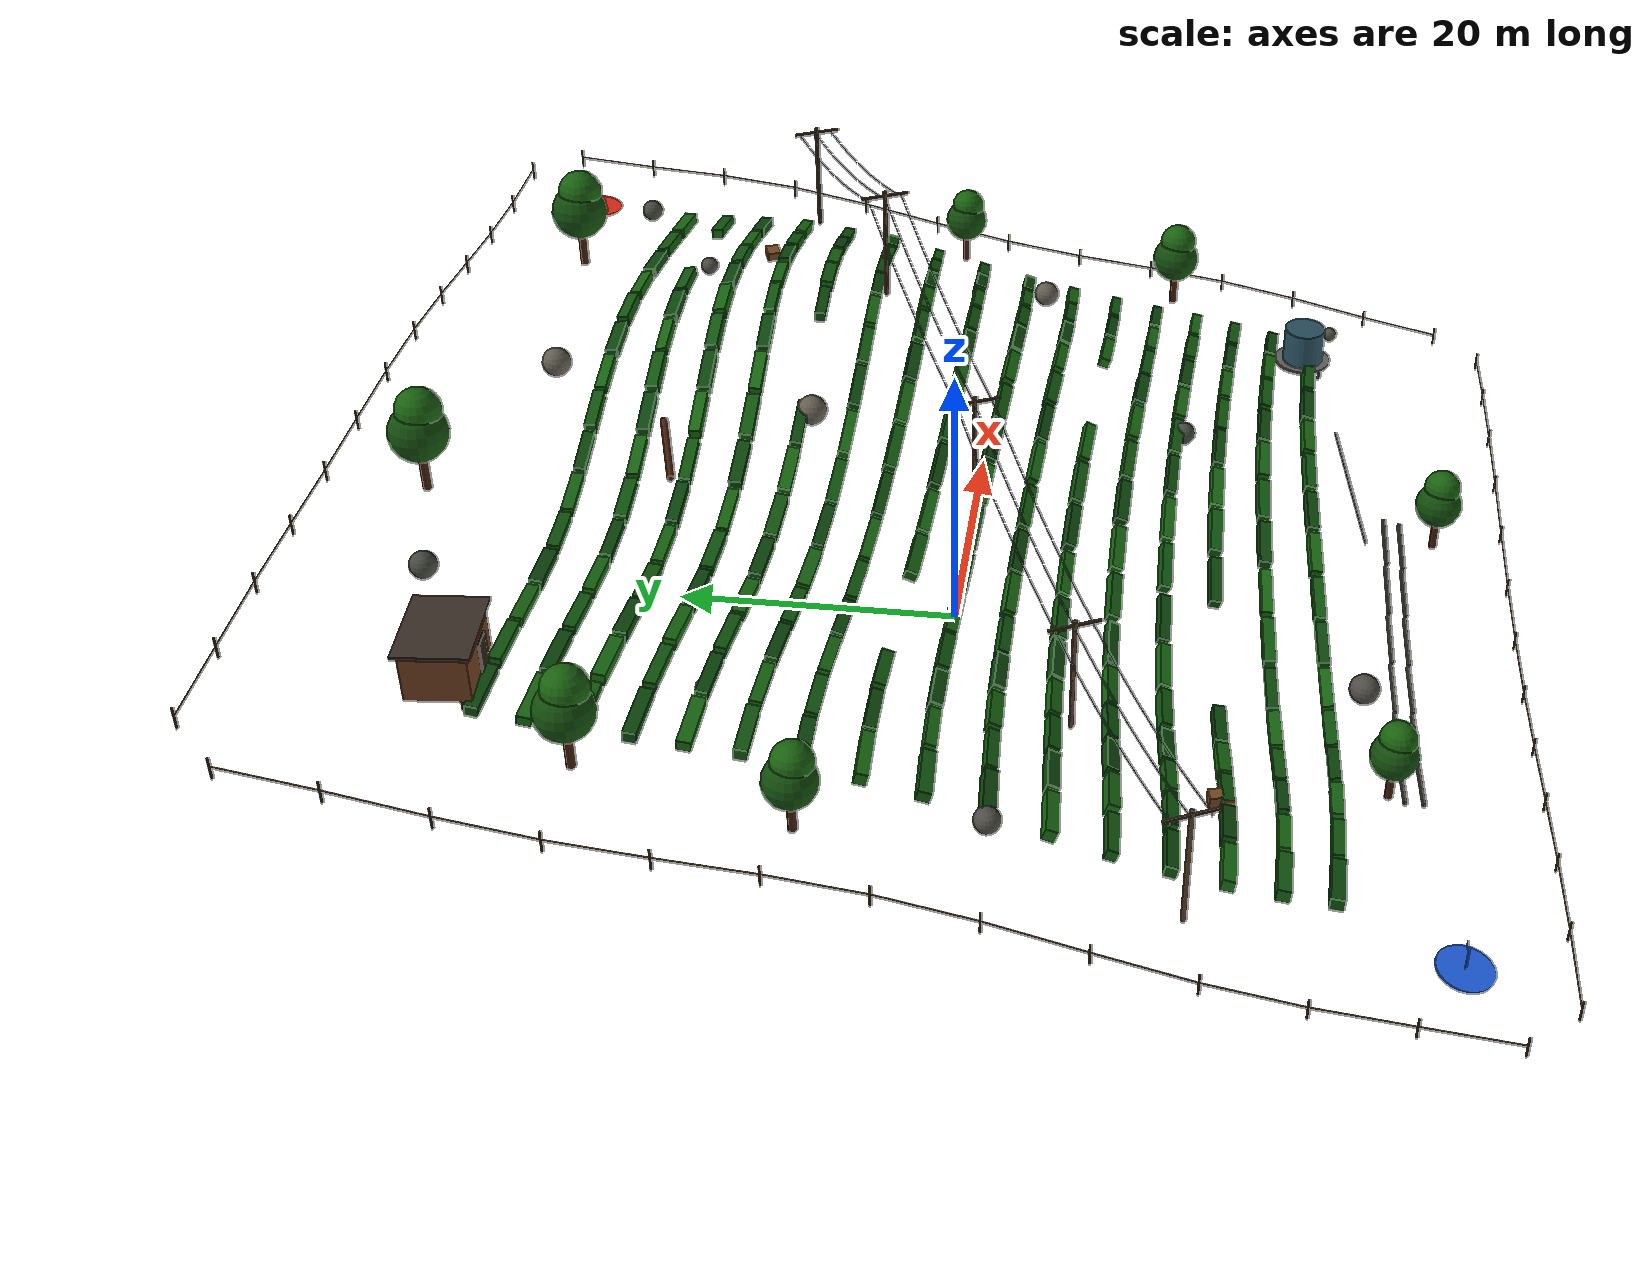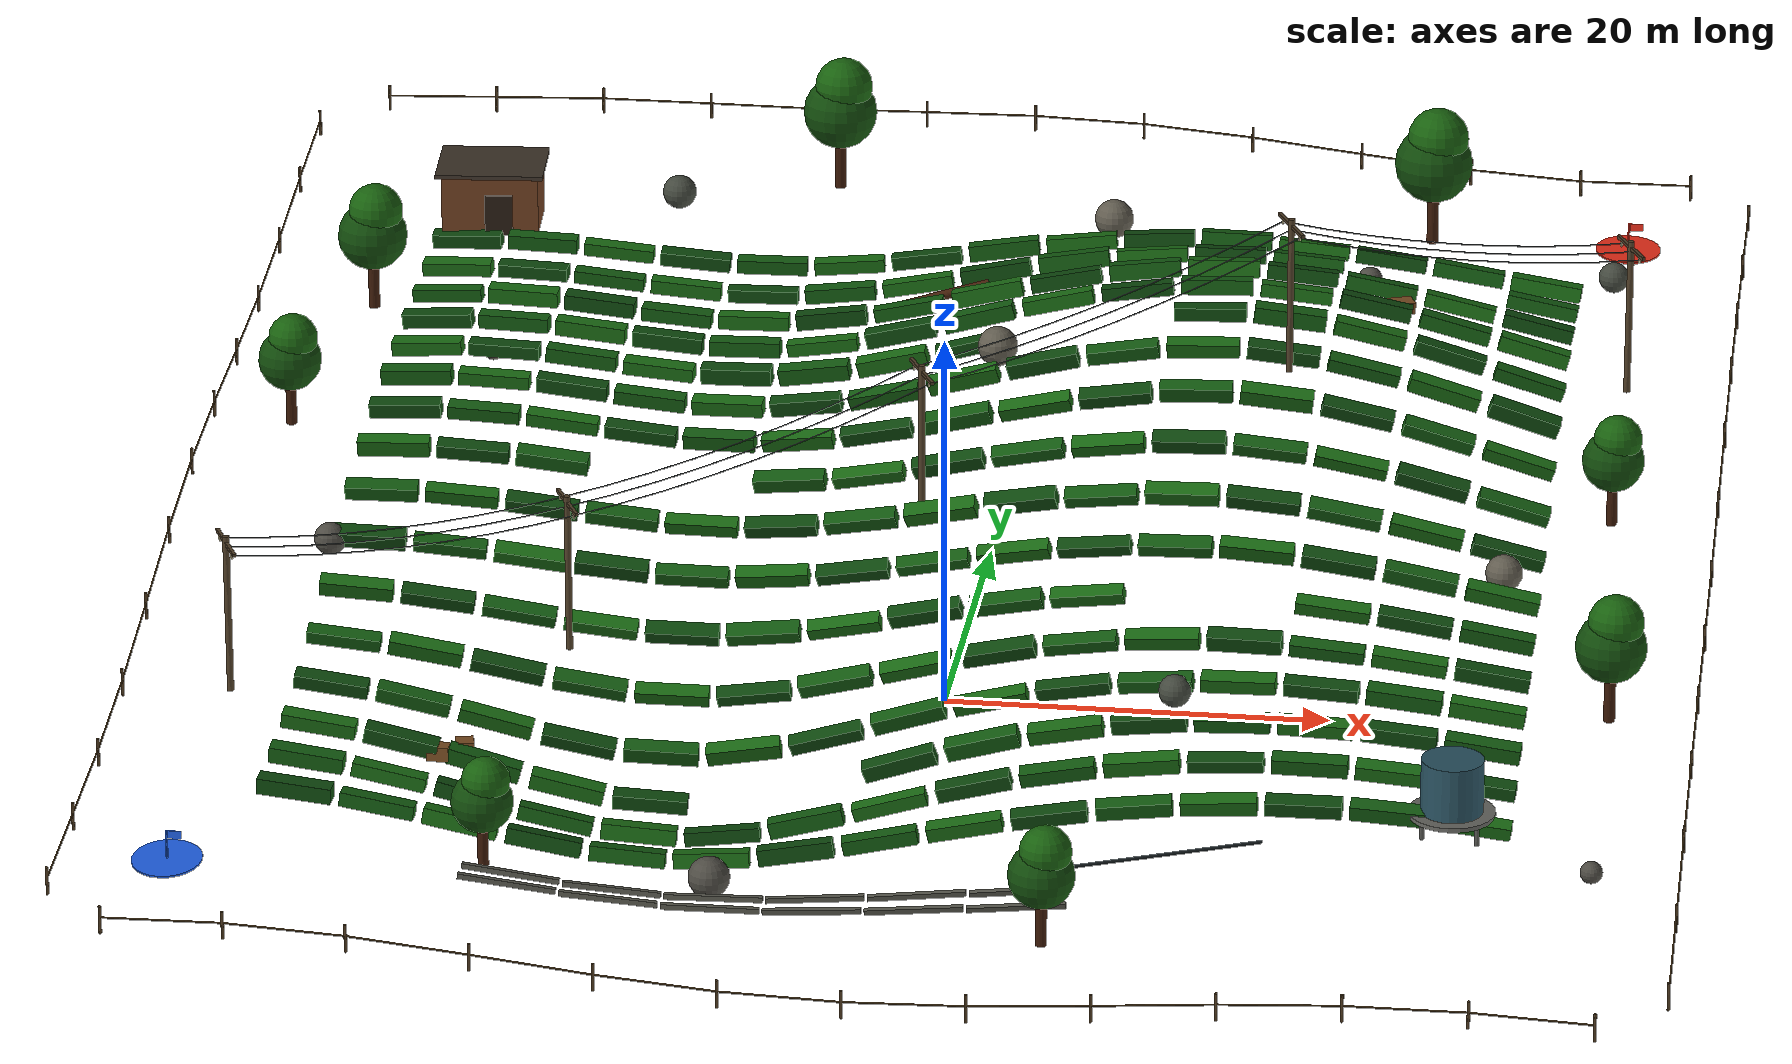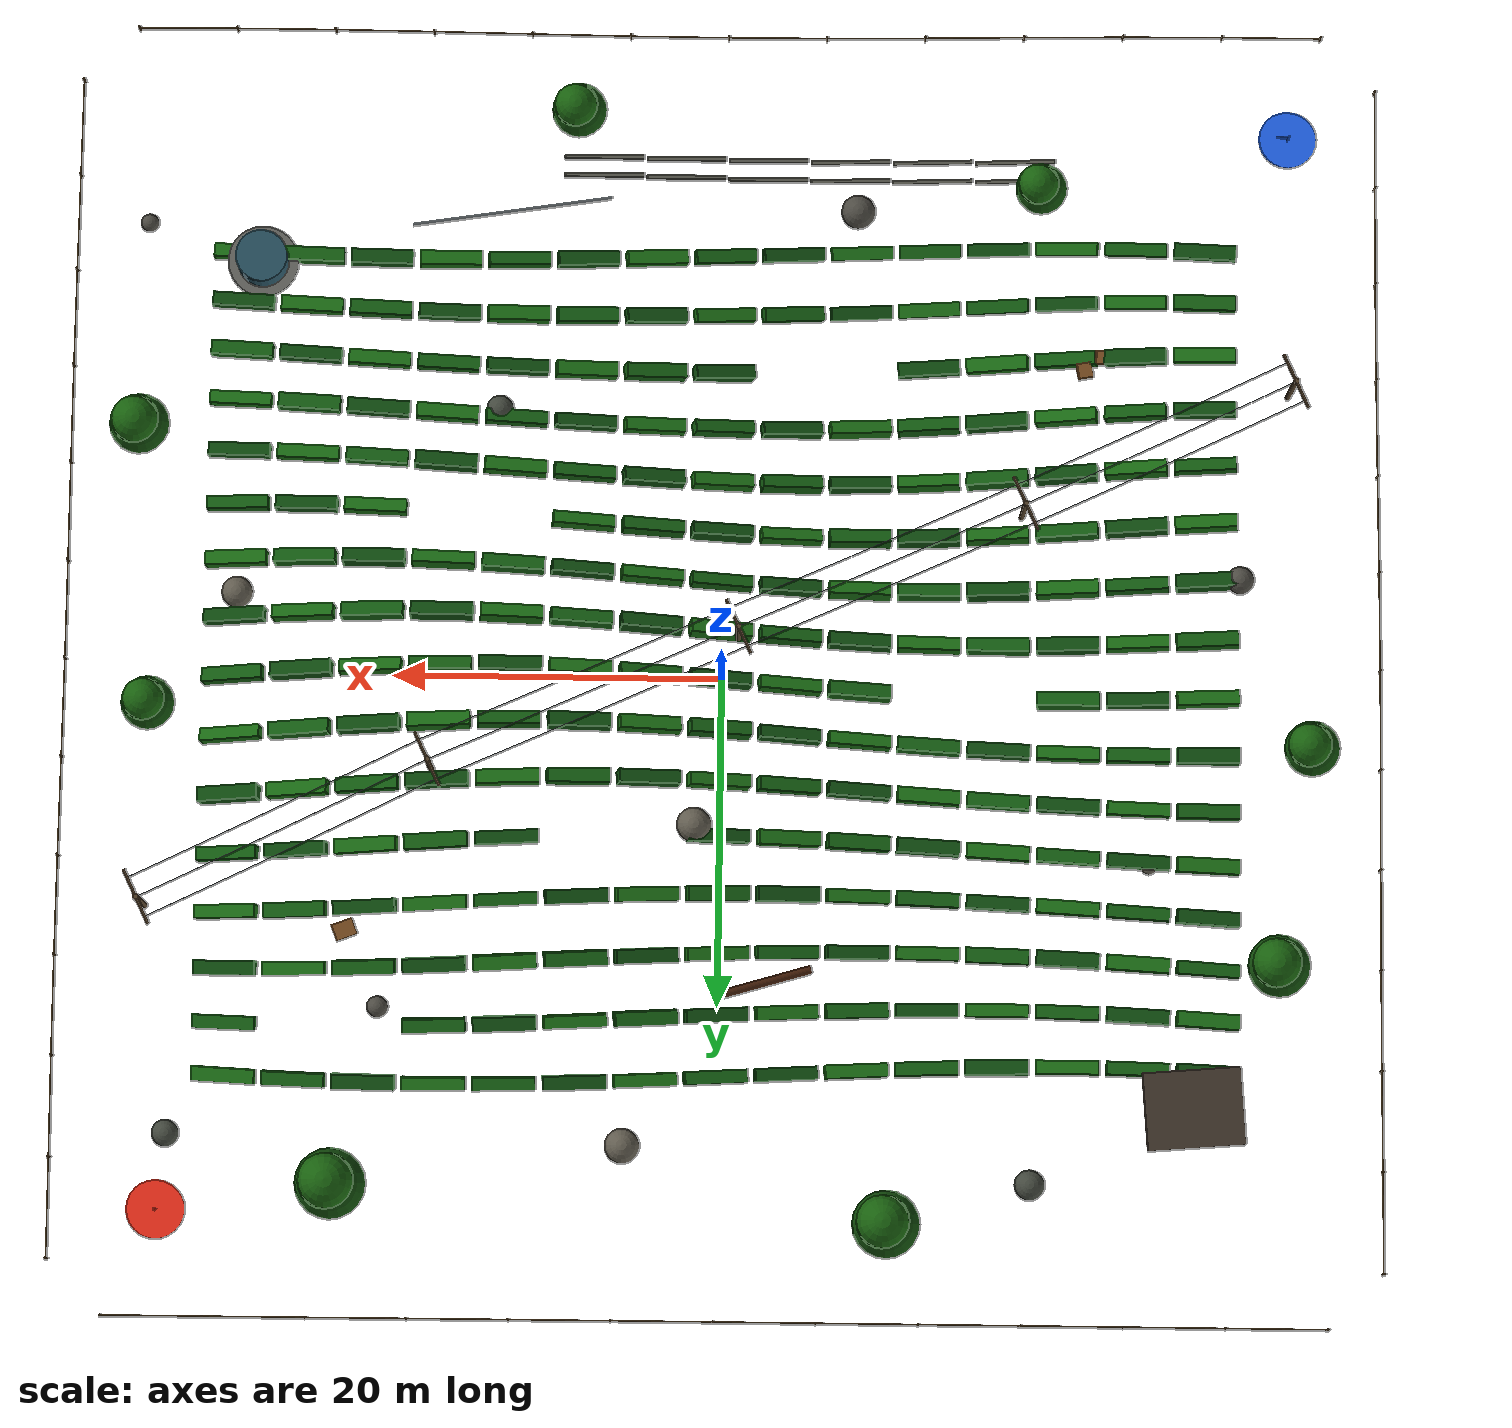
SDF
<sdf version="1.6">
 <world name="mountain_tea_garden_80m">
  <gravity>0 0 -9.81</gravity>
  <magnetic_field>6e-06 2.3e-05 -4.2e-05</magnetic_field>
  <physics name="ode_physics" type="ode">
   <max_step_size>0.002</max_step_size>
   <real_time_factor>1.0</real_time_factor>
   <real_time_update_rate>500</real_time_update_rate>
   <ode><solver><type>quick</type><iters>35</iters></solver></ode>
  </physics>
  <scene>
   <ambient>0.48 0.50 0.45 1</ambient>
   <background>0.64 0.76 0.87 1</background>
   <shadows>true</shadows>
   <grid>false</grid>
  </scene>
  <light name="sun" type="directional">
   <pose>0 0 80 0 0 0</pose>
   <diffuse>0.95 0.91 0.80 1</diffuse>
   <specular>0.25 0.25 0.22 1</specular>
   <direction>-0.42 0.25 -0.87</direction>
  </light>
  <model name="tea_row_00">
   <static>true</static>
   <link name="bush_00">
    <pose>-29 -25.9183 5.09071 0.064143 0.0842919 -0.0509171</pose>
    <collision name="collision">
     <geometry><box><size>3.75 0.893624 0.839996</size></box></geometry>
     <laser_retro>55</laser_retro>
     <surface><friction><ode><mu>1.15</mu><mu2>1.15</mu2></ode></friction></surface>
    </collision>
    <visual name="visual">
     <geometry><box><size>3.75 0.893624 0.839996</size></box></geometry>
     <material>
      <ambient>0.055 0.29 0.055 1</ambient>
      <diffuse>0.055 0.29 0.055 1</diffuse>
      <specular>0.05 0.05 0.05 1</specular>
     </material>
    </visual>
   </link>
   <link name="bush_01">
    <pose>-24.85 -26.0982 4.55602 0.0157015 0.149454 -0.0348228</pose>
    <collision name="collision">
     <geometry><box><size>3.75 0.78362 0.750846</size></box></geometry>
     <laser_retro>55</laser_retro>
     <surface><friction><ode><mu>1.15</mu><mu2>1.15</mu2></ode></friction></surface>
    </collision>
    <visual name="visual">
     <geometry><box><size>3.75 0.78362 0.750846</size></box></geometry>
     <material>
      <ambient>0.075 0.36 0.065 1</ambient>
      <diffuse>0.075 0.36 0.065 1</diffuse>
      <specular>0.05 0.05 0.05 1</specular>
     </material>
    </visual>
   </link>
   <link name="bush_02">
    <pose>-20.7 -26.2012 3.8757 -0.0466893 0.190635 -0.0142239</pose>
    <collision name="collision">
     <geometry><box><size>3.75 0.815882 0.846742</size></box></geometry>
     <laser_retro>55</laser_retro>
     <surface><friction><ode><mu>1.15</mu><mu2>1.15</mu2></ode></friction></surface>
    </collision>
    <visual name="visual">
     <geometry><box><size>3.75 0.815882 0.846742</size></box></geometry>
     <material>
      <ambient>0.1 0.42 0.075 1</ambient>
      <diffuse>0.1 0.42 0.075 1</diffuse>
      <specular>0.05 0.05 0.05 1</specular>
     </material>
    </visual>
   </link>
   <link name="bush_03">
    <pose>-16.55 -26.2138 3.07548 -0.106985 0.171181 0.00821945</pose>
    <collision name="collision">
     <geometry><box><size>3.75 0.784117 0.818555</size></box></geometry>
     <laser_retro>55</laser_retro>
     <surface><friction><ode><mu>1.15</mu><mu2>1.15</mu2></ode></friction></surface>
    </collision>
    <visual name="visual">
     <geometry><box><size>3.75 0.784117 0.818555</size></box></geometry>
     <material>
      <ambient>0.055 0.29 0.055 1</ambient>
      <diffuse>0.055 0.29 0.055 1</diffuse>
      <specular>0.05 0.05 0.05 1</specular>
     </material>
    </visual>
   </link>
   <link name="bush_04">
    <pose>-12.4 -26.1344 2.50865 -0.135952 0.076252 0.0295966</pose>
    <collision name="collision">
     <geometry><box><size>3.75 0.842907 0.766013</size></box></geometry>
     <laser_retro>55</laser_retro>
     <surface><friction><ode><mu>1.15</mu><mu2>1.15</mu2></ode></friction></surface>
    </collision>
    <visual name="visual">
     <geometry><box><size>3.75 0.842907 0.766013</size></box></geometry>
     <material>
      <ambient>0.075 0.36 0.065 1</ambient>
      <diffuse>0.075 0.36 0.065 1</diffuse>
      <specular>0.05 0.05 0.05 1</specular>
     </material>
    </visual>
   </link>
   <link name="bush_05">
    <pose>-8.25 -25.9733 2.48361 -0.110948 -0.0585681 0.0471422</pose>
    <collision name="collision">
     <geometry><box><size>3.75 0.809823 0.793594</size></box></geometry>
     <laser_retro>55</laser_retro>
     <surface><friction><ode><mu>1.15</mu><mu2>1.15</mu2></ode></friction></surface>
    </collision>
    <visual name="visual">
     <geometry><box><size>3.75 0.809823 0.793594</size></box></geometry>
     <material>
      <ambient>0.1 0.42 0.075 1</ambient>
      <diffuse>0.1 0.42 0.075 1</diffuse>
      <specular>0.05 0.05 0.05 1</specular>
     </material>
    </visual>
   </link>
   <link name="bush_06">
    <pose>-4.1 -25.7513 3.00051 -0.0351008 -0.164965 0.0586045</pose>
    <collision name="collision">
     <geometry><box><size>3.75 0.794615 0.853127</size></box></geometry>
     <laser_retro>55</laser_retro>
     <surface><friction><ode><mu>1.15</mu><mu2>1.15</mu2></ode></friction></surface>
    </collision>
    <visual name="visual">
     <geometry><box><size>3.75 0.794615 0.853127</size></box></geometry>
     <material>
      <ambient>0.055 0.29 0.055 1</ambient>
      <diffuse>0.055 0.29 0.055 1</diffuse>
      <specular>0.05 0.05 0.05 1</specular>
     </material>
    </visual>
   </link>
   <link name="bush_07">
    <pose>0.05 -25.4969 3.75717 0.0616149 -0.205876 0.0625265</pose>
    <collision name="collision">
     <geometry><box><size>3.75 0.810346 0.758996</size></box></geometry>
     <laser_retro>55</laser_retro>
     <surface><friction><ode><mu>1.15</mu><mu2>1.15</mu2></ode></friction></surface>
    </collision>
    <visual name="visual">
     <geometry><box><size>3.75 0.810346 0.758996</size></box></geometry>
     <material>
      <ambient>0.075 0.36 0.065 1</ambient>
      <diffuse>0.075 0.36 0.065 1</diffuse>
      <specular>0.05 0.05 0.05 1</specular>
     </material>
    </visual>
   </link>
   <link name="bush_08">
    <pose>4.2 -25.2429 4.60635 0.145028 -0.193895 0.0584129</pose>
    <collision name="collision">
     <geometry><box><size>3.75 0.858912 0.745281</size></box></geometry>
     <laser_retro>55</laser_retro>
     <surface><friction><ode><mu>1.15</mu><mu2>1.15</mu2></ode></friction></surface>
    </collision>
    <visual name="visual">
     <geometry><box><size>3.75 0.858912 0.745281</size></box></geometry>
     <material>
      <ambient>0.1 0.42 0.075 1</ambient>
      <diffuse>0.1 0.42 0.075 1</diffuse>
      <specular>0.05 0.05 0.05 1</specular>
     </material>
    </visual>
   </link>
   <link name="bush_09">
    <pose>8.35 -25.022 5.35109 0.200214 -0.15775 0.0467833</pose>
    <collision name="collision">
     <geometry><box><size>3.75 0.857217 0.748906</size></box></geometry>
     <laser_retro>55</laser_retro>
     <surface><friction><ode><mu>1.15</mu><mu2>1.15</mu2></ode></friction></surface>
    </collision>
    <visual name="visual">
     <geometry><box><size>3.75 0.857217 0.748906</size></box></geometry>
     <material>
      <ambient>0.055 0.29 0.055 1</ambient>
      <diffuse>0.055 0.29 0.055 1</diffuse>
      <specular>0.05 0.05 0.05 1</specular>
     </material>
    </visual>
   </link>
   <link name="bush_10">
    <pose>12.5 -24.8626 5.94348 0.230316 -0.113711 0.0291162</pose>
    <collision name="collision">
     <geometry><box><size>3.75 0.815023 0.795412</size></box></geometry>
     <laser_retro>55</laser_retro>
     <surface><friction><ode><mu>1.15</mu><mu2>1.15</mu2></ode></friction></surface>
    </collision>
    <visual name="visual">
     <geometry><box><size>3.75 0.815023 0.795412</size></box></geometry>
     <material>
      <ambient>0.075 0.36 0.065 1</ambient>
      <diffuse>0.075 0.36 0.065 1</diffuse>
      <specular>0.05 0.05 0.05 1</specular>
     </material>
    </visual>
   </link>
   <link name="bush_11">
    <pose>16.65 -24.7854 6.30987 0.243292 -0.0642154 0.00767947</pose>
    <collision name="collision">
     <geometry><box><size>3.75 0.875957 0.783506</size></box></geometry>
     <laser_retro>55</laser_retro>
     <surface><friction><ode><mu>1.15</mu><mu2>1.15</mu2></ode></friction></surface>
    </collision>
    <visual name="visual">
     <geometry><box><size>3.75 0.875957 0.783506</size></box></geometry>
     <material>
      <ambient>0.1 0.42 0.075 1</ambient>
      <diffuse>0.1 0.42 0.075 1</diffuse>
      <specular>0.05 0.05 0.05 1</specular>
     </material>
    </visual>
   </link>
   <link name="bush_12">
    <pose>20.8 -24.8003 6.46263 0.245203 -0.00990483 -0.0147534</pose>
    <collision name="collision">
     <geometry><box><size>3.75 0.882197 0.779015</size></box></geometry>
     <laser_retro>55</laser_retro>
     <surface><friction><ode><mu>1.15</mu><mu2>1.15</mu2></ode></friction></surface>
    </collision>
    <visual name="visual">
     <geometry><box><size>3.75 0.882197 0.779015</size></box></geometry>
     <material>
      <ambient>0.055 0.29 0.055 1</ambient>
      <diffuse>0.055 0.29 0.055 1</diffuse>
      <specular>0.05 0.05 0.05 1</specular>
     </material>
    </visual>
   </link>
   <link name="bush_13">
    <pose>24.95 -24.9053 6.39905 0.240569 0.0442958 -0.0352733</pose>
    <collision name="collision">
     <geometry><box><size>3.75 0.852411 0.797258</size></box></geometry>
     <laser_retro>55</laser_retro>
     <surface><friction><ode><mu>1.15</mu><mu2>1.15</mu2></ode></friction></surface>
    </collision>
    <visual name="visual">
     <geometry><box><size>3.75 0.852411 0.797258</size></box></geometry>
     <material>
      <ambient>0.075 0.36 0.065 1</ambient>
      <diffuse>0.075 0.36 0.065 1</diffuse>
      <specular>0.05 0.05 0.05 1</specular>
     </material>
    </visual>
   </link>
   <link name="bush_14">
    <pose>29.1 -25.0869 6.06942 0.233761 0.0910172 -0.0512307</pose>
    <collision name="collision">
     <geometry><box><size>3.75 0.808615 0.708817</size></box></geometry>
     <laser_retro>55</laser_retro>
     <surface><friction><ode><mu>1.15</mu><mu2>1.15</mu2></ode></friction></surface>
    </collision>
    <visual name="visual">
     <geometry><box><size>3.75 0.808615 0.708817</size></box></geometry>
     <material>
      <ambient>0.1 0.42 0.075 1</ambient>
      <diffuse>0.1 0.42 0.075 1</diffuse>
      <specular>0.05 0.05 0.05 1</specular>
     </material>
    </visual>
   </link>
  </model>
  <model name="tea_row_01">
   <static>true</static>
   <link name="bush_00">
    <pose>-29 -22.7745 5.35266 0.0998876 0.112143 -0.0311501</pose>
    <collision name="collision">
     <geometry><box><size>3.75 0.892285 0.839958</size></box></geometry>
     <laser_retro>55</laser_retro>
     <surface><friction><ode><mu>1.15</mu><mu2>1.15</mu2></ode></friction></surface>
    </collision>
    <visual name="visual">
     <geometry><box><size>3.75 0.892285 0.839958</size></box></geometry>
     <material>
      <ambient>0.075 0.36 0.065 1</ambient>
      <diffuse>0.075 0.36 0.065 1</diffuse>
      <specular>0.05 0.05 0.05 1</specular>
     </material>
    </visual>
   </link>
   <link name="bush_01">
    <pose>-24.85 -22.8608 4.67236 0.0571815 0.191919 -0.0099789</pose>
    <collision name="collision">
     <geometry><box><size>3.75 0.796132 0.753947</size></box></geometry>
     <laser_retro>55</laser_retro>
     <surface><friction><ode><mu>1.15</mu><mu2>1.15</mu2></ode></friction></surface>
    </collision>
    <visual name="visual">
     <geometry><box><size>3.75 0.796132 0.753947</size></box></geometry>
     <material>
      <ambient>0.1 0.42 0.075 1</ambient>
      <diffuse>0.1 0.42 0.075 1</diffuse>
      <specular>0.05 0.05 0.05 1</specular>
     </material>
    </visual>
   </link>
   <link name="bush_02">
    <pose>-20.7 -22.8555 3.7644 0.00466127 0.243966 0.0124866</pose>
    <collision name="collision">
     <geometry><box><size>3.75 0.777143 0.81683</size></box></geometry>
     <laser_retro>55</laser_retro>
     <surface><friction><ode><mu>1.15</mu><mu2>1.15</mu2></ode></friction></surface>
    </collision>
    <visual name="visual">
     <geometry><box><size>3.75 0.777143 0.81683</size></box></geometry>
     <material>
      <ambient>0.055 0.29 0.055 1</ambient>
      <diffuse>0.055 0.29 0.055 1</diffuse>
      <specular>0.05 0.05 0.05 1</specular>
     </material>
    </visual>
   </link>
   <link name="bush_03">
    <pose>-16.55 -22.7594 2.7265 -0.0450919 0.214428 0.0333328</pose>
    <collision name="collision">
     <geometry><box><size>3.75 0.809624 0.754473</size></box></geometry>
     <laser_retro>55</laser_retro>
     <surface><friction><ode><mu>1.15</mu><mu2>1.15</mu2></ode></friction></surface>
    </collision>
    <visual name="visual">
     <geometry><box><size>3.75 0.809624 0.754473</size></box></geometry>
     <material>
      <ambient>0.075 0.36 0.065 1</ambient>
      <diffuse>0.075 0.36 0.065 1</diffuse>
      <specular>0.05 0.05 0.05 1</specular>
     </material>
    </visual>
   </link>
   <link name="bush_04">
    <pose>-12.4 -22.5847 2.11446 -0.0687549 0.0786142 0.0498662</pose>
    <collision name="collision">
     <geometry><box><size>3.75 0.85426 0.826937</size></box></geometry>
     <laser_retro>55</laser_retro>
     <surface><friction><ode><mu>1.15</mu><mu2>1.15</mu2></ode></friction></surface>
    </collision>
    <visual name="visual">
     <geometry><box><size>3.75 0.85426 0.826937</size></box></geometry>
     <material>
      <ambient>0.1 0.42 0.075 1</ambient>
      <diffuse>0.1 0.42 0.075 1</diffuse>
      <specular>0.05 0.05 0.05 1</specular>
     </material>
    </visual>
   </link>
   <link name="bush_05">
    <pose>-8.25 -22.3541 2.12251 -0.0481005 -0.109021 0.0599689</pose>
    <collision name="collision">
     <geometry><box><size>3.75 0.811713 0.714429</size></box></geometry>
     <laser_retro>55</laser_retro>
     <surface><friction><ode><mu>1.15</mu><mu2>1.15</mu2></ode></friction></surface>
    </collision>
    <visual name="visual">
     <geometry><box><size>3.75 0.811713 0.714429</size></box></geometry>
     <material>
      <ambient>0.055 0.29 0.055 1</ambient>
      <diffuse>0.055 0.29 0.055 1</diffuse>
      <specular>0.05 0.05 0.05 1</specular>
     </material>
    </visual>
   </link>
   <link name="bush_06">
    <pose>-4.1 -22.0971 2.97162 0.0134282 -0.24275 0.0623588</pose>
    <collision name="collision">
     <geometry><box><size>3.75 0.858335 0.864843</size></box></geometry>
     <laser_retro>55</laser_retro>
     <surface><friction><ode><mu>1.15</mu><mu2>1.15</mu2></ode></friction></surface>
    </collision>
    <visual name="visual">
     <geometry><box><size>3.75 0.858335 0.864843</size></box></geometry>
     <material>
      <ambient>0.075 0.36 0.065 1</ambient>
      <diffuse>0.075 0.36 0.065 1</diffuse>
      <specular>0.05 0.05 0.05 1</specular>
     </material>
    </visual>
   </link>
   <link name="bush_07">
    <pose>0.05 -21.847 4.03932 0.0907372 -0.277757 0.0567342</pose>
    <collision name="collision">
     <geometry><box><size>3.75 0.803899 0.716737</size></box></geometry>
     <laser_retro>55</laser_retro>
     <surface><friction><ode><mu>1.15</mu><mu2>1.15</mu2></ode></friction></surface>
    </collision>
    <visual name="visual">
     <geometry><box><size>3.75 0.803899 0.716737</size></box></geometry>
     <material>
      <ambient>0.1 0.42 0.075 1</ambient>
      <diffuse>0.1 0.42 0.075 1</diffuse>
      <specular>0.05 0.05 0.05 1</specular>
     </material>
    </visual>
   </link>
   <link name="bush_08">
    <pose>4.2 -21.6359 5.20035 0.156833 -0.242595 0.0438062</pose>
    <collision name="collision">
     <geometry><box><size>3.75 0.875835 0.791925</size></box></geometry>
     <laser_retro>55</laser_retro>
     <surface><friction><ode><mu>1.15</mu><mu2>1.15</mu2></ode></friction></surface>
    </collision>
    <visual name="visual">
     <geometry><box><size>3.75 0.875835 0.791925</size></box></geometry>
     <material>
      <ambient>0.055 0.29 0.055 1</ambient>
      <diffuse>0.055 0.29 0.055 1</diffuse>
      <specular>0.05 0.05 0.05 1</specular>
     </material>
    </visual>
   </link>
   <link name="bush_09">
    <pose>8.35 -21.491 6.08629 0.200133 -0.182117 0.0252212</pose>
    <collision name="collision">
     <geometry><box><size>3.75 0.874606 0.766644</size></box></geometry>
     <laser_retro>55</laser_retro>
     <surface><friction><ode><mu>1.15</mu><mu2>1.15</mu2></ode></friction></surface>
    </collision>
    <visual name="visual">
     <geometry><box><size>3.75 0.874606 0.766644</size></box></geometry>
     <material>
      <ambient>0.075 0.36 0.065 1</ambient>
      <diffuse>0.075 0.36 0.065 1</diffuse>
      <specular>0.05 0.05 0.05 1</specular>
     </material>
    </visual>
   </link>
   <link name="bush_10">
    <pose>12.5 -21.431 6.74696 0.222287 -0.120367 0.0033692</pose>
    <collision name="collision">
     <geometry><box><size>3.75 0.887658 0.824218</size></box></geometry>
     <laser_retro>55</laser_retro>
     <surface><friction><ode><mu>1.15</mu><mu2>1.15</mu2></ode></friction></surface>
    </collision>
    <visual name="visual">
     <geometry><box><size>3.75 0.887658 0.824218</size></box></geometry>
     <material>
      <ambient>0.1 0.42 0.075 1</ambient>
      <diffuse>0.1 0.42 0.075 1</diffuse>
      <specular>0.05 0.05 0.05 1</specular>
     </material>
    </visual>
   </link>
   <link name="bush_11">
    <pose>16.65 -21.4637 7.06535 0.228687 -0.0604508 -0.0189199</pose>
    <collision name="collision">
     <geometry><box><size>3.75 0.844396 0.708908</size></box></geometry>
     <laser_retro>55</laser_retro>
     <surface><friction><ode><mu>1.15</mu><mu2>1.15</mu2></ode></friction></surface>
    </collision>
    <visual name="visual">
     <geometry><box><size>3.75 0.844396 0.708908</size></box></geometry>
     <material>
      <ambient>0.055 0.29 0.055 1</ambient>
      <diffuse>0.055 0.29 0.055 1</diffuse>
      <specular>0.05 0.05 0.05 1</specular>
     </material>
    </visual>
   </link>
   <link name="bush_12">
    <pose>20.8 -21.5847 7.25009 0.224577 -0.0016592 -0.0387565</pose>
    <collision name="collision">
     <geometry><box><size>3.75 0.856695 0.821859</size></box></geometry>
     <laser_retro>55</laser_retro>
     <surface><friction><ode><mu>1.15</mu><mu2>1.15</mu2></ode></friction></surface>
    </collision>
    <visual name="visual">
     <geometry><box><size>3.75 0.856695 0.821859</size></box></geometry>
     <material>
      <ambient>0.075 0.36 0.065 1</ambient>
      <diffuse>0.075 0.36 0.065 1</diffuse>
      <specular>0.05 0.05 0.05 1</specular>
     </material>
    </visual>
   </link>
   <link name="bush_13">
    <pose>24.95 -21.7786 7.10898 0.215438 0.0523958 -0.0535833</pose>
    <collision name="collision">
     <geometry><box><size>3.75 0.867778 0.755871</size></box></geometry>
     <laser_retro>55</laser_retro>
     <surface><friction><ode><mu>1.15</mu><mu2>1.15</mu2></ode></friction></surface>
    </collision>
    <visual name="visual">
     <geometry><box><size>3.75 0.867778 0.755871</size></box></geometry>
     <material>
      <ambient>0.1 0.42 0.075 1</ambient>
      <diffuse>0.1 0.42 0.075 1</diffuse>
      <specular>0.05 0.05 0.05 1</specular>
     </material>
    </visual>
   </link>
   <link name="bush_14">
    <pose>29.1 -22.0203 6.7879 0.20699 0.09578 -0.0615065</pose>
    <collision name="collision">
     <geometry><box><size>3.75 0.815724 0.740358</size></box></geometry>
     <laser_retro>55</laser_retro>
     <surface><friction><ode><mu>1.15</mu><mu2>1.15</mu2></ode></friction></surface>
    </collision>
    <visual name="visual">
     <geometry><box><size>3.75 0.815724 0.740358</size></box></geometry>
     <material>
      <ambient>0.055 0.29 0.055 1</ambient>
      <diffuse>0.055 0.29 0.055 1</diffuse>
      <specular>0.05 0.05 0.05 1</specular>
     </material>
    </visual>
   </link>
  </model>
  <model name="tea_row_02">
   <static>true</static>
   <link name="bush_00">
    <pose>-29 -19.517 5.76072 0.166529 0.131564 -0.0056859</pose>
    <collision name="collision">
     <geometry><box><size>3.75 0.844071 0.77999</size></box></geometry>
     <laser_retro>55</laser_retro>
     <surface><friction><ode><mu>1.15</mu><mu2>1.15</mu2></ode></friction></surface>
    </collision>
    <visual name="visual">
     <geometry><box><size>3.75 0.844071 0.77999</size></box></geometry>
     <material>
      <ambient>0.1 0.42 0.075 1</ambient>
      <diffuse>0.1 0.42 0.075 1</diffuse>
      <specular>0.05 0.05 0.05 1</specular>
     </material>
    </visual>
   </link>
   <link name="bush_01">
    <pose>-24.85 -19.4939 5.05984 0.152144 0.218358 0.0166937</pose>
    <collision name="collision">
     <geometry><box><size>3.75 0.892737 0.848082</size></box></geometry>
     <laser_retro>55</laser_retro>
     <surface><friction><ode><mu>1.15</mu><mu2>1.15</mu2></ode></friction></surface>
    </collision>
    <visual name="visual">
     <geometry><box><size>3.75 0.892737 0.848082</size></box></geometry>
     <material>
      <ambient>0.055 0.29 0.055 1</ambient>
      <diffuse>0.055 0.29 0.055 1</diffuse>
      <specular>0.05 0.05 0.05 1</specular>
     </material>
    </visual>
   </link>
   <link name="bush_02">
    <pose>-20.7 -19.3814 4.00924 0.142589 0.272644 0.0369091</pose>
    <collision name="collision">
     <geometry><box><size>3.75 0.821232 0.87619</size></box></geometry>
     <laser_retro>55</laser_retro>
     <surface><friction><ode><mu>1.15</mu><mu2>1.15</mu2></ode></friction></surface>
    </collision>
    <visual name="visual">
     <geometry><box><size>3.75 0.821232 0.87619</size></box></geometry>
     <material>
      <ambient>0.075 0.36 0.065 1</ambient>
      <diffuse>0.075 0.36 0.065 1</diffuse>
      <specular>0.05 0.05 0.05 1</specular>
     </material>
    </visual>
   </link>
   <link name="bush_03">
    <pose>-16.55 -19.1941 2.8697 0.139592 0.230904 0.0523518</pose>
    <collision name="collision">
     <geometry><box><size>3.75 0.890309 0.825091</size></box></geometry>
     <laser_retro>55</laser_retro>
     <surface><friction><ode><mu>1.15</mu><mu2>1.15</mu2></ode></friction></surface>
    </collision>
    <visual name="visual">
     <geometry><box><size>3.75 0.890309 0.825091</size></box></geometry>
     <material>
      <ambient>0.1 0.42 0.075 1</ambient>
      <diffuse>0.1 0.42 0.075 1</diffuse>
      <specular>0.05 0.05 0.05 1</specular>
     </material>
    </visual>
   </link>
   <link name="bush_04">
    <pose>-12.4 -18.9559 2.18218 0.144236 0.0670802 0.0610474</pose>
    <collision name="collision">
     <geometry><box><size>3.75 0.864545 0.777394</size></box></geometry>
     <laser_retro>55</laser_retro>
     <surface><friction><ode><mu>1.15</mu><mu2>1.15</mu2></ode></friction></surface>
    </collision>
    <visual name="visual">
     <geometry><box><size>3.75 0.864545 0.777394</size></box></geometry>
     <material>
      <ambient>0.055 0.29 0.055 1</ambient>
      <diffuse>0.055 0.29 0.055 1</diffuse>
      <specular>0.05 0.05 0.05 1</specular>
     </material>
    </visual>
   </link>
   <link name="bush_07">
    <pose>0.05 -18.2523 4.67501 0.200604 -0.312663 0.0406192</pose>
    <collision name="collision">
     <geometry><box><size>3.75 0.825149 0.859023</size></box></geometry>
     <laser_retro>55</laser_retro>
     <surface><friction><ode><mu>1.15</mu><mu2>1.15</mu2></ode></friction></surface>
    </collision>
    <visual name="visual">
     <geometry><box><size>3.75 0.825149 0.859023</size></box></geometry>
     <material>
      <ambient>0.055 0.29 0.055 1</ambient>
      <diffuse>0.055 0.29 0.055 1</diffuse>
      <specular>0.05 0.05 0.05 1</specular>
     </material>
    </visual>
   </link>
   <link name="bush_08">
    <pose>4.2 -18.1226 5.9424 0.222367 -0.264168 0.021205</pose>
    <collision name="collision">
     <geometry><box><size>3.75 0.879029 0.89364</size></box></geometry>
     <laser_retro>55</laser_retro>
     <surface><friction><ode><mu>1.15</mu><mu2>1.15</mu2></ode></friction></surface>
    </collision>
    <visual name="visual">
     <geometry><box><size>3.75 0.879029 0.89364</size></box></geometry>
     <material>
      <ambient>0.075 0.36 0.065 1</ambient>
      <diffuse>0.075 0.36 0.065 1</diffuse>
      <specular>0.05 0.05 0.05 1</specular>
     </material>
    </visual>
   </link>
   <link name="bush_09">
    <pose>8.35 -18.0801 6.84735 0.237251 -0.190544 -0.000957289</pose>
    <collision name="collision">
     <geometry><box><size>3.75 0.891353 0.777394</size></box></geometry>
     <laser_retro>55</laser_retro>
     <surface><friction><ode><mu>1.15</mu><mu2>1.15</mu2></ode></friction></surface>
    </collision>
    <visual name="visual">
     <geometry><box><size>3.75 0.891353 0.777394</size></box></geometry>
     <material>
      <ambient>0.1 0.42 0.075 1</ambient>
      <diffuse>0.1 0.42 0.075 1</diffuse>
      <specular>0.05 0.05 0.05 1</specular>
     </material>
    </visual>
   </link>
   <link name="bush_10">
    <pose>12.5 -18.1303 7.53505 0.241708 -0.118024 -0.0229954</pose>
    <collision name="collision">
     <geometry><box><size>3.75 0.776358 0.865297</size></box></geometry>
     <laser_retro>55</laser_retro>
     <surface><friction><ode><mu>1.15</mu><mu2>1.15</mu2></ode></friction></surface>
    </collision>
    <visual name="visual">
     <geometry><box><size>3.75 0.776358 0.865297</size></box></geometry>
     <material>
      <ambient>0.055 0.29 0.055 1</ambient>
      <diffuse>0.055 0.29 0.055 1</diffuse>
      <specular>0.05 0.05 0.05 1</specular>
     </material>
    </visual>
   </link>
   <link name="bush_11">
    <pose>16.65 -18.2669 7.81369 0.234671 -0.0510924 -0.042054</pose>
    <collision name="collision">
     <geometry><box><size>3.75 0.827249 0.722065</size></box></geometry>
     <laser_retro>55</laser_retro>
     <surface><friction><ode><mu>1.15</mu><mu2>1.15</mu2></ode></friction></surface>
    </collision>
    <visual name="visual">
     <geometry><box><size>3.75 0.827249 0.722065</size></box></geometry>
     <material>
      <ambient>0.075 0.36 0.065 1</ambient>
      <diffuse>0.075 0.36 0.065 1</diffuse>
      <specular>0.05 0.05 0.05 1</specular>
     </material>
    </visual>
   </link>
   <link name="bush_12">
    <pose>20.8 -18.4721 7.89931 0.218694 0.0101445 -0.0556799</pose>
    <collision name="collision">
     <geometry><box><size>3.75 0.842781 0.727817</size></box></geometry>
     <laser_retro>55</laser_retro>
     <surface><friction><ode><mu>1.15</mu><mu2>1.15</mu2></ode></friction></surface>
    </collision>
    <visual name="visual">
     <geometry><box><size>3.75 0.842781 0.727817</size></box></geometry>
     <material>
      <ambient>0.1 0.42 0.075 1</ambient>
      <diffuse>0.1 0.42 0.075 1</diffuse>
      <specular>0.05 0.05 0.05 1</specular>
     </material>
    </visual>
   </link>
   <link name="bush_13">
    <pose>24.95 -18.7195 7.80326 0.19954 0.062319 -0.0621361</pose>
    <collision name="collision">
     <geometry><box><size>3.75 0.797475 0.845184</size></box></geometry>
     <laser_retro>55</laser_retro>
     <surface><friction><ode><mu>1.15</mu><mu2>1.15</mu2></ode></friction></surface>
    </collision>
    <visual name="visual">
     <geometry><box><size>3.75 0.797475 0.845184</size></box></geometry>
     <material>
      <ambient>0.055 0.29 0.055 1</ambient>
      <diffuse>0.055 0.29 0.055 1</diffuse>
      <specular>0.05 0.05 0.05 1</specular>
     </material>
    </visual>
   </link>
   <link name="bush_14">
    <pose>29.1 -18.9773 7.44581 0.183946 0.100671 -0.0606059</pose>
    <collision name="collision">
     <geometry><box><size>3.75 0.851809 0.820733</size></box></geometry>
     <laser_retro>55</laser_retro>
     <surface><friction><ode><mu>1.15</mu><mu2>1.15</mu2></ode></friction></surface>
    </collision>
    <visual name="visual">
     <geometry><box><size>3.75 0.851809 0.820733</size></box></geometry>
     <material>
      <ambient>0.075 0.36 0.065 1</ambient>
      <diffuse>0.075 0.36 0.065 1</diffuse>
      <specular>0.05 0.05 0.05 1</specular>
     </material>
    </visual>
   </link>
  </model>
  <model name="tea_row_03">
   <static>true</static>
   <link name="bush_00">
    <pose>-29 -16.129 6.46352 0.244318 0.130967 0.0208205</pose>
    <collision name="collision">
     <geometry><box><size>3.75 0.82345 0.776547</size></box></geometry>
     <laser_retro>55</laser_retro>
     <surface><friction><ode><mu>1.15</mu><mu2>1.15</mu2></ode></friction></surface>
    </collision>
    <visual name="visual">
     <geometry><box><size>3.75 0.82345 0.776547</size></box></geometry>
     <material>
      <ambient>0.055 0.29 0.055 1</ambient>
      <diffuse>0.055 0.29 0.055 1</diffuse>
      <specular>0.05 0.05 0.05 1</specular>
     </material>
    </visual>
   </link>
   <link name="bush_01">
    <pose>-24.85 -16.0007 5.78723 0.264086 0.211165 0.0403083</pose>
    <collision name="collision">
     <geometry><box><size>3.75 0.786979 0.862926</size></box></geometry>
     <laser_retro>55</laser_retro>
     <surface><friction><ode><mu>1.15</mu><mu2>1.15</mu2></ode></friction></surface>
    </collision>
    <visual name="visual">
     <geometry><box><size>3.75 0.786979 0.862926</size></box></geometry>
     <material>
      <ambient>0.075 0.36 0.065 1</ambient>
      <diffuse>0.075 0.36 0.065 1</diffuse>
      <specular>0.05 0.05 0.05 1</specular>
     </material>
    </visual>
   </link>
   <link name="bush_02">
    <pose>-20.7 -15.8015 4.76141 0.299852 0.256128 0.0545871</pose>
    <collision name="collision">
     <geometry><box><size>3.75 0.798951 0.838892</size></box></geometry>
     <laser_retro>55</laser_retro>
     <surface><friction><ode><mu>1.15</mu><mu2>1.15</mu2></ode></friction></surface>
    </collision>
    <visual name="visual">
     <geometry><box><size>3.75 0.798951 0.838892</size></box></geometry>
     <material>
      <ambient>0.1 0.42 0.075 1</ambient>
      <diffuse>0.1 0.42 0.075 1</diffuse>
      <specular>0.05 0.05 0.05 1</specular>
     </material>
    </visual>
   </link>
   <link name="bush_03">
    <pose>-16.55 -15.557 3.6939 0.340266 0.206 0.0618348</pose>
    <collision name="collision">
     <geometry><box><size>3.75 0.890923 0.746322</size></box></geometry>
     <laser_retro>55</laser_retro>
     <surface><friction><ode><mu>1.15</mu><mu2>1.15</mu2></ode></friction></surface>
    </collision>
    <visual name="visual">
     <geometry><box><size>3.75 0.890923 0.746322</size></box></geometry>
     <material>
      <ambient>0.055 0.29 0.055 1</ambient>
      <diffuse>0.055 0.29 0.055 1</diffuse>
      <specular>0.05 0.05 0.05 1</specular>
     </material>
    </visual>
   </link>
   <link name="bush_04">
    <pose>-12.4 -15.2987 3.21176 0.366528 0.0442407 0.0611342</pose>
    <collision name="collision">
     <geometry><box><size>3.75 0.812689 0.895469</size></box></geometry>
     <laser_retro>55</laser_retro>
     <surface><friction><ode><mu>1.15</mu><mu2>1.15</mu2></ode></friction></surface>
    </collision>
    <visual name="visual">
     <geometry><box><size>3.75 0.812689 0.895469</size></box></geometry>
     <material>
      <ambient>0.075 0.36 0.065 1</ambient>
      <diffuse>0.075 0.36 0.065 1</diffuse>
      <specular>0.05 0.05 0.05 1</specular>
     </material>
    </visual>
   </link>
   <link name="bush_05">
    <pose>-8.25 -15.0599 3.4379 0.367517 -0.153743 0.0525735</pose>
    <collision name="collision">
     <geometry><box><size>3.75 0.802153 0.872459</size></box></geometry>
     <laser_retro>55</laser_retro>
     <surface><friction><ode><mu>1.15</mu><mu2>1.15</mu2></ode></friction></surface>
    </collision>
    <visual name="visual">
     <geometry><box><size>3.75 0.802153 0.872459</size></box></geometry>
     <material>
      <ambient>0.1 0.42 0.075 1</ambient>
      <diffuse>0.1 0.42 0.075 1</diffuse>
      <specular>0.05 0.05 0.05 1</specular>
     </material>
    </visual>
   </link>
   <link name="bush_06">
    <pose>-4.1 -14.8713 4.31517 0.348797 -0.278729 0.0372376</pose>
    <collision name="collision">
     <geometry><box><size>3.75 0.806359 0.722307</size></box></geometry>
     <laser_retro>55</laser_retro>
     <surface><friction><ode><mu>1.15</mu><mu2>1.15</mu2></ode></friction></surface>
    </collision>
    <visual name="visual">
     <geometry><box><size>3.75 0.806359 0.722307</size></box></geometry>
     <material>
      <ambient>0.055 0.29 0.055 1</ambient>
      <diffuse>0.055 0.29 0.055 1</diffuse>
      <specular>0.05 0.05 0.05 1</specular>
     </material>
    </visual>
   </link>
   <link name="bush_07">
    <pose>0.05 -14.7573 5.66152 0.325839 -0.300766 0.0170868</pose>
    <collision name="collision">
     <geometry><box><size>3.75 0.774045 0.870079</size></box></geometry>
     <laser_retro>55</laser_retro>
     <surface><friction><ode><mu>1.15</mu><mu2>1.15</mu2></ode></friction></surface>
    </collision>
    <visual name="visual">
     <geometry><box><size>3.75 0.774045 0.870079</size></box></geometry>
     <material>
      <ambient>0.075 0.36 0.065 1</ambient>
      <diffuse>0.075 0.36 0.065 1</diffuse>
      <specular>0.05 0.05 0.05 1</specular>
     </material>
    </visual>
   </link>
   <link name="bush_08">
    <pose>4.2 -14.7326 6.77727 0.309515 -0.253931 -0.00527917</pose>
    <collision name="collision">
     <geometry><box><size>3.75 0.825867 0.703907</size></box></geometry>
     <laser_retro>55</laser_retro>
     <surface><friction><ode><mu>1.15</mu><mu2>1.15</mu2></ode></friction></surface>
    </collision>
    <visual name="visual">
     <geometry><box><size>3.75 0.825867 0.703907</size></box></geometry>
     <material>
      <ambient>0.1 0.42 0.075 1</ambient>
      <diffuse>0.1 0.42 0.075 1</diffuse>
      <specular>0.05 0.05 0.05 1</specular>
     </material>
    </visual>
   </link>
   <link name="bush_09">
    <pose>8.35 -14.8002 7.72465 0.29867 -0.180551 -0.0269603</pose>
    <collision name="collision">
     <geometry><box><size>3.75 0.773163 0.75791</size></box></geometry>
     <laser_retro>55</laser_retro>
     <surface><friction><ode><mu>1.15</mu><mu2>1.15</mu2></ode></friction></surface>
    </collision>
    <visual name="visual">
     <geometry><box><size>3.75 0.773163 0.75791</size></box></geometry>
     <material>
      <ambient>0.055 0.29 0.055 1</ambient>
      <diffuse>0.055 0.29 0.055 1</diffuse>
      <specular>0.05 0.05 0.05 1</specular>
     </material>
    </visual>
   </link>
   <link name="bush_10">
    <pose>12.5 -14.9516 8.30246 0.285135 -0.104613 -0.0451499</pose>
    <collision name="collision">
     <geometry><box><size>3.75 0.815333 0.722778</size></box></geometry>
     <laser_retro>55</laser_retro>
     <surface><friction><ode><mu>1.15</mu><mu2>1.15</mu2></ode></friction></surface>
    </collision>
    <visual name="visual">
     <geometry><box><size>3.75 0.815333 0.722778</size></box></geometry>
     <material>
      <ambient>0.075 0.36 0.065 1</ambient>
      <diffuse>0.075 0.36 0.065 1</diffuse>
      <specular>0.05 0.05 0.05 1</specular>
     </material>
    </visual>
   </link>
   <link name="bush_11">
    <pose>16.65 -15.1671 8.60993 0.262898 -0.0336493 -0.0575107</pose>
    <collision name="collision">
     <geometry><box><size>3.75 0.883475 0.766614</size></box></geometry>
     <laser_retro>55</laser_retro>
     <surface><friction><ode><mu>1.15</mu><mu2>1.15</mu2></ode></friction></surface>
    </collision>
    <visual name="visual">
     <geometry><box><size>3.75 0.883475 0.766614</size></box></geometry>
     <material>
      <ambient>0.1 0.42 0.075 1</ambient>
      <diffuse>0.1 0.42 0.075 1</diffuse>
      <specular>0.05 0.05 0.05 1</specular>
     </material>
    </visual>
   </link>
   <link name="bush_12">
    <pose>20.8 -15.4191 8.61538 0.232589 0.0288673 -0.0624697</pose>
    <collision name="collision">
     <geometry><box><size>3.75 0.863159 0.764966</size></box></geometry>
     <laser_retro>55</laser_retro>
     <surface><friction><ode><mu>1.15</mu><mu2>1.15</mu2></ode></friction></surface>
    </collision>
    <visual name="visual">
     <geometry><box><size>3.75 0.863159 0.764966</size></box></geometry>
     <material>
      <ambient>0.055 0.29 0.055 1</ambient>
      <diffuse>0.055 0.29 0.055 1</diffuse>
      <specular>0.05 0.05 0.05 1</specular>
     </material>
    </visual>
   </link>
   <link name="bush_13">
    <pose>24.95 -15.6751 8.44657 0.200182 0.0784225 -0.0594002</pose>
    <collision name="collision">
     <geometry><box><size>3.75 0.889381 0.884618</size></box></geometry>
     <laser_retro>55</laser_retro>
     <surface><friction><ode><mu>1.15</mu><mu2>1.15</mu2></ode></friction></surface>
    </collision>
    <visual name="visual">
     <geometry><box><size>3.75 0.889381 0.884618</size></box></geometry>
     <material>
      <ambient>0.075 0.36 0.065 1</ambient>
      <diffuse>0.075 0.36 0.065 1</diffuse>
      <specular>0.05 0.05 0.05 1</specular>
     </material>
    </visual>
   </link>
   <link name="bush_14">
    <pose>29.1 -15.9021 8.03439 0.173108 0.110836 -0.0486899</pose>
    <collision name="collision">
     <geometry><box><size>3.75 0.760873 0.862351</size></box></geometry>
     <laser_retro>55</laser_retro>
     <surface><friction><ode><mu>1.15</mu><mu2>1.15</mu2></ode></friction></surface>
    </collision>
    <visual name="visual">
     <geometry><box><size>3.75 0.760873 0.862351</size></box></geometry>
     <material>
      <ambient>0.1 0.42 0.075 1</ambient>
      <diffuse>0.1 0.42 0.075 1</diffuse>
      <specular>0.05 0.05 0.05 1</specular>
     </material>
    </visual>
   </link>
  </model>
  <model name="tea_row_04">
   <static>true</static>
   <link name="bush_00">
    <pose>-29 -12.6174 7.43302 0.305582 0.109282 0.0435142</pose>
    <collision name="collision">
     <geometry><box><size>3.75 0.766584 0.74332</size></box></geometry>
     <laser_retro>55</laser_retro>
     <surface><friction><ode><mu>1.15</mu><mu2>1.15</mu2></ode></friction></surface>
    </collision>
    <visual name="visual">
     <geometry><box><size>3.75 0.766584 0.74332</size></box></geometry>
     <material>
      <ambient>0.075 0.36 0.065 1</ambient>
      <diffuse>0.075 0.36 0.065 1</diffuse>
      <specular>0.05 0.05 0.05 1</specular>
     </material>
    </visual>
   </link>
   <link name="bush_01">
    <pose>-24.85 -12.4072 6.91401 0.344056 0.174651 0.0565617</pose>
    <collision name="collision">
     <geometry><box><size>3.75 0.810689 0.898538</size></box></geometry>
     <laser_retro>55</laser_retro>
     <surface><friction><ode><mu>1.15</mu><mu2>1.15</mu2></ode></friction></surface>
    </collision>
    <visual name="visual">
     <geometry><box><size>3.75 0.810689 0.898538</size></box></geometry>
     <material>
      <ambient>0.1 0.42 0.075 1</ambient>
      <diffuse>0.1 0.42 0.075 1</diffuse>
      <specular>0.05 0.05 0.05 1</specular>
     </material>
    </visual>
   </link>
   <link name="bush_02">
    <pose>-20.7 -12.1575 6.05709 0.396059 0.207144 0.0623276</pose>
    <collision name="collision">
     <geometry><box><size>3.75 0.842947 0.834821</size></box></geometry>
     <laser_retro>55</laser_retro>
     <surface><friction><ode><mu>1.15</mu><mu2>1.15</mu2></ode></friction></surface>
    </collision>
    <visual name="visual">
     <geometry><box><size>3.75 0.842947 0.834821</size></box></geometry>
     <material>
      <ambient>0.055 0.29 0.055 1</ambient>
      <diffuse>0.055 0.29 0.055 1</diffuse>
      <specular>0.05 0.05 0.05 1</specular>
     </material>
    </visual>
   </link>
   <link name="bush_03">
    <pose>-16.55 -11.9004 5.22984 0.446021 0.159475 0.060083</pose>
    <collision name="collision">
     <geometry><box><size>3.75 0.8618 0.790554</size></box></geometry>
     <laser_retro>55</laser_retro>
     <surface><friction><ode><mu>1.15</mu><mu2>1.15</mu2></ode></friction></surface>
    </collision>
    <visual name="visual">
     <geometry><box><size>3.75 0.8618 0.790554</size></box></geometry>
     <material>
      <ambient>0.075 0.36 0.065 1</ambient>
      <diffuse>0.075 0.36 0.065 1</diffuse>
      <specular>0.05 0.05 0.05 1</specular>
     </material>
    </visual>
   </link>
   <link name="bush_04">
    <pose>-12.4 -11.669 4.81229 0.474228 0.0256147 0.0501111</pose>
    <collision name="collision">
     <geometry><box><size>3.75 0.792793 0.775226</size></box></geometry>
     <laser_retro>55</laser_retro>
     <surface><friction><ode><mu>1.15</mu><mu2>1.15</mu2></ode></friction></surface>
    </collision>
    <visual name="visual">
     <geometry><box><size>3.75 0.792793 0.775226</size></box></geometry>
     <material>
      <ambient>0.1 0.42 0.075 1</ambient>
      <diffuse>0.1 0.42 0.075 1</diffuse>
      <specular>0.05 0.05 0.05 1</specular>
     </material>
    </visual>
   </link>
   <link name="bush_05">
    <pose>-8.25 -11.4931 5.01506 0.471432 -0.133204 0.0336773</pose>
    <collision name="collision">
     <geometry><box><size>3.75 0.782553 0.71841</size></box></geometry>
     <laser_retro>55</laser_retro>
     <surface><friction><ode><mu>1.15</mu><mu2>1.15</mu2></ode></friction></surface>
    </collision>
    <visual name="visual">
     <geometry><box><size>3.75 0.782553 0.71841</size></box></geometry>
     <material>
      <ambient>0.055 0.29 0.055 1</ambient>
      <diffuse>0.055 0.29 0.055 1</diffuse>
      <specular>0.05 0.05 0.05 1</specular>
     </material>
    </visual>
   </link>
   <link name="bush_06">
    <pose>-4.1 -11.3954 5.88602 0.445157 -0.237608 0.0128864</pose>
    <collision name="collision">
     <geometry><box><size>3.75 0.819698 0.844646</size></box></geometry>
     <laser_retro>55</laser_retro>
     <surface><friction><ode><mu>1.15</mu><mu2>1.15</mu2></ode></friction></surface>
    </collision>
    <visual name="visual">
     <geometry><box><size>3.75 0.819698 0.844646</size></box></geometry>
     <material>
      <ambient>0.075 0.36 0.065 1</ambient>
      <diffuse>0.075 0.36 0.065 1</diffuse>
      <specular>0.05 0.05 0.05 1</specular>
     </material>
    </visual>
   </link>
   <link name="bush_07">
    <pose>0.05 -11.3885 6.92263 0.412634 -0.261757 -0.00957563</pose>
    <collision name="collision">
     <geometry><box><size>3.75 0.843659 0.745857</size></box></geometry>
     <laser_retro>55</laser_retro>
     <surface><friction><ode><mu>1.15</mu><mu2>1.15</mu2></ode></friction></surface>
    </collision>
    <visual name="visual">
     <geometry><box><size>3.75 0.843659 0.745857</size></box></geometry>
     <material>
      <ambient>0.1 0.42 0.075 1</ambient>
      <diffuse>0.1 0.42 0.075 1</diffuse>
      <specular>0.05 0.05 0.05 1</specular>
     </material>
    </visual>
   </link>
   <link name="bush_08">
    <pose>4.2 -11.4732 8.00346 0.386311 -0.225794 -0.0307957</pose>
    <collision name="collision">
     <geometry><box><size>3.75 0.877888 0.809632</size></box></geometry>
     <laser_retro>55</laser_retro>
     <surface><friction><ode><mu>1.15</mu><mu2>1.15</mu2></ode></friction></surface>
    </collision>
    <visual name="visual">
     <geometry><box><size>3.75 0.877888 0.809632</size></box></geometry>
     <material>
      <ambient>0.055 0.29 0.055 1</ambient>
      <diffuse>0.055 0.29 0.055 1</diffuse>
      <specular>0.05 0.05 0.05 1</specular>
     </material>
    </visual>
   </link>
   <link name="bush_09">
    <pose>8.35 -11.6386 8.77087 0.365482 -0.159347 -0.0480296</pose>
    <collision name="collision">
     <geometry><box><size>3.75 0.814928 0.711231</size></box></geometry>
     <laser_retro>55</laser_retro>
     <surface><friction><ode><mu>1.15</mu><mu2>1.15</mu2></ode></friction></surface>
    </collision>
    <visual name="visual">
     <geometry><box><size>3.75 0.814928 0.711231</size></box></geometry>
     <material>
      <ambient>0.075 0.36 0.065 1</ambient>
      <diffuse>0.075 0.36 0.065 1</diffuse>
      <specular>0.05 0.05 0.05 1</specular>
     </material>
    </visual>
   </link>
   <link name="bush_10">
    <pose>12.5 -11.8635 9.30513 0.341509 -0.0831501 -0.059067</pose>
    <collision name="collision">
     <geometry><box><size>3.75 0.860232 0.764457</size></box></geometry>
     <laser_retro>55</laser_retro>
     <surface><friction><ode><mu>1.15</mu><mu2>1.15</mu2></ode></friction></surface>
    </collision>
    <visual name="visual">
     <geometry><box><size>3.75 0.860232 0.764457</size></box></geometry>
     <material>
      <ambient>0.1 0.42 0.075 1</ambient>
      <diffuse>0.1 0.42 0.075 1</diffuse>
      <specular>0.05 0.05 0.05 1</specular>
     </material>
    </visual>
   </link>
   <link name="bush_11">
    <pose>16.65 -12.1189 9.55475 0.307985 -0.0087749 -0.0625056</pose>
    <collision name="collision">
     <geometry><box><size>3.75 0.882073 0.885307</size></box></geometry>
     <laser_retro>55</laser_retro>
     <surface><friction><ode><mu>1.15</mu><mu2>1.15</mu2></ode></friction></surface>
    </collision>
    <visual name="visual">
     <geometry><box><size>3.75 0.882073 0.885307</size></box></geometry>
     <material>
      <ambient>0.055 0.29 0.055 1</ambient>
      <diffuse>0.055 0.29 0.055 1</diffuse>
      <specular>0.05 0.05 0.05 1</specular>
     </material>
    </visual>
   </link>
   <link name="bush_12">
    <pose>20.8 -12.3718 9.36862 0.265576 0.0556531 -0.0579112</pose>
    <collision name="collision">
     <geometry><box><size>3.75 0.815526 0.71751</size></box></geometry>
     <laser_retro>55</laser_retro>
     <surface><friction><ode><mu>1.15</mu><mu2>1.15</mu2></ode></friction></surface>
    </collision>
    <visual name="visual">
     <geometry><box><size>3.75 0.815526 0.71751</size></box></geometry>
     <material>
      <ambient>0.075 0.36 0.065 1</ambient>
      <diffuse>0.075 0.36 0.065 1</diffuse>
      <specular>0.05 0.05 0.05 1</specular>
     </material>
    </visual>
   </link>
   <link name="bush_13">
    <pose>24.95 -12.5897 9.05079 0.220553 0.103441 -0.0458643</pose>
    <collision name="collision">
     <geometry><box><size>3.75 0.816914 0.757991</size></box></geometry>
     <laser_retro>55</laser_retro>
     <surface><friction><ode><mu>1.15</mu><mu2>1.15</mu2></ode></friction></surface>
    </collision>
    <visual name="visual">
     <geometry><box><size>3.75 0.816914 0.757991</size></box></geometry>
     <material>
      <ambient>0.1 0.42 0.075 1</ambient>
      <diffuse>0.1 0.42 0.075 1</diffuse>
      <specular>0.05 0.05 0.05 1</specular>
     </material>
    </visual>
   </link>
   <link name="bush_14">
    <pose>29.1 -12.7445 8.59119 0.180692 0.130278 -0.0278974</pose>
    <collision name="collision">
     <geometry><box><size>3.75 0.771189 0.829505</size></box></geometry>
     <laser_retro>55</laser_retro>
     <surface><friction><ode><mu>1.15</mu><mu2>1.15</mu2></ode></friction></surface>
    </collision>
    <visual name="visual">
     <geometry><box><size>3.75 0.771189 0.829505</size></box></geometry>
     <material>
      <ambient>0.055 0.29 0.055 1</ambient>
      <diffuse>0.055 0.29 0.055 1</diffuse>
      <specular>0.05 0.05 0.05 1</specular>
     </material>
    </visual>
   </link>
  </model>
  <model name="tea_row_05">
   <static>true</static>
   <link name="bush_00">
    <pose>-29 -9.01153 8.66435 0.332981 0.0763519 0.0582663</pose>
    <collision name="collision">
     <geometry><box><size>3.75 0.828919 0.834383</size></box></geometry>
     <laser_retro>55</laser_retro>
     <surface><friction><ode><mu>1.15</mu><mu2>1.15</mu2></ode></friction></surface>
    </collision>
    <visual name="visual">
     <geometry><box><size>3.75 0.828919 0.834383</size></box></geometry>
     <material>
      <ambient>0.1 0.42 0.075 1</ambient>
      <diffuse>0.1 0.42 0.075 1</diffuse>
      <specular>0.05 0.05 0.05 1</specular>
     </material>
    </visual>
   </link>
   <link name="bush_01">
    <pose>-24.85 -8.75783 8.21373 0.373006 0.130674 0.0625234</pose>
    <collision name="collision">
     <geometry><box><size>3.75 0.838566 0.80109</size></box></geometry>
     <laser_retro>55</laser_retro>
     <surface><friction><ode><mu>1.15</mu><mu2>1.15</mu2></ode></friction></surface>
    </collision>
    <visual name="visual">
     <geometry><box><size>3.75 0.838566 0.80109</size></box></geometry>
     <material>
      <ambient>0.055 0.29 0.055 1</ambient>
      <diffuse>0.055 0.29 0.055 1</diffuse>
      <specular>0.05 0.05 0.05 1</specular>
     </material>
    </visual>
   </link>
   <link name="bush_02">
    <pose>-20.7 -8.50311 7.57428 0.41719 0.157665 0.0587452</pose>
    <collision name="collision">
     <geometry><box><size>3.75 0.828921 0.764522</size></box></geometry>
     <laser_retro>55</laser_retro>
     <surface><friction><ode><mu>1.15</mu><mu2>1.15</mu2></ode></friction></surface>
    </collision>
    <visual name="visual">
     <geometry><box><size>3.75 0.828921 0.764522</size></box></geometry>
     <material>
      <ambient>0.075 0.36 0.065 1</ambient>
      <diffuse>0.075 0.36 0.065 1</diffuse>
      <specular>0.05 0.05 0.05 1</specular>
     </material>
    </visual>
   </link>
   <link name="bush_03">
    <pose>-16.55 -8.28021 6.96298 0.455793 0.12025 0.047409</pose>
    <collision name="collision">
     <geometry><box><size>3.75 0.829983 0.757244</size></box></geometry>
     <laser_retro>55</laser_retro>
     <surface><friction><ode><mu>1.15</mu><mu2>1.15</mu2></ode></friction></surface>
    </collision>
    <visual name="visual">
     <geometry><box><size>3.75 0.829983 0.757244</size></box></geometry>
     <material>
      <ambient>0.1 0.42 0.075 1</ambient>
      <diffuse>0.1 0.42 0.075 1</diffuse>
      <specular>0.05 0.05 0.05 1</specular>
     </material>
    </visual>
   </link>
   <link name="bush_04">
    <pose>-12.4 -8.11782 6.65427 0.479019 0.0166306 0.0299554</pose>
    <collision name="collision">
     <geometry><box><size>3.75 0.893402 0.745273</size></box></geometry>
     <laser_retro>55</laser_retro>
     <surface><friction><ode><mu>1.15</mu><mu2>1.15</mu2></ode></friction></surface>
    </collision>
    <visual name="visual">
     <geometry><box><size>3.75 0.893402 0.745273</size></box></geometry>
     <material>
      <ambient>0.055 0.29 0.055 1</ambient>
      <diffuse>0.055 0.29 0.055 1</diffuse>
      <specular>0.05 0.05 0.05 1</specular>
     </material>
    </visual>
   </link>
   <link name="bush_05">
    <pose>-8.25 -8.03686 6.86164 0.482901 -0.108174 0.00862402</pose>
    <collision name="collision">
     <geometry><box><size>3.75 0.892415 0.772042</size></box></geometry>
     <laser_retro>55</laser_retro>
     <surface><friction><ode><mu>1.15</mu><mu2>1.15</mu2></ode></friction></surface>
    </collision>
    <visual name="visual">
     <geometry><box><size>3.75 0.892415 0.772042</size></box></geometry>
     <material>
      <ambient>0.075 0.36 0.065 1</ambient>
      <diffuse>0.075 0.36 0.065 1</diffuse>
      <specular>0.05 0.05 0.05 1</specular>
     </material>
    </visual>
   </link>
   <link name="bush_06">
    <pose>-4.1 -8.04778 7.49528 0.472052 -0.197066 -0.013826</pose>
    <collision name="collision">
     <geometry><box><size>3.75 0.778742 0.721932</size></box></geometry>
     <laser_retro>55</laser_retro>
     <surface><friction><ode><mu>1.15</mu><mu2>1.15</mu2></ode></friction></surface>
    </collision>
    <visual name="visual">
     <geometry><box><size>3.75 0.778742 0.721932</size></box></geometry>
     <material>
      <ambient>0.1 0.42 0.075 1</ambient>
      <diffuse>0.1 0.42 0.075 1</diffuse>
      <specular>0.05 0.05 0.05 1</specular>
     </material>
    </visual>
   </link>
   <link name="bush_07">
    <pose>0.05 -8.14915 8.49277 0.455843 -0.224978 -0.0344832</pose>
    <collision name="collision">
     <geometry><box><size>3.75 0.783647 0.89375</size></box></geometry>
     <laser_retro>55</laser_retro>
     <surface><friction><ode><mu>1.15</mu><mu2>1.15</mu2></ode></friction></surface>
    </collision>
    <visual name="visual">
     <geometry><box><size>3.75 0.783647 0.89375</size></box></geometry>
     <material>
      <ambient>0.055 0.29 0.055 1</ambient>
      <diffuse>0.055 0.29 0.055 1</diffuse>
      <specular>0.05 0.05 0.05 1</specular>
     </material>
    </visual>
   </link>
   <link name="bush_08">
    <pose>4.2 -8.32793 9.35848 0.440188 -0.199049 -0.0506795</pose>
    <collision name="collision">
     <geometry><box><size>3.75 0.824155 0.804143</size></box></geometry>
     <laser_retro>55</laser_retro>
     <surface><friction><ode><mu>1.15</mu><mu2>1.15</mu2></ode></friction></surface>
    </collision>
    <visual name="visual">
     <geometry><box><size>3.75 0.824155 0.804143</size></box></geometry>
     <material>
      <ambient>0.075 0.36 0.065 1</ambient>
      <diffuse>0.075 0.36 0.065 1</diffuse>
      <specular>0.05 0.05 0.05 1</specular>
     </material>
    </visual>
   </link>
   <link name="bush_09">
    <pose>8.35 -8.56107 10.0421 0.42292 -0.137972 -0.0603415</pose>
    <collision name="collision">
     <geometry><box><size>3.75 0.780971 0.738457</size></box></geometry>
     <laser_retro>55</laser_retro>
     <surface><friction><ode><mu>1.15</mu><mu2>1.15</mu2></ode></friction></surface>
    </collision>
    <visual name="visual">
     <geometry><box><size>3.75 0.780971 0.738457</size></box></geometry>
     <material>
      <ambient>0.1 0.42 0.075 1</ambient>
      <diffuse>0.1 0.42 0.075 1</diffuse>
      <specular>0.05 0.05 0.05 1</specular>
     </material>
    </visual>
   </link>
   <link name="bush_12">
    <pose>20.8 -9.275 10.2963 0.311186 0.0890776 -0.0428192</pose>
    <collision name="collision">
     <geometry><box><size>3.75 0.8097 0.718613</size></box></geometry>
     <laser_retro>55</laser_retro>
     <surface><friction><ode><mu>1.15</mu><mu2>1.15</mu2></ode></friction></surface>
    </collision>
    <visual name="visual">
     <geometry><box><size>3.75 0.8097 0.718613</size></box></geometry>
     <material>
      <ambient>0.1 0.42 0.075 1</ambient>
      <diffuse>0.1 0.42 0.075 1</diffuse>
      <specular>0.05 0.05 0.05 1</specular>
     </material>
    </visual>
   </link>
   <link name="bush_13">
    <pose>24.95 -9.41516 9.85978 0.258136 0.137578 -0.0239619</pose>
    <collision name="collision">
     <geometry><box><size>3.75 0.788365 0.807719</size></box></geometry>
     <laser_retro>55</laser_retro>
     <surface><friction><ode><mu>1.15</mu><mu2>1.15</mu2></ode></friction></surface>
    </collision>
    <visual name="visual">
     <geometry><box><size>3.75 0.788365 0.807719</size></box></geometry>
     <material>
      <ambient>0.055 0.29 0.055 1</ambient>
      <diffuse>0.055 0.29 0.055 1</diffuse>
      <specular>0.05 0.05 0.05 1</specular>
     </material>
    </visual>
   </link>
   <link name="bush_14">
    <pose>29.1 -9.46963 9.24359 0.208087 0.160477 -0.00200027</pose>
    <collision name="collision">
     <geometry><box><size>3.75 0.760202 0.840672</size></box></geometry>
     <laser_retro>55</laser_retro>
     <surface><friction><ode><mu>1.15</mu><mu2>1.15</mu2></ode></friction></surface>
    </collision>
    <visual name="visual">
     <geometry><box><size>3.75 0.760202 0.840672</size></box></geometry>
     <material>
      <ambient>0.075 0.36 0.065 1</ambient>
      <diffuse>0.075 0.36 0.065 1</diffuse>
      <specular>0.05 0.05 0.05 1</specular>
     </material>
    </visual>
   </link>
  </model>
  <model name="tea_row_06">
   <static>true</static>
   <link name="bush_00">
    <pose>-29 -5.35808 9.92413 0.32508 0.0426114 0.0624213</pose>
    <collision name="collision">
     <geometry><box><size>3.75 0.88708 0.868074</size></box></geometry>
     <laser_retro>55</laser_retro>
     <surface><friction><ode><mu>1.15</mu><mu2>1.15</mu2></ode></friction></surface>
    </collision>
    <visual name="visual">
     <geometry><box><size>3.75 0.88708 0.868074</size></box></geometry>
     <material>
      <ambient>0.055 0.29 0.055 1</ambient>
      <diffuse>0.055 0.29 0.055 1</diffuse>
      <specular>0.05 0.05 0.05 1</specular>
     </material>
    </visual>
   </link>
   <link name="bush_01">
    <pose>-24.85 -5.10698 9.56713 0.361047 0.0961348 0.0571273</pose>
    <collision name="collision">
     <geometry><box><size>3.75 0.778398 0.733192</size></box></geometry>
     <laser_retro>55</laser_retro>
     <surface><friction><ode><mu>1.15</mu><mu2>1.15</mu2></ode></friction></surface>
    </collision>
    <visual name="visual">
     <geometry><box><size>3.75 0.778398 0.733192</size></box></geometry>
     <material>
      <ambient>0.075 0.36 0.065 1</ambient>
      <diffuse>0.075 0.36 0.065 1</diffuse>
      <specular>0.05 0.05 0.05 1</specular>
     </material>
    </visual>
   </link>
   <link name="bush_02">
    <pose>-20.7 -4.89364 9.09686 0.392419 0.126406 0.04448</pose>
    <collision name="collision">
     <geometry><box><size>3.75 0.891198 0.75271</size></box></geometry>
     <laser_retro>55</laser_retro>
     <surface><friction><ode><mu>1.15</mu><mu2>1.15</mu2></ode></friction></surface>
    </collision>
    <visual name="visual">
     <geometry><box><size>3.75 0.891198 0.75271</size></box></geometry>
     <material>
      <ambient>0.1 0.42 0.075 1</ambient>
      <diffuse>0.1 0.42 0.075 1</diffuse>
      <specular>0.05 0.05 0.05 1</specular>
     </material>
    </visual>
   </link>
   <link name="bush_03">
    <pose>-16.55 -4.74552 8.66856 0.417419 0.0984729 0.0260896</pose>
    <collision name="collision">
     <geometry><box><size>3.75 0.846375 0.880867</size></box></geometry>
     <laser_retro>55</laser_retro>
     <surface><friction><ode><mu>1.15</mu><mu2>1.15</mu2></ode></friction></surface>
    </collision>
    <visual name="visual">
     <geometry><box><size>3.75 0.846375 0.880867</size></box></geometry>
     <material>
      <ambient>0.055 0.29 0.055 1</ambient>
      <diffuse>0.055 0.29 0.055 1</diffuse>
      <specular>0.05 0.05 0.05 1</specular>
     </material>
    </visual>
   </link>
   <link name="bush_04">
    <pose>-12.4 -4.68172 8.37453 0.437177 0.0114922 0.00432012</pose>
    <collision name="collision">
     <geometry><box><size>3.75 0.796453 0.781668</size></box></geometry>
     <laser_retro>55</laser_retro>
     <surface><friction><ode><mu>1.15</mu><mu2>1.15</mu2></ode></friction></surface>
    </collision>
    <visual name="visual">
     <geometry><box><size>3.75 0.796453 0.781668</size></box></geometry>
     <material>
      <ambient>0.075 0.36 0.065 1</ambient>
      <diffuse>0.075 0.36 0.065 1</diffuse>
      <specular>0.05 0.05 0.05 1</specular>
     </material>
    </visual>
   </link>
   <link name="bush_05">
    <pose>-8.25 -4.71044 8.58554 0.452339 -0.0964584 -0.0180099</pose>
    <collision name="collision">
     <geometry><box><size>3.75 0.814239 0.847049</size></box></geometry>
     <laser_retro>55</laser_retro>
     <surface><friction><ode><mu>1.15</mu><mu2>1.15</mu2></ode></friction></surface>
    </collision>
    <visual name="visual">
     <geometry><box><size>3.75 0.814239 0.847049</size></box></geometry>
     <material>
      <ambient>0.1 0.42 0.075 1</ambient>
      <diffuse>0.1 0.42 0.075 1</diffuse>
      <specular>0.05 0.05 0.05 1</specular>
     </material>
    </visual>
   </link>
   <link name="bush_06">
    <pose>-4.1 -4.82799 9.10343 0.462746 -0.177779 -0.0380052</pose>
    <collision name="collision">
     <geometry><box><size>3.75 0.845128 0.704892</size></box></geometry>
     <laser_retro>55</laser_retro>
     <surface><friction><ode><mu>1.15</mu><mu2>1.15</mu2></ode></friction></surface>
    </collision>
    <visual name="visual">
     <geometry><box><size>3.75 0.845128 0.704892</size></box></geometry>
     <material>
      <ambient>0.055 0.29 0.055 1</ambient>
      <diffuse>0.055 0.29 0.055 1</diffuse>
      <specular>0.05 0.05 0.05 1</specular>
     </material>
    </visual>
   </link>
   <link name="bush_07">
    <pose>0.05 -5.01923 9.93176 0.468531 -0.207698 -0.053087</pose>
    <collision name="collision">
     <geometry><box><size>3.75 0.777758 0.700383</size></box></geometry>
     <laser_retro>55</laser_retro>
     <surface><friction><ode><mu>1.15</mu><mu2>1.15</mu2></ode></friction></surface>
    </collision>
    <visual name="visual">
     <geometry><box><size>3.75 0.777758 0.700383</size></box></geometry>
     <material>
      <ambient>0.075 0.36 0.065 1</ambient>
      <diffuse>0.075 0.36 0.065 1</diffuse>
      <specular>0.05 0.05 0.05 1</specular>
     </material>
    </visual>
   </link>
   <link name="bush_08">
    <pose>4.2 -5.25952 10.8222 0.46892 -0.186227 -0.0613284</pose>
    <collision name="collision">
     <geometry><box><size>3.75 0.76028 0.78855</size></box></geometry>
     <laser_retro>55</laser_retro>
     <surface><friction><ode><mu>1.15</mu><mu2>1.15</mu2></ode></friction></surface>
    </collision>
    <visual name="visual">
     <geometry><box><size>3.75 0.76028 0.78855</size></box></geometry>
     <material>
      <ambient>0.1 0.42 0.075 1</ambient>
      <diffuse>0.1 0.42 0.075 1</diffuse>
      <specular>0.05 0.05 0.05 1</specular>
     </material>
    </visual>
   </link>
   <link name="bush_09">
    <pose>8.35 -5.5179 11.4477 0.460706 -0.125302 -0.0616852</pose>
    <collision name="collision">
     <geometry><box><size>3.75 0.775913 0.71056</size></box></geometry>
     <laser_retro>55</laser_retro>
     <surface><friction><ode><mu>1.15</mu><mu2>1.15</mu2></ode></friction></surface>
    </collision>
    <visual name="visual">
     <geometry><box><size>3.75 0.775913 0.71056</size></box></geometry>
     <material>
      <ambient>0.055 0.29 0.055 1</ambient>
      <diffuse>0.055 0.29 0.055 1</diffuse>
      <specular>0.05 0.05 0.05 1</specular>
     </material>
    </visual>
   </link>
   <link name="bush_10">
    <pose>12.5 -5.7611 11.8087 0.439812 -0.0410985 -0.0541125</pose>
    <collision name="collision">
     <geometry><box><size>3.75 0.873504 0.728673</size></box></geometry>
     <laser_retro>55</laser_retro>
     <surface><friction><ode><mu>1.15</mu><mu2>1.15</mu2></ode></friction></surface>
    </collision>
    <visual name="visual">
     <geometry><box><size>3.75 0.873504 0.728673</size></box></geometry>
     <material>
      <ambient>0.075 0.36 0.065 1</ambient>
      <diffuse>0.075 0.36 0.065 1</diffuse>
      <specular>0.05 0.05 0.05 1</specular>
     </material>
    </visual>
   </link>
   <link name="bush_11">
    <pose>16.65 -5.95778 11.8665 0.404523 0.0483787 -0.039569</pose>
    <collision name="collision">
     <geometry><box><size>3.75 0.779645 0.877191</size></box></geometry>
     <laser_retro>55</laser_retro>
     <surface><friction><ode><mu>1.15</mu><mu2>1.15</mu2></ode></friction></surface>
    </collision>
    <visual name="visual">
     <geometry><box><size>3.75 0.779645 0.877191</size></box></geometry>
     <material>
      <ambient>0.1 0.42 0.075 1</ambient>
      <diffuse>0.1 0.42 0.075 1</diffuse>
      <specular>0.05 0.05 0.05 1</specular>
     </material>
    </visual>
   </link>
   <link name="bush_12">
    <pose>20.8 -6.08261 11.4912 0.357088 0.125834 -0.0199113</pose>
    <collision name="collision">
     <geometry><box><size>3.75 0.844503 0.865688</size></box></geometry>
     <laser_retro>55</laser_retro>
     <surface><friction><ode><mu>1.15</mu><mu2>1.15</mu2></ode></friction></surface>
    </collision>
    <visual name="visual">
     <geometry><box><size>3.75 0.844503 0.865688</size></box></geometry>
     <material>
      <ambient>0.055 0.29 0.055 1</ambient>
      <diffuse>0.055 0.29 0.055 1</diffuse>
      <specular>0.05 0.05 0.05 1</specular>
     </material>
    </visual>
   </link>
   <link name="bush_13">
    <pose>24.95 -6.1195 10.8614 0.302916 0.178391 0.00232702</pose>
    <collision name="collision">
     <geometry><box><size>3.75 0.790623 0.899667</size></box></geometry>
     <laser_retro>55</laser_retro>
     <surface><friction><ode><mu>1.15</mu><mu2>1.15</mu2></ode></friction></surface>
    </collision>
    <visual name="visual">
     <geometry><box><size>3.75 0.790623 0.899667</size></box></geometry>
     <material>
      <ambient>0.075 0.36 0.065 1</ambient>
      <diffuse>0.075 0.36 0.065 1</diffuse>
      <specular>0.05 0.05 0.05 1</specular>
     </material>
    </visual>
   </link>
   <link name="bush_14">
    <pose>29.1 -6.06371 10.0111 0.248599 0.199638 0.0242635</pose>
    <collision name="collision">
     <geometry><box><size>3.75 0.859932 0.810353</size></box></geometry>
     <laser_retro>55</laser_retro>
     <surface><friction><ode><mu>1.15</mu><mu2>1.15</mu2></ode></friction></surface>
    </collision>
    <visual name="visual">
     <geometry><box><size>3.75 0.859932 0.810353</size></box></geometry>
     <material>
      <ambient>0.1 0.42 0.075 1</ambient>
      <diffuse>0.1 0.42 0.075 1</diffuse>
      <specular>0.05 0.05 0.05 1</specular>
     </material>
    </visual>
   </link>
  </model>
  <model name="tea_row_07">
   <static>true</static>
   <link name="bush_00">
    <pose>-29 -1.71225 11.0367 0.289131 0.0118013 0.0552366</pose>
    <collision name="collision">
     <geometry><box><size>3.75 0.893398 0.780757</size></box></geometry>
     <laser_retro>55</laser_retro>
     <surface><friction><ode><mu>1.15</mu><mu2>1.15</mu2></ode></friction></surface>
    </collision>
    <visual name="visual">
     <geometry><box><size>3.75 0.893398 0.780757</size></box></geometry>
     <material>
      <ambient>0.075 0.36 0.065 1</ambient>
      <diffuse>0.075 0.36 0.065 1</diffuse>
      <specular>0.05 0.05 0.05 1</specular>
     </material>
    </visual>
   </link>
   <link name="bush_01">
    <pose>-24.85 -1.50949 10.8599 0.323058 0.0724701 0.041338</pose>
    <collision name="collision">
     <geometry><box><size>3.75 0.786339 0.77598</size></box></geometry>
     <laser_retro>55</laser_retro>
     <surface><friction><ode><mu>1.15</mu><mu2>1.15</mu2></ode></friction></surface>
    </collision>
    <visual name="visual">
     <geometry><box><size>3.75 0.786339 0.77598</size></box></geometry>
     <material>
      <ambient>0.1 0.42 0.075 1</ambient>
      <diffuse>0.1 0.42 0.075 1</diffuse>
      <specular>0.05 0.05 0.05 1</specular>
     </material>
    </visual>
   </link>
   <link name="bush_02">
    <pose>-20.7 -1.37636 10.4549 0.347021 0.110837 0.0220985</pose>
    <collision name="collision">
     <geometry><box><size>3.75 0.87472 0.761862</size></box></geometry>
     <laser_retro>55</laser_retro>
     <surface><friction><ode><mu>1.15</mu><mu2>1.15</mu2></ode></friction></surface>
    </collision>
    <visual name="visual">
     <geometry><box><size>3.75 0.87472 0.761862</size></box></geometry>
     <material>
      <ambient>0.055 0.29 0.055 1</ambient>
      <diffuse>0.055 0.29 0.055 1</diffuse>
      <specular>0.05 0.05 0.05 1</specular>
     </material>
    </visual>
   </link>
   <link name="bush_03">
    <pose>-16.55 -1.33 10.0345 0.364678 0.0882683 -4.58536e-06</pose>
    <collision name="collision">
     <geometry><box><size>3.75 0.860634 0.798972</size></box></geometry>
     <laser_retro>55</laser_retro>
     <surface><friction><ode><mu>1.15</mu><mu2>1.15</mu2></ode></friction></surface>
    </collision>
    <visual name="visual">
     <geometry><box><size>3.75 0.860634 0.798972</size></box></geometry>
     <material>
      <ambient>0.075 0.36 0.065 1</ambient>
      <diffuse>0.075 0.36 0.065 1</diffuse>
      <specular>0.05 0.05 0.05 1</specular>
     </material>
    </visual>
   </link>
   <link name="bush_04">
    <pose>-12.4 -1.37639 9.78922 0.384284 0.0047952 -0.0221071</pose>
    <collision name="collision">
     <geometry><box><size>3.75 0.817596 0.727354</size></box></geometry>
     <laser_retro>55</laser_retro>
     <surface><friction><ode><mu>1.15</mu><mu2>1.15</mu2></ode></friction></surface>
    </collision>
    <visual name="visual">
     <geometry><box><size>3.75 0.817596 0.727354</size></box></geometry>
     <material>
      <ambient>0.1 0.42 0.075 1</ambient>
      <diffuse>0.1 0.42 0.075 1</diffuse>
      <specular>0.05 0.05 0.05 1</specular>
     </material>
    </visual>
   </link>
   <link name="bush_05">
    <pose>-8.25 -1.50956 10.0025 0.40909 -0.100435 -0.0413449</pose>
    <collision name="collision">
     <geometry><box><size>3.75 0.864382 0.753379</size></box></geometry>
     <laser_retro>55</laser_retro>
     <surface><friction><ode><mu>1.15</mu><mu2>1.15</mu2></ode></friction></surface>
    </collision>
    <visual name="visual">
     <geometry><box><size>3.75 0.864382 0.753379</size></box></geometry>
     <material>
      <ambient>0.055 0.29 0.055 1</ambient>
      <diffuse>0.055 0.29 0.055 1</diffuse>
      <specular>0.05 0.05 0.05 1</specular>
     </material>
    </visual>
   </link>
   <link name="bush_06">
    <pose>-4.1 -1.71235 10.6348 0.435285 -0.18089 -0.0552409</pose>
    <collision name="collision">
     <geometry><box><size>3.75 0.818294 0.810696</size></box></geometry>
     <laser_retro>55</laser_retro>
     <surface><friction><ode><mu>1.15</mu><mu2>1.15</mu2></ode></friction></surface>
    </collision>
    <visual name="visual">
     <geometry><box><size>3.75 0.818294 0.810696</size></box></geometry>
     <material>
      <ambient>0.075 0.36 0.065 1</ambient>
      <diffuse>0.075 0.36 0.065 1</diffuse>
      <specular>0.05 0.05 0.05 1</specular>
     </material>
    </visual>
   </link>
   <link name="bush_07">
    <pose>0.05 -1.95863 11.4937 0.456974 -0.211851 -0.0620229</pose>
    <collision name="collision">
     <geometry><box><size>3.75 0.891327 0.835557</size></box></geometry>
     <laser_retro>55</laser_retro>
     <surface><friction><ode><mu>1.15</mu><mu2>1.15</mu2></ode></friction></surface>
    </collision>
    <visual name="visual">
     <geometry><box><size>3.75 0.891327 0.835557</size></box></geometry>
     <material>
      <ambient>0.1 0.42 0.075 1</ambient>
      <diffuse>0.1 0.42 0.075 1</diffuse>
      <specular>0.05 0.05 0.05 1</specular>
     </material>
    </visual>
   </link>
   <link name="bush_08">
    <pose>4.2 -2.21668 12.38 0.469585 -0.190513 -0.0608327</pose>
    <collision name="collision">
     <geometry><box><size>3.75 0.880185 0.876288</size></box></geometry>
     <laser_retro>55</laser_retro>
     <surface><friction><ode><mu>1.15</mu><mu2>1.15</mu2></ode></friction></surface>
    </collision>
    <visual name="visual">
     <geometry><box><size>3.75 0.880185 0.876288</size></box></geometry>
     <material>
      <ambient>0.055 0.29 0.055 1</ambient>
      <diffuse>0.055 0.29 0.055 1</diffuse>
      <specular>0.05 0.05 0.05 1</specular>
     </material>
    </visual>
   </link>
   <link name="bush_09">
    <pose>8.35 -2.45326 12.9785 0.469835 -0.125148 -0.0518206</pose>
    <collision name="collision">
     <geometry><box><size>3.75 0.84759 0.722706</size></box></geometry>
     <laser_retro>55</laser_retro>
     <surface><friction><ode><mu>1.15</mu><mu2>1.15</mu2></ode></friction></surface>
    </collision>
    <visual name="visual">
     <geometry><box><size>3.75 0.84759 0.722706</size></box></geometry>
     <material>
      <ambient>0.075 0.36 0.065 1</ambient>
      <diffuse>0.075 0.36 0.065 1</diffuse>
      <specular>0.05 0.05 0.05 1</specular>
     </material>
    </visual>
   </link>
   <link name="bush_10">
    <pose>12.5 -2.6379 13.3748 0.455671 -0.0306197 -0.036129</pose>
    <collision name="collision">
     <geometry><box><size>3.75 0.854316 0.852704</size></box></geometry>
     <laser_retro>55</laser_retro>
     <surface><friction><ode><mu>1.15</mu><mu2>1.15</mu2></ode></friction></surface>
    </collision>
    <visual name="visual">
     <geometry><box><size>3.75 0.854316 0.852704</size></box></geometry>
     <material>
      <ambient>0.1 0.42 0.075 1</ambient>
      <diffuse>0.1 0.42 0.075 1</diffuse>
      <specular>0.05 0.05 0.05 1</specular>
     </material>
    </visual>
   </link>
   <link name="bush_11">
    <pose>16.65 -2.7468 13.2777 0.427078 0.0724803 -0.015765</pose>
    <collision name="collision">
     <geometry><box><size>3.75 0.848146 0.834257</size></box></geometry>
     <laser_retro>55</laser_retro>
     <surface><friction><ode><mu>1.15</mu><mu2>1.15</mu2></ode></friction></surface>
    </collision>
    <visual name="visual">
     <geometry><box><size>3.75 0.848146 0.834257</size></box></geometry>
     <material>
      <ambient>0.055 0.29 0.055 1</ambient>
      <diffuse>0.055 0.29 0.055 1</diffuse>
      <specular>0.05 0.05 0.05 1</specular>
     </material>
    </visual>
   </link>
   <link name="bush_12">
    <pose>20.8 -2.76594 12.7539 0.386427 0.162055 0.0066431</pose>
    <collision name="collision">
     <geometry><box><size>3.75 0.882619 0.781608</size></box></geometry>
     <laser_retro>55</laser_retro>
     <surface><friction><ode><mu>1.15</mu><mu2>1.15</mu2></ode></friction></surface>
    </collision>
    <visual name="visual">
     <geometry><box><size>3.75 0.882619 0.781608</size></box></geometry>
     <material>
      <ambient>0.075 0.36 0.065 1</ambient>
      <diffuse>0.075 0.36 0.065 1</diffuse>
      <specular>0.05 0.05 0.05 1</specular>
     </material>
    </visual>
   </link>
   <link name="bush_13">
    <pose>24.95 -2.69285 11.9451 0.337931 0.221413 0.0281894</pose>
    <collision name="collision">
     <geometry><box><size>3.75 0.806711 0.801757</size></box></geometry>
     <laser_retro>55</laser_retro>
     <surface><friction><ode><mu>1.15</mu><mu2>1.15</mu2></ode></friction></surface>
    </collision>
    <visual name="visual">
     <geometry><box><size>3.75 0.806711 0.801757</size></box></geometry>
     <material>
      <ambient>0.1 0.42 0.075 1</ambient>
      <diffuse>0.1 0.42 0.075 1</diffuse>
      <specular>0.05 0.05 0.05 1</specular>
     </material>
    </visual>
   </link>
   <link name="bush_14">
    <pose>29.1 -2.53695 10.9366 0.286785 0.242816 0.0460856</pose>
    <collision name="collision">
     <geometry><box><size>3.75 0.819372 0.776898</size></box></geometry>
     <laser_retro>55</laser_retro>
     <surface><friction><ode><mu>1.15</mu><mu2>1.15</mu2></ode></friction></surface>
    </collision>
    <visual name="visual">
     <geometry><box><size>3.75 0.819372 0.776898</size></box></geometry>
     <material>
      <ambient>0.055 0.29 0.055 1</ambient>
      <diffuse>0.055 0.29 0.055 1</diffuse>
      <specular>0.05 0.05 0.05 1</specular>
     </material>
    </visual>
   </link>
  </model>
  <model name="tea_row_08">
   <static>true</static>
   <link name="bush_00">
    <pose>-29 1.87207 12.053 0.236174 -0.0163948 0.0379979</pose>
    <collision name="collision">
     <geometry><box><size>3.75 0.825542 0.879563</size></box></geometry>
     <laser_retro>55</laser_retro>
     <surface><friction><ode><mu>1.15</mu><mu2>1.15</mu2></ode></friction></surface>
    </collision>
    <visual name="visual">
     <geometry><box><size>3.75 0.825542 0.879563</size></box></geometry>
     <material>
      <ambient>0.1 0.42 0.075 1</ambient>
      <diffuse>0.1 0.42 0.075 1</diffuse>
      <specular>0.05 0.05 0.05 1</specular>
     </material>
    </visual>
   </link>
   <link name="bush_01">
    <pose>-24.85 1.98959 11.9222 0.269362 0.0541579 0.0180011</pose>
    <collision name="collision">
     <geometry><box><size>3.75 0.816066 0.770625</size></box></geometry>
     <laser_retro>55</laser_retro>
     <surface><friction><ode><mu>1.15</mu><mu2>1.15</mu2></ode></friction></surface>
    </collision>
    <visual name="visual">
     <geometry><box><size>3.75 0.816066 0.770625</size></box></geometry>
     <material>
      <ambient>0.055 0.29 0.055 1</ambient>
      <diffuse>0.055 0.29 0.055 1</diffuse>
      <specular>0.05 0.05 0.05 1</specular>
     </material>
    </visual>
   </link>
   <link name="bush_02">
    <pose>-20.7 2.01828 11.6313 0.290746 0.101624 -0.00432927</pose>
    <collision name="collision">
     <geometry><box><size>3.75 0.857308 0.872674</size></box></geometry>
     <laser_retro>55</laser_retro>
     <surface><friction><ode><mu>1.15</mu><mu2>1.15</mu2></ode></friction></surface>
    </collision>
    <visual name="visual">
     <geometry><box><size>3.75 0.857308 0.872674</size></box></geometry>
     <material>
      <ambient>0.075 0.36 0.065 1</ambient>
      <diffuse>0.075 0.36 0.065 1</diffuse>
      <specular>0.05 0.05 0.05 1</specular>
     </material>
    </visual>
   </link>
   <link name="bush_05">
    <pose>-8.25 1.59292 11.265 0.357639 -0.115036 -0.057131</pose>
    <collision name="collision">
     <geometry><box><size>3.75 0.87849 0.804798</size></box></geometry>
     <laser_retro>55</laser_retro>
     <surface><friction><ode><mu>1.15</mu><mu2>1.15</mu2></ode></friction></surface>
    </collision>
    <visual name="visual">
     <geometry><box><size>3.75 0.87849 0.804798</size></box></geometry>
     <material>
      <ambient>0.075 0.36 0.065 1</ambient>
      <diffuse>0.075 0.36 0.065 1</diffuse>
      <specular>0.05 0.05 0.05 1</specular>
     </material>
    </visual>
   </link>
   <link name="bush_06">
    <pose>-4.1 1.34182 11.8994 0.390532 -0.19884 -0.0624218</pose>
    <collision name="collision">
     <geometry><box><size>3.75 0.80176 0.725815</size></box></geometry>
     <laser_retro>55</laser_retro>
     <surface><friction><ode><mu>1.15</mu><mu2>1.15</mu2></ode></friction></surface>
    </collision>
    <visual name="visual">
     <geometry><box><size>3.75 0.80176 0.725815</size></box></geometry>
     <material>
      <ambient>0.1 0.42 0.075 1</ambient>
      <diffuse>0.1 0.42 0.075 1</diffuse>
      <specular>0.05 0.05 0.05 1</specular>
     </material>
    </visual>
   </link>
   <link name="bush_07">
    <pose>0.05 1.08533 12.881 0.418448 -0.231158 -0.0596902</pose>
    <collision name="collision">
     <geometry><box><size>3.75 0.768072 0.831967</size></box></geometry>
     <laser_retro>55</laser_retro>
     <surface><friction><ode><mu>1.15</mu><mu2>1.15</mu2></ode></friction></surface>
    </collision>
    <visual name="visual">
     <geometry><box><size>3.75 0.768072 0.831967</size></box></geometry>
     <material>
      <ambient>0.055 0.29 0.055 1</ambient>
      <diffuse>0.055 0.29 0.055 1</diffuse>
      <specular>0.05 0.05 0.05 1</specular>
     </material>
    </visual>
   </link>
   <link name="bush_08">
    <pose>4.2 0.856497 13.7991 0.436002 -0.207973 -0.049281</pose>
    <collision name="collision">
     <geometry><box><size>3.75 0.807829 0.773746</size></box></geometry>
     <laser_retro>55</laser_retro>
     <surface><friction><ode><mu>1.15</mu><mu2>1.15</mu2></ode></friction></surface>
    </collision>
    <visual name="visual">
     <geometry><box><size>3.75 0.807829 0.773746</size></box></geometry>
     <material>
      <ambient>0.075 0.36 0.065 1</ambient>
      <diffuse>0.075 0.36 0.065 1</diffuse>
      <specular>0.05 0.05 0.05 1</specular>
     </material>
    </visual>
   </link>
   <link name="bush_09">
    <pose>8.35 0.684795 14.51 0.440777 -0.135446 -0.0325157</pose>
    <collision name="collision">
     <geometry><box><size>3.75 0.877063 0.722938</size></box></geometry>
     <laser_retro>55</laser_retro>
     <surface><friction><ode><mu>1.15</mu><mu2>1.15</mu2></ode></friction></surface>
    </collision>
    <visual name="visual">
     <geometry><box><size>3.75 0.877063 0.722938</size></box></geometry>
     <material>
      <ambient>0.1 0.42 0.075 1</ambient>
      <diffuse>0.1 0.42 0.075 1</diffuse>
      <specular>0.05 0.05 0.05 1</specular>
     </material>
    </visual>
   </link>
   <link name="bush_10">
    <pose>12.5 0.592343 14.9128 0.432379 -0.0278117 -0.0115428</pose>
    <collision name="collision">
     <geometry><box><size>3.75 0.887976 0.831135</size></box></geometry>
     <laser_retro>55</laser_retro>
     <surface><friction><ode><mu>1.15</mu><mu2>1.15</mu2></ode></friction></surface>
    </collision>
    <visual name="visual">
     <geometry><box><size>3.75 0.887976 0.831135</size></box></geometry>
     <material>
      <ambient>0.055 0.29 0.055 1</ambient>
      <diffuse>0.055 0.29 0.055 1</diffuse>
      <specular>0.05 0.05 0.05 1</specular>
     </material>
    </visual>
   </link>
   <link name="bush_11">
    <pose>16.65 0.591052 14.7503 0.411887 0.0912683 0.0109272</pose>
    <collision name="collision">
     <geometry><box><size>3.75 0.825929 0.77177</size></box></geometry>
     <laser_retro>55</laser_retro>
     <surface><friction><ode><mu>1.15</mu><mu2>1.15</mu2></ode></friction></surface>
    </collision>
    <visual name="visual">
     <geometry><box><size>3.75 0.825929 0.77177</size></box></geometry>
     <material>
      <ambient>0.075 0.36 0.065 1</ambient>
      <diffuse>0.075 0.36 0.065 1</diffuse>
      <specular>0.05 0.05 0.05 1</specular>
     </material>
    </visual>
   </link>
   <link name="bush_12">
    <pose>20.8 0.681087 14.1167 0.381464 0.194328 0.0319799</pose>
    <collision name="collision">
     <geometry><box><size>3.75 0.804262 0.719422</size></box></geometry>
     <laser_retro>55</laser_retro>
     <surface><friction><ode><mu>1.15</mu><mu2>1.15</mu2></ode></friction></surface>
    </collision>
    <visual name="visual">
     <geometry><box><size>3.75 0.804262 0.719422</size></box></geometry>
     <material>
      <ambient>0.1 0.42 0.075 1</ambient>
      <diffuse>0.1 0.42 0.075 1</diffuse>
      <specular>0.05 0.05 0.05 1</specular>
     </material>
    </visual>
   </link>
   <link name="bush_13">
    <pose>24.95 0.85085 13.2012 0.344078 0.260916 0.048894</pose>
    <collision name="collision">
     <geometry><box><size>3.75 0.887083 0.844745</size></box></geometry>
     <laser_retro>55</laser_retro>
     <surface><friction><ode><mu>1.15</mu><mu2>1.15</mu2></ode></friction></surface>
    </collision>
    <visual name="visual">
     <geometry><box><size>3.75 0.887083 0.844745</size></box></geometry>
     <material>
      <ambient>0.055 0.29 0.055 1</ambient>
      <diffuse>0.055 0.29 0.055 1</diffuse>
      <specular>0.05 0.05 0.05 1</specular>
     </material>
    </visual>
   </link>
   <link name="bush_14">
    <pose>29.1 1.07847 11.9692 0.303478 0.282702 0.0595013</pose>
    <collision name="collision">
     <geometry><box><size>3.75 0.869193 0.731666</size></box></geometry>
     <laser_retro>55</laser_retro>
     <surface><friction><ode><mu>1.15</mu><mu2>1.15</mu2></ode></friction></surface>
    </collision>
    <visual name="visual">
     <geometry><box><size>3.75 0.869193 0.731666</size></box></geometry>
     <material>
      <ambient>0.075 0.36 0.065 1</ambient>
      <diffuse>0.075 0.36 0.065 1</diffuse>
      <specular>0.05 0.05 0.05 1</specular>
     </material>
    </visual>
   </link>
  </model>
  <model name="tea_row_09">
   <static>true</static>
   <link name="bush_00">
    <pose>-29 5.35225 12.7639 0.180053 -0.0415722 0.0138171</pose>
    <collision name="collision">
     <geometry><box><size>3.75 0.899342 0.82815</size></box></geometry>
     <laser_retro>55</laser_retro>
     <surface><friction><ode><mu>1.15</mu><mu2>1.15</mu2></ode></friction></surface>
    </collision>
    <visual name="visual">
     <geometry><box><size>3.75 0.899342 0.82815</size></box></geometry>
     <material>
      <ambient>0.055 0.29 0.055 1</ambient>
      <diffuse>0.055 0.29 0.055 1</diffuse>
      <specular>0.05 0.05 0.05 1</specular>
     </material>
    </visual>
   </link>
   <link name="bush_01">
    <pose>-24.85 5.36312 12.7288 0.20988 0.037722 -0.00863311</pose>
    <collision name="collision">
     <geometry><box><size>3.75 0.828005 0.735331</size></box></geometry>
     <laser_retro>55</laser_retro>
     <surface><friction><ode><mu>1.15</mu><mu2>1.15</mu2></ode></friction></surface>
    </collision>
    <visual name="visual">
     <geometry><box><size>3.75 0.828005 0.735331</size></box></geometry>
     <material>
      <ambient>0.075 0.36 0.065 1</ambient>
      <diffuse>0.075 0.36 0.065 1</diffuse>
      <specular>0.05 0.05 0.05 1</specular>
     </material>
    </visual>
   </link>
   <link name="bush_02">
    <pose>-20.7 5.28213 12.4472 0.228962 0.0930998 -0.0299635</pose>
    <collision name="collision">
     <geometry><box><size>3.75 0.782693 0.755233</size></box></geometry>
     <laser_retro>55</laser_retro>
     <surface><friction><ode><mu>1.15</mu><mu2>1.15</mu2></ode></friction></surface>
    </collision>
    <visual name="visual">
     <geometry><box><size>3.75 0.782693 0.755233</size></box></geometry>
     <material>
      <ambient>0.1 0.42 0.075 1</ambient>
      <diffuse>0.1 0.42 0.075 1</diffuse>
      <specular>0.05 0.05 0.05 1</specular>
     </material>
    </visual>
   </link>
   <link name="bush_03">
    <pose>-16.55 5.11972 12.0822 0.244259 0.0742538 -0.047415</pose>
    <collision name="collision">
     <geometry><box><size>3.75 0.814932 0.780849</size></box></geometry>
     <laser_retro>55</laser_retro>
     <surface><friction><ode><mu>1.15</mu><mu2>1.15</mu2></ode></friction></surface>
    </collision>
    <visual name="visual">
     <geometry><box><size>3.75 0.814932 0.780849</size></box></geometry>
     <material>
      <ambient>0.055 0.29 0.055 1</ambient>
      <diffuse>0.055 0.29 0.055 1</diffuse>
      <specular>0.05 0.05 0.05 1</specular>
     </material>
    </visual>
   </link>
   <link name="bush_04">
    <pose>-12.4 4.89679 11.9659 0.265503 -0.0174223 -0.0587484</pose>
    <collision name="collision">
     <geometry><box><size>3.75 0.812604 0.822416</size></box></geometry>
     <laser_retro>55</laser_retro>
     <surface><friction><ode><mu>1.15</mu><mu2>1.15</mu2></ode></friction></surface>
    </collision>
    <visual name="visual">
     <geometry><box><size>3.75 0.812604 0.822416</size></box></geometry>
     <material>
      <ambient>0.075 0.36 0.065 1</ambient>
      <diffuse>0.075 0.36 0.065 1</diffuse>
      <specular>0.05 0.05 0.05 1</specular>
     </material>
    </visual>
   </link>
   <link name="bush_05">
    <pose>-8.25 4.64207 12.2722 0.294253 -0.134065 -0.0625233</pose>
    <collision name="collision">
     <geometry><box><size>3.75 0.760839 0.799647</size></box></geometry>
     <laser_retro>55</laser_retro>
     <surface><friction><ode><mu>1.15</mu><mu2>1.15</mu2></ode></friction></surface>
    </collision>
    <visual name="visual">
     <geometry><box><size>3.75 0.760839 0.799647</size></box></geometry>
     <material>
      <ambient>0.1 0.42 0.075 1</ambient>
      <diffuse>0.1 0.42 0.075 1</diffuse>
      <specular>0.05 0.05 0.05 1</specular>
     </material>
    </visual>
   </link>
   <link name="bush_06">
    <pose>-4.1 4.38837 13.0352 0.324111 -0.222505 -0.058263</pose>
    <collision name="collision">
     <geometry><box><size>3.75 0.76388 0.79251</size></box></geometry>
     <laser_retro>55</laser_retro>
     <surface><friction><ode><mu>1.15</mu><mu2>1.15</mu2></ode></friction></surface>
    </collision>
    <visual name="visual">
     <geometry><box><size>3.75 0.76388 0.79251</size></box></geometry>
     <material>
      <ambient>0.055 0.29 0.055 1</ambient>
      <diffuse>0.055 0.29 0.055 1</diffuse>
      <specular>0.05 0.05 0.05 1</specular>
     </material>
    </visual>
   </link>
   <link name="bush_07">
    <pose>0.05 4.16838 14.1157 0.347809 -0.25602 -0.0465056</pose>
    <collision name="collision">
     <geometry><box><size>3.75 0.83859 0.881807</size></box></geometry>
     <laser_retro>55</laser_retro>
     <surface><friction><ode><mu>1.15</mu><mu2>1.15</mu2></ode></friction></surface>
    </collision>
    <visual name="visual">
     <geometry><box><size>3.75 0.83859 0.881807</size></box></geometry>
     <material>
      <ambient>0.075 0.36 0.065 1</ambient>
      <diffuse>0.075 0.36 0.065 1</diffuse>
      <specular>0.05 0.05 0.05 1</specular>
     </material>
    </visual>
   </link>
   <link name="bush_08">
    <pose>4.2 4.01043 15.0959 0.361532 -0.229834 -0.0287463</pose>
    <collision name="collision">
     <geometry><box><size>3.75 0.86535 0.740402</size></box></geometry>
     <laser_retro>55</laser_retro>
     <surface><friction><ode><mu>1.15</mu><mu2>1.15</mu2></ode></friction></surface>
    </collision>
    <visual name="visual">
     <geometry><box><size>3.75 0.86535 0.740402</size></box></geometry>
     <material>
      <ambient>0.1 0.42 0.075 1</ambient>
      <diffuse>0.1 0.42 0.075 1</diffuse>
      <specular>0.05 0.05 0.05 1</specular>
     </material>
    </visual>
   </link>
   <link name="bush_09">
    <pose>8.35 3.93486 15.9007 0.364867 -0.148978 -0.00726499</pose>
    <collision name="collision">
     <geometry><box><size>3.75 0.898973 0.722037</size></box></geometry>
     <laser_retro>55</laser_retro>
     <surface><friction><ode><mu>1.15</mu><mu2>1.15</mu2></ode></friction></surface>
    </collision>
    <visual name="visual">
     <geometry><box><size>3.75 0.898973 0.722037</size></box></geometry>
     <material>
      <ambient>0.055 0.29 0.055 1</ambient>
      <diffuse>0.055 0.29 0.055 1</diffuse>
      <specular>0.05 0.05 0.05 1</specular>
     </material>
    </visual>
   </link>
   <link name="bush_10">
    <pose>12.5 3.95143 16.3571 0.359266 -0.0280177 0.0151587</pose>
    <collision name="collision">
     <geometry><box><size>3.75 0.769859 0.877444</size></box></geometry>
     <laser_retro>55</laser_retro>
     <surface><friction><ode><mu>1.15</mu><mu2>1.15</mu2></ode></friction></surface>
    </collision>
    <visual name="visual">
     <geometry><box><size>3.75 0.769859 0.877444</size></box></geometry>
     <material>
      <ambient>0.075 0.36 0.065 1</ambient>
      <diffuse>0.075 0.36 0.065 1</diffuse>
      <specular>0.05 0.05 0.05 1</specular>
     </material>
    </visual>
   </link>
   <link name="bush_11">
    <pose>16.65 4.05798 16.1934 0.34668 0.105656 0.0356169</pose>
    <collision name="collision">
     <geometry><box><size>3.75 0.874112 0.875767</size></box></geometry>
     <laser_retro>55</laser_retro>
     <surface><friction><ode><mu>1.15</mu><mu2>1.15</mu2></ode></friction></surface>
    </collision>
    <visual name="visual">
     <geometry><box><size>3.75 0.874112 0.875767</size></box></geometry>
     <material>
      <ambient>0.1 0.42 0.075 1</ambient>
      <diffuse>0.1 0.42 0.075 1</diffuse>
      <specular>0.05 0.05 0.05 1</specular>
     </material>
    </visual>
   </link>
   <link name="bush_12">
    <pose>20.8 4.24079 15.4515 0.32883 0.219406 0.0514685</pose>
    <collision name="collision">
     <geometry><box><size>3.75 0.877348 0.780358</size></box></geometry>
     <laser_retro>55</laser_retro>
     <surface><friction><ode><mu>1.15</mu><mu2>1.15</mu2></ode></friction></surface>
    </collision>
    <visual name="visual">
     <geometry><box><size>3.75 0.877348 0.780358</size></box></geometry>
     <material>
      <ambient>0.055 0.29 0.055 1</ambient>
      <diffuse>0.055 0.29 0.055 1</diffuse>
      <specular>0.05 0.05 0.05 1</specular>
     </material>
    </visual>
   </link>
   <link name="bush_13">
    <pose>24.95 4.47632 14.3535 0.307339 0.290302 0.0606853</pose>
    <collision name="collision">
     <geometry><box><size>3.75 0.859435 0.787765</size></box></geometry>
     <laser_retro>55</laser_retro>
     <surface><friction><ode><mu>1.15</mu><mu2>1.15</mu2></ode></friction></surface>
    </collision>
    <visual name="visual">
     <geometry><box><size>3.75 0.859435 0.787765</size></box></geometry>
     <material>
      <ambient>0.075 0.36 0.065 1</ambient>
      <diffuse>0.075 0.36 0.065 1</diffuse>
      <specular>0.05 0.05 0.05 1</specular>
     </material>
    </visual>
   </link>
   <link name="bush_14">
    <pose>29.1 4.73423 13.0215 0.284367 0.310866 0.0620989</pose>
    <collision name="collision">
     <geometry><box><size>3.75 0.760999 0.739546</size></box></geometry>
     <laser_retro>55</laser_retro>
     <surface><friction><ode><mu>1.15</mu><mu2>1.15</mu2></ode></friction></surface>
    </collision>
    <visual name="visual">
     <geometry><box><size>3.75 0.760999 0.739546</size></box></geometry>
     <material>
      <ambient>0.1 0.42 0.075 1</ambient>
      <diffuse>0.1 0.42 0.075 1</diffuse>
      <specular>0.05 0.05 0.05 1</specular>
     </material>
    </visual>
   </link>
  </model>
  <model name="tea_row_10">
   <static>true</static>
   <link name="bush_00">
    <pose>-29 8.70456 13.2982 0.134036 -0.0614936 -0.0128954</pose>
    <collision name="collision">
     <geometry><box><size>3.75 0.85013 0.842702</size></box></geometry>
     <laser_retro>55</laser_retro>
     <surface><friction><ode><mu>1.15</mu><mu2>1.15</mu2></ode></friction></surface>
    </collision>
    <visual name="visual">
     <geometry><box><size>3.75 0.85013 0.842702</size></box></geometry>
     <material>
      <ambient>0.075 0.36 0.065 1</ambient>
      <diffuse>0.075 0.36 0.065 1</diffuse>
      <specular>0.05 0.05 0.05 1</specular>
     </material>
    </visual>
   </link>
   <link name="bush_01">
    <pose>-24.85 8.60682 13.3215 0.155666 0.0234297 -0.0336851</pose>
    <collision name="collision">
     <geometry><box><size>3.75 0.779008 0.722194</size></box></geometry>
     <laser_retro>55</laser_retro>
     <surface><friction><ode><mu>1.15</mu><mu2>1.15</mu2></ode></friction></surface>
    </collision>
    <visual name="visual">
     <geometry><box><size>3.75 0.779008 0.722194</size></box></geometry>
     <material>
      <ambient>0.1 0.42 0.075 1</ambient>
      <diffuse>0.1 0.42 0.075 1</diffuse>
      <specular>0.05 0.05 0.05 1</specular>
     </material>
    </visual>
   </link>
   <link name="bush_02">
    <pose>-20.7 8.4309 13.1346 0.169636 0.0845534 -0.0501166</pose>
    <collision name="collision">
     <geometry><box><size>3.75 0.798825 0.83885</size></box></geometry>
     <laser_retro>55</laser_retro>
     <surface><friction><ode><mu>1.15</mu><mu2>1.15</mu2></ode></friction></surface>
    </collision>
    <visual name="visual">
     <geometry><box><size>3.75 0.798825 0.83885</size></box></geometry>
     <material>
      <ambient>0.055 0.29 0.055 1</ambient>
      <diffuse>0.055 0.29 0.055 1</diffuse>
      <specular>0.05 0.05 0.05 1</specular>
     </material>
    </visual>
   </link>
   <link name="bush_03">
    <pose>-16.55 8.19948 12.7614 0.182092 0.0666799 -0.0600855</pose>
    <collision name="collision">
     <geometry><box><size>3.75 0.833669 0.785185</size></box></geometry>
     <laser_retro>55</laser_retro>
     <surface><friction><ode><mu>1.15</mu><mu2>1.15</mu2></ode></friction></surface>
    </collision>
    <visual name="visual">
     <geometry><box><size>3.75 0.833669 0.785185</size></box></geometry>
     <material>
      <ambient>0.075 0.36 0.065 1</ambient>
      <diffuse>0.075 0.36 0.065 1</diffuse>
      <specular>0.05 0.05 0.05 1</specular>
     </material>
    </visual>
   </link>
   <link name="bush_04">
    <pose>-12.4 7.94236 12.6657 0.199169 -0.0289981 -0.0623269</pose>
    <collision name="collision">
     <geometry><box><size>3.75 0.866529 0.790984</size></box></geometry>
     <laser_retro>55</laser_retro>
     <surface><friction><ode><mu>1.15</mu><mu2>1.15</mu2></ode></friction></surface>
    </collision>
    <visual name="visual">
     <geometry><box><size>3.75 0.866529 0.790984</size></box></geometry>
     <material>
      <ambient>0.1 0.42 0.075 1</ambient>
      <diffuse>0.1 0.42 0.075 1</diffuse>
      <specular>0.05 0.05 0.05 1</specular>
     </material>
    </visual>
   </link>
   <link name="bush_05">
    <pose>-8.25 7.69266 13.0673 0.219361 -0.151053 -0.0565578</pose>
    <collision name="collision">
     <geometry><box><size>3.75 0.803164 0.838492</size></box></geometry>
     <laser_retro>55</laser_retro>
     <surface><friction><ode><mu>1.15</mu><mu2>1.15</mu2></ode></friction></surface>
    </collision>
    <visual name="visual">
     <geometry><box><size>3.75 0.803164 0.838492</size></box></geometry>
     <material>
      <ambient>0.055 0.29 0.055 1</ambient>
      <diffuse>0.055 0.29 0.055 1</diffuse>
      <specular>0.05 0.05 0.05 1</specular>
     </material>
    </visual>
   </link>
   <link name="bush_06">
    <pose>-4.1 7.48256 13.8674 0.236342 -0.242617 -0.0435077</pose>
    <collision name="collision">
     <geometry><box><size>3.75 0.830412 0.743927</size></box></geometry>
     <laser_retro>55</laser_retro>
     <surface><friction><ode><mu>1.15</mu><mu2>1.15</mu2></ode></friction></surface>
    </collision>
    <visual name="visual">
     <geometry><box><size>3.75 0.830412 0.743927</size></box></geometry>
     <material>
      <ambient>0.075 0.36 0.065 1</ambient>
      <diffuse>0.075 0.36 0.065 1</diffuse>
      <specular>0.05 0.05 0.05 1</specular>
     </material>
    </visual>
   </link>
   <link name="bush_07">
    <pose>0.05 7.33911 15.0456 0.245396 -0.275628 -0.0248388</pose>
    <collision name="collision">
     <geometry><box><size>3.75 0.764759 0.851298</size></box></geometry>
     <laser_retro>55</laser_retro>
     <surface><friction><ode><mu>1.15</mu><mu2>1.15</mu2></ode></friction></surface>
    </collision>
    <visual name="visual">
     <geometry><box><size>3.75 0.764759 0.851298</size></box></geometry>
     <material>
      <ambient>0.1 0.42 0.075 1</ambient>
      <diffuse>0.1 0.42 0.075 1</diffuse>
      <specular>0.05 0.05 0.05 1</specular>
     </material>
    </visual>
   </link>
   <link name="bush_08">
    <pose>4.2 7.2808 16.185 0.246102 -0.245144 -0.00295225</pose>
    <collision name="collision">
     <geometry><box><size>3.75 0.810115 0.871802</size></box></geometry>
     <laser_retro>55</laser_retro>
     <surface><friction><ode><mu>1.15</mu><mu2>1.15</mu2></ode></friction></surface>
    </collision>
    <visual name="visual">
     <geometry><box><size>3.75 0.810115 0.871802</size></box></geometry>
     <material>
      <ambient>0.055 0.29 0.055 1</ambient>
      <diffuse>0.055 0.29 0.055 1</diffuse>
      <specular>0.05 0.05 0.05 1</specular>
     </material>
    </visual>
   </link>
   <link name="bush_09">
    <pose>8.35 7.31514 16.9955 0.241336 -0.15639 0.0193173</pose>
    <collision name="collision">
     <geometry><box><size>3.75 0.823586 0.764395</size></box></geometry>
     <laser_retro>55</laser_retro>
     <surface><friction><ode><mu>1.15</mu><mu2>1.15</mu2></ode></friction></surface>
    </collision>
    <visual name="visual">
     <geometry><box><size>3.75 0.823586 0.764395</size></box></geometry>
     <material>
      <ambient>0.075 0.36 0.065 1</ambient>
      <diffuse>0.075 0.36 0.065 1</diffuse>
      <specular>0.05 0.05 0.05 1</specular>
     </material>
    </visual>
   </link>
   <link name="bush_10">
    <pose>12.5 7.4377 17.3918 0.234977 -0.0256073 0.039083</pose>
    <collision name="collision">
     <geometry><box><size>3.75 0.828496 0.777836</size></box></geometry>
     <laser_retro>55</laser_retro>
     <surface><friction><ode><mu>1.15</mu><mu2>1.15</mu2></ode></friction></surface>
    </collision>
    <visual name="visual">
     <geometry><box><size>3.75 0.828496 0.777836</size></box></geometry>
     <material>
      <ambient>0.1 0.42 0.075 1</ambient>
      <diffuse>0.1 0.42 0.075 1</diffuse>
      <specular>0.05 0.05 0.05 1</specular>
     </material>
    </visual>
   </link>
   <link name="bush_11">
    <pose>16.65 7.63269 17.2178 0.229837 0.116143 0.0537969</pose>
    <collision name="collision">
     <geometry><box><size>3.75 0.840752 0.812497</size></box></geometry>
     <laser_retro>55</laser_retro>
     <surface><friction><ode><mu>1.15</mu><mu2>1.15</mu2></ode></friction></surface>
    </collision>
    <visual name="visual">
     <geometry><box><size>3.75 0.840752 0.812497</size></box></geometry>
     <material>
      <ambient>0.055 0.29 0.055 1</ambient>
      <diffuse>0.055 0.29 0.055 1</diffuse>
      <specular>0.05 0.05 0.05 1</specular>
     </material>
    </visual>
   </link>
   <link name="bush_12">
    <pose>20.8 7.875 16.426 0.226868 0.233216 0.06158</pose>
    <collision name="collision">
     <geometry><box><size>3.75 0.865535 0.726184</size></box></geometry>
     <laser_retro>55</laser_retro>
     <surface><friction><ode><mu>1.15</mu><mu2>1.15</mu2></ode></friction></surface>
    </collision>
    <visual name="visual">
     <geometry><box><size>3.75 0.865535 0.726184</size></box></geometry>
     <material>
      <ambient>0.075 0.36 0.065 1</ambient>
      <diffuse>0.075 0.36 0.065 1</diffuse>
      <specular>0.05 0.05 0.05 1</specular>
     </material>
    </visual>
   </link>
   <link name="bush_13">
    <pose>24.95 8.13342 15.3105 0.225916 0.302858 0.061447</pose>
    <collision name="collision">
     <geometry><box><size>3.75 0.86402 0.819587</size></box></geometry>
     <laser_retro>55</laser_retro>
     <surface><friction><ode><mu>1.15</mu><mu2>1.15</mu2></ode></friction></surface>
    </collision>
    <visual name="visual">
     <geometry><box><size>3.75 0.86402 0.819587</size></box></geometry>
     <material>
      <ambient>0.1 0.42 0.075 1</ambient>
      <diffuse>0.1 0.42 0.075 1</diffuse>
      <specular>0.05 0.05 0.05 1</specular>
     </material>
    </visual>
   </link>
   <link name="bush_14">
    <pose>29.1 8.37465 13.9927 0.226959 0.319792 0.0534144</pose>
    <collision name="collision">
     <geometry><box><size>3.75 0.873963 0.898614</size></box></geometry>
     <laser_retro>55</laser_retro>
     <surface><friction><ode><mu>1.15</mu><mu2>1.15</mu2></ode></friction></surface>
    </collision>
    <visual name="visual">
     <geometry><box><size>3.75 0.873963 0.898614</size></box></geometry>
     <material>
      <ambient>0.055 0.29 0.055 1</ambient>
      <diffuse>0.055 0.29 0.055 1</diffuse>
      <specular>0.05 0.05 0.05 1</specular>
     </material>
    </visual>
   </link>
  </model>
  <model name="tea_row_11">
   <static>true</static>
   <link name="bush_00">
    <pose>-29 11.9286 13.633 0.106095 -0.0735593 -0.037245</pose>
    <collision name="collision">
     <geometry><box><size>3.75 0.890386 0.756178</size></box></geometry>
     <laser_retro>55</laser_retro>
     <surface><friction><ode><mu>1.15</mu><mu2>1.15</mu2></ode></friction></surface>
    </collision>
    <visual name="visual">
     <geometry><box><size>3.75 0.890386 0.756178</size></box></geometry>
     <material>
      <ambient>0.1 0.42 0.075 1</ambient>
      <diffuse>0.1 0.42 0.075 1</diffuse>
      <specular>0.05 0.05 0.05 1</specular>
     </material>
    </visual>
   </link>
   <link name="bush_01">
    <pose>-24.85 11.74 13.7443 0.115619 0.0133356 -0.0525785</pose>
    <collision name="collision">
     <geometry><box><size>3.75 0.815225 0.716898</size></box></geometry>
     <laser_retro>55</laser_retro>
     <surface><friction><ode><mu>1.15</mu><mu2>1.15</mu2></ode></friction></surface>
    </collision>
    <visual name="visual">
     <geometry><box><size>3.75 0.815225 0.716898</size></box></geometry>
     <material>
      <ambient>0.055 0.29 0.055 1</ambient>
      <diffuse>0.055 0.29 0.055 1</diffuse>
      <specular>0.05 0.05 0.05 1</specular>
     </material>
    </visual>
   </link>
   <link name="bush_02">
    <pose>-20.7 11.5012 13.5845 0.12162 0.0778765 -0.0611361</pose>
    <collision name="collision">
     <geometry><box><size>3.75 0.786515 0.818592</size></box></geometry>
     <laser_retro>55</laser_retro>
     <surface><friction><ode><mu>1.15</mu><mu2>1.15</mu2></ode></friction></surface>
    </collision>
    <visual name="visual">
     <geometry><box><size>3.75 0.786515 0.818592</size></box></geometry>
     <material>
      <ambient>0.075 0.36 0.065 1</ambient>
      <diffuse>0.075 0.36 0.065 1</diffuse>
      <specular>0.05 0.05 0.05 1</specular>
     </material>
    </visual>
   </link>
   <link name="bush_03">
    <pose>-16.55 11.2429 13.2246 0.128172 0.0613406 -0.0618335</pose>
    <collision name="collision">
     <geometry><box><size>3.75 0.875386 0.743825</size></box></geometry>
     <laser_retro>55</laser_retro>
     <surface><friction><ode><mu>1.15</mu><mu2>1.15</mu2></ode></friction></surface>
    </collision>
    <visual name="visual">
     <geometry><box><size>3.75 0.875386 0.743825</size></box></geometry>
     <material>
      <ambient>0.1 0.42 0.075 1</ambient>
      <diffuse>0.1 0.42 0.075 1</diffuse>
      <specular>0.05 0.05 0.05 1</specular>
     </material>
    </visual>
   </link>
   <link name="bush_04">
    <pose>-12.4 10.9984 13.2273 0.136367 -0.0357339 -0.0545826</pose>
    <collision name="collision">
     <geometry><box><size>3.75 0.858988 0.897455</size></box></geometry>
     <laser_retro>55</laser_retro>
     <surface><friction><ode><mu>1.15</mu><mu2>1.15</mu2></ode></friction></surface>
    </collision>
    <visual name="visual">
     <geometry><box><size>3.75 0.858988 0.897455</size></box></geometry>
     <material>
      <ambient>0.055 0.29 0.055 1</ambient>
      <diffuse>0.055 0.29 0.055 1</diffuse>
      <specular>0.05 0.05 0.05 1</specular>
     </material>
    </visual>
   </link>
   <link name="bush_05">
    <pose>-8.25 10.7992 13.6307 0.141424 -0.159592 -0.0403013</pose>
    <collision name="collision">
     <geometry><box><size>3.75 0.881094 0.884052</size></box></geometry>
     <laser_retro>55</laser_retro>
     <surface><friction><ode><mu>1.15</mu><mu2>1.15</mu2></ode></friction></surface>
    </collision>
    <visual name="visual">
     <geometry><box><size>3.75 0.881094 0.884052</size></box></geometry>
     <material>
      <ambient>0.075 0.36 0.065 1</ambient>
      <diffuse>0.075 0.36 0.065 1</diffuse>
      <specular>0.05 0.05 0.05 1</specular>
     </material>
    </visual>
   </link>
   <link name="bush_06">
    <pose>-4.1 10.671 14.5035 0.137952 -0.250736 -0.0208119</pose>
    <collision name="collision">
     <geometry><box><size>3.75 0.854156 0.861827</size></box></geometry>
     <laser_retro>55</laser_retro>
     <surface><friction><ode><mu>1.15</mu><mu2>1.15</mu2></ode></friction></surface>
    </collision>
    <visual name="visual">
     <geometry><box><size>3.75 0.854156 0.861827</size></box></geometry>
     <material>
      <ambient>0.1 0.42 0.075 1</ambient>
      <diffuse>0.1 0.42 0.075 1</diffuse>
      <specular>0.05 0.05 0.05 1</specular>
     </material>
    </visual>
   </link>
   <link name="bush_07">
    <pose>0.05 10.6302 15.5949 0.125002 -0.280494 0.0013747</pose>
    <collision name="collision">
     <geometry><box><size>3.75 0.764919 0.737097</size></box></geometry>
     <laser_retro>55</laser_retro>
     <surface><friction><ode><mu>1.15</mu><mu2>1.15</mu2></ode></friction></surface>
    </collision>
    <visual name="visual">
     <geometry><box><size>3.75 0.764919 0.737097</size></box></geometry>
     <material>
      <ambient>0.055 0.29 0.055 1</ambient>
      <diffuse>0.055 0.29 0.055 1</diffuse>
      <specular>0.05 0.05 0.05 1</specular>
     </material>
    </visual>
   </link>
   <link name="bush_10">
    <pose>12.5 11.0263 17.9491 0.0801965 -0.0181711 0.0558683</pose>
    <collision name="collision">
     <geometry><box><size>3.75 0.766316 0.73849</size></box></geometry>
     <laser_retro>55</laser_retro>
     <surface><friction><ode><mu>1.15</mu><mu2>1.15</mu2></ode></friction></surface>
    </collision>
    <visual name="visual">
     <geometry><box><size>3.75 0.766316 0.73849</size></box></geometry>
     <material>
      <ambient>0.055 0.29 0.055 1</ambient>
      <diffuse>0.055 0.29 0.055 1</diffuse>
      <specular>0.05 0.05 0.05 1</specular>
     </material>
    </visual>
   </link>
   <link name="bush_11">
    <pose>16.65 11.2743 17.8108 0.0817523 0.120856 0.0621813</pose>
    <collision name="collision">
     <geometry><box><size>3.75 0.896393 0.898653</size></box></geometry>
     <laser_retro>55</laser_retro>
     <surface><friction><ode><mu>1.15</mu><mu2>1.15</mu2></ode></friction></surface>
    </collision>
    <visual name="visual">
     <geometry><box><size>3.75 0.896393 0.898653</size></box></geometry>
     <material>
      <ambient>0.075 0.36 0.065 1</ambient>
      <diffuse>0.075 0.36 0.065 1</diffuse>
      <specular>0.05 0.05 0.05 1</specular>
     </material>
    </visual>
   </link>
   <link name="bush_12">
    <pose>20.8 11.532 17.0093 0.0942469 0.231491 0.0605021</pose>
    <collision name="collision">
     <geometry><box><size>3.75 0.85651 0.807696</size></box></geometry>
     <laser_retro>55</laser_retro>
     <surface><friction><ode><mu>1.15</mu><mu2>1.15</mu2></ode></friction></surface>
    </collision>
    <visual name="visual">
     <geometry><box><size>3.75 0.85651 0.807696</size></box></geometry>
     <material>
      <ambient>0.1 0.42 0.075 1</ambient>
      <diffuse>0.1 0.42 0.075 1</diffuse>
      <specular>0.05 0.05 0.05 1</specular>
     </material>
    </visual>
   </link>
   <link name="bush_13">
    <pose>24.95 11.7662 15.8799 0.115584 0.293994 0.0510429</pose>
    <collision name="collision">
     <geometry><box><size>3.75 0.791247 0.824329</size></box></geometry>
     <laser_retro>55</laser_retro>
     <surface><friction><ode><mu>1.15</mu><mu2>1.15</mu2></ode></friction></surface>
    </collision>
    <visual name="visual">
     <geometry><box><size>3.75 0.791247 0.824329</size></box></geometry>
     <material>
      <ambient>0.055 0.29 0.055 1</ambient>
      <diffuse>0.055 0.29 0.055 1</diffuse>
      <specular>0.05 0.05 0.05 1</specular>
     </material>
    </visual>
   </link>
   <link name="bush_14">
    <pose>29.1 11.9469 14.5308 0.143213 0.305604 0.035003</pose>
    <collision name="collision">
     <geometry><box><size>3.75 0.783841 0.731054</size></box></geometry>
     <laser_retro>55</laser_retro>
     <surface><friction><ode><mu>1.15</mu><mu2>1.15</mu2></ode></friction></surface>
    </collision>
    <visual name="visual">
     <geometry><box><size>3.75 0.783841 0.731054</size></box></geometry>
     <material>
      <ambient>0.075 0.36 0.065 1</ambient>
      <diffuse>0.075 0.36 0.065 1</diffuse>
      <specular>0.05 0.05 0.05 1</specular>
     </material>
    </visual>
   </link>
  </model>
  <model name="tea_row_12">
   <static>true</static>
   <link name="bush_00">
    <pose>-29 15.0473 13.9633 0.097558 -0.0765152 -0.0547891</pose>
    <collision name="collision">
     <geometry><box><size>3.75 0.851427 0.811897</size></box></geometry>
     <laser_retro>55</laser_retro>
     <surface><friction><ode><mu>1.15</mu><mu2>1.15</mu2></ode></friction></surface>
    </collision>
    <visual name="visual">
     <geometry><box><size>3.75 0.851427 0.811897</size></box></geometry>
     <material>
      <ambient>0.055 0.29 0.055 1</ambient>
      <diffuse>0.055 0.29 0.055 1</diffuse>
      <specular>0.05 0.05 0.05 1</specular>
     </material>
    </visual>
   </link>
   <link name="bush_01">
    <pose>-24.85 14.8022 14.102 0.0941593 0.00907806 -0.0618953</pose>
    <collision name="collision">
     <geometry><box><size>3.75 0.769224 0.794685</size></box></geometry>
     <laser_retro>55</laser_retro>
     <surface><friction><ode><mu>1.15</mu><mu2>1.15</mu2></ode></friction></surface>
    </collision>
    <visual name="visual">
     <geometry><box><size>3.75 0.769224 0.794685</size></box></geometry>
     <material>
      <ambient>0.075 0.36 0.065 1</ambient>
      <diffuse>0.075 0.36 0.065 1</diffuse>
      <specular>0.05 0.05 0.05 1</specular>
     </material>
    </visual>
   </link>
   <link name="bush_02">
    <pose>-20.7 14.544 13.9435 0.0916285 0.0750068 -0.0610454</pose>
    <collision name="collision">
     <geometry><box><size>3.75 0.811904 0.868225</size></box></geometry>
     <laser_retro>55</laser_retro>
     <surface><friction><ode><mu>1.15</mu><mu2>1.15</mu2></ode></friction></surface>
    </collision>
    <visual name="visual">
     <geometry><box><size>3.75 0.811904 0.868225</size></box></geometry>
     <material>
      <ambient>0.1 0.42 0.075 1</ambient>
      <diffuse>0.1 0.42 0.075 1</diffuse>
      <specular>0.05 0.05 0.05 1</specular>
     </material>
    </visual>
   </link>
   <link name="bush_03">
    <pose>-16.55 14.3059 13.628 0.0910608 0.0606146 -0.0523468</pose>
    <collision name="collision">
     <geometry><box><size>3.75 0.793523 0.866862</size></box></geometry>
     <laser_retro>55</laser_retro>
     <surface><friction><ode><mu>1.15</mu><mu2>1.15</mu2></ode></friction></surface>
    </collision>
    <visual name="visual">
     <geometry><box><size>3.75 0.793523 0.866862</size></box></geometry>
     <material>
      <ambient>0.055 0.29 0.055 1</ambient>
      <diffuse>0.055 0.29 0.055 1</diffuse>
      <specular>0.05 0.05 0.05 1</specular>
     </material>
    </visual>
   </link>
   <link name="bush_04">
    <pose>-12.4 14.1185 13.5362 0.0881894 -0.0343098 -0.0369017</pose>
    <collision name="collision">
     <geometry><box><size>3.75 0.834559 0.834244</size></box></geometry>
     <laser_retro>55</laser_retro>
     <surface><friction><ode><mu>1.15</mu><mu2>1.15</mu2></ode></friction></surface>
    </collision>
    <visual name="visual">
     <geometry><box><size>3.75 0.834559 0.834244</size></box></geometry>
     <material>
      <ambient>0.075 0.36 0.065 1</ambient>
      <diffuse>0.075 0.36 0.065 1</diffuse>
      <specular>0.05 0.05 0.05 1</specular>
     </material>
    </visual>
   </link>
   <link name="bush_05">
    <pose>-8.25 14.006 13.8746 0.0757532 -0.155138 -0.0166849</pose>
    <collision name="collision">
     <geometry><box><size>3.75 0.765108 0.71522</size></box></geometry>
     <laser_retro>55</laser_retro>
     <surface><friction><ode><mu>1.15</mu><mu2>1.15</mu2></ode></friction></surface>
    </collision>
    <visual name="visual">
     <geometry><box><size>3.75 0.765108 0.71522</size></box></geometry>
     <material>
      <ambient>0.1 0.42 0.075 1</ambient>
      <diffuse>0.1 0.42 0.075 1</diffuse>
      <specular>0.05 0.05 0.05 1</specular>
     </material>
    </visual>
   </link>
   <link name="bush_06">
    <pose>-4.1 13.983 14.8035 0.0503752 -0.241588 0.00569504</pose>
    <collision name="collision">
     <geometry><box><size>3.75 0.886166 0.863871</size></box></geometry>
     <laser_retro>55</laser_retro>
     <surface><friction><ode><mu>1.15</mu><mu2>1.15</mu2></ode></friction></surface>
    </collision>
    <visual name="visual">
     <geometry><box><size>3.75 0.886166 0.863871</size></box></geometry>
     <material>
      <ambient>0.055 0.29 0.055 1</ambient>
      <diffuse>0.055 0.29 0.055 1</diffuse>
      <specular>0.05 0.05 0.05 1</specular>
     </material>
    </visual>
   </link>
   <link name="bush_07">
    <pose>0.05 14.0523 15.8926 0.0154598 -0.265722 0.0273362</pose>
    <collision name="collision">
     <geometry><box><size>3.75 0.884545 0.840853</size></box></geometry>
     <laser_retro>55</laser_retro>
     <surface><friction><ode><mu>1.15</mu><mu2>1.15</mu2></ode></friction></surface>
    </collision>
    <visual name="visual">
     <geometry><box><size>3.75 0.884545 0.840853</size></box></geometry>
     <material>
      <ambient>0.075 0.36 0.065 1</ambient>
      <diffuse>0.075 0.36 0.065 1</diffuse>
      <specular>0.05 0.05 0.05 1</specular>
     </material>
    </visual>
   </link>
   <link name="bush_08">
    <pose>4.2 14.205 16.9236 -0.0207543 -0.225867 0.0454373</pose>
    <collision name="collision">
     <geometry><box><size>3.75 0.840349 0.774441</size></box></geometry>
     <laser_retro>55</laser_retro>
     <surface><friction><ode><mu>1.15</mu><mu2>1.15</mu2></ode></friction></surface>
    </collision>
    <visual name="visual">
     <geometry><box><size>3.75 0.840349 0.774441</size></box></geometry>
     <material>
      <ambient>0.1 0.42 0.075 1</ambient>
      <diffuse>0.1 0.42 0.075 1</diffuse>
      <specular>0.05 0.05 0.05 1</specular>
     </material>
    </visual>
   </link>
   <link name="bush_09">
    <pose>8.35 14.4215 17.6566 -0.0488613 -0.132674 0.0576729</pose>
    <collision name="collision">
     <geometry><box><size>3.75 0.846394 0.701038</size></box></geometry>
     <laser_retro>55</laser_retro>
     <surface><friction><ode><mu>1.15</mu><mu2>1.15</mu2></ode></friction></surface>
    </collision>
    <visual name="visual">
     <geometry><box><size>3.75 0.846394 0.701038</size></box></geometry>
     <material>
      <ambient>0.055 0.29 0.055 1</ambient>
      <diffuse>0.055 0.29 0.055 1</diffuse>
      <specular>0.05 0.05 0.05 1</specular>
     </material>
    </visual>
   </link>
   <link name="bush_10">
    <pose>12.5 14.6739 18.0098 -0.0616515 -0.00784892 0.0624862</pose>
    <collision name="collision">
     <geometry><box><size>3.75 0.761371 0.809567</size></box></geometry>
     <laser_retro>55</laser_retro>
     <surface><friction><ode><mu>1.15</mu><mu2>1.15</mu2></ode></friction></surface>
    </collision>
    <visual name="visual">
     <geometry><box><size>3.75 0.761371 0.809567</size></box></geometry>
     <material>
      <ambient>0.075 0.36 0.065 1</ambient>
      <diffuse>0.075 0.36 0.065 1</diffuse>
      <specular>0.05 0.05 0.05 1</specular>
     </material>
    </visual>
   </link>
   <link name="bush_11">
    <pose>16.65 14.9297 17.7263 -0.0559264 0.117098 0.0592689</pose>
    <collision name="collision">
     <geometry><box><size>3.75 0.820362 0.709309</size></box></geometry>
     <laser_retro>55</laser_retro>
     <surface><friction><ode><mu>1.15</mu><mu2>1.15</mu2></ode></friction></surface>
    </collision>
    <visual name="visual">
     <geometry><box><size>3.75 0.820362 0.709309</size></box></geometry>
     <material>
      <ambient>0.1 0.42 0.075 1</ambient>
      <diffuse>0.1 0.42 0.075 1</diffuse>
      <specular>0.05 0.05 0.05 1</specular>
     </material>
    </visual>
   </link>
   <link name="bush_12">
    <pose>20.8 15.1558 17.0695 -0.032292 0.212879 0.0484273</pose>
    <collision name="collision">
     <geometry><box><size>3.75 0.823577 0.809137</size></box></geometry>
     <laser_retro>55</laser_retro>
     <surface><friction><ode><mu>1.15</mu><mu2>1.15</mu2></ode></friction></surface>
    </collision>
    <visual name="visual">
     <geometry><box><size>3.75 0.823577 0.809137</size></box></geometry>
     <material>
      <ambient>0.055 0.29 0.055 1</ambient>
      <diffuse>0.055 0.29 0.055 1</diffuse>
      <specular>0.05 0.05 0.05 1</specular>
     </material>
    </visual>
   </link>
   <link name="bush_13">
    <pose>24.95 15.3232 16.0229 0.00622899 0.264241 0.0313384</pose>
    <collision name="collision">
     <geometry><box><size>3.75 0.889245 0.771146</size></box></geometry>
     <laser_retro>55</laser_retro>
     <surface><friction><ode><mu>1.15</mu><mu2>1.15</mu2></ode></friction></surface>
    </collision>
    <visual name="visual">
     <geometry><box><size>3.75 0.889245 0.771146</size></box></geometry>
     <material>
      <ambient>0.075 0.36 0.065 1</ambient>
      <diffuse>0.075 0.36 0.065 1</diffuse>
      <specular>0.05 0.05 0.05 1</specular>
     </material>
    </visual>
   </link>
   <link name="bush_14">
    <pose>29.1 15.4104 14.9018 0.0554363 0.27018 0.0101935</pose>
    <collision name="collision">
     <geometry><box><size>3.75 0.792886 0.833507</size></box></geometry>
     <laser_retro>55</laser_retro>
     <surface><friction><ode><mu>1.15</mu><mu2>1.15</mu2></ode></friction></surface>
    </collision>
    <visual name="visual">
     <geometry><box><size>3.75 0.792886 0.833507</size></box></geometry>
     <material>
      <ambient>0.1 0.42 0.075 1</ambient>
      <diffuse>0.1 0.42 0.075 1</diffuse>
      <specular>0.05 0.05 0.05 1</specular>
     </material>
    </visual>
   </link>
  </model>
  <model name="tea_row_13">
   <static>true</static>
   <link name="bush_00">
    <pose>-29 18.1028 14.2054 0.105108 -0.0712368 -0.0623595</pose>
    <collision name="collision">
     <geometry><box><size>3.75 0.770362 0.709856</size></box></geometry>
     <laser_retro>55</laser_retro>
     <surface><friction><ode><mu>1.15</mu><mu2>1.15</mu2></ode></friction></surface>
    </collision>
    <visual name="visual">
     <geometry><box><size>3.75 0.770362 0.709856</size></box></geometry>
     <material>
      <ambient>0.075 0.36 0.065 1</ambient>
      <diffuse>0.075 0.36 0.065 1</diffuse>
      <specular>0.05 0.05 0.05 1</specular>
     </material>
    </visual>
   </link>
   <link name="bush_01">
    <pose>-24.85 17.8458 14.4098 0.0915821 0.0105706 -0.0599663</pose>
    <collision name="collision">
     <geometry><box><size>3.75 0.870338 0.850172</size></box></geometry>
     <laser_retro>55</laser_retro>
     <surface><friction><ode><mu>1.15</mu><mu2>1.15</mu2></ode></friction></surface>
    </collision>
    <visual name="visual">
     <geometry><box><size>3.75 0.870338 0.850172</size></box></geometry>
     <material>
      <ambient>0.1 0.42 0.075 1</ambient>
      <diffuse>0.1 0.42 0.075 1</diffuse>
      <specular>0.05 0.05 0.05 1</specular>
     </material>
    </visual>
   </link>
   <link name="bush_02">
    <pose>-20.7 17.6152 14.207 0.083101 0.0761799 -0.0498607</pose>
    <collision name="collision">
     <geometry><box><size>3.75 0.894606 0.843511</size></box></geometry>
     <laser_retro>55</laser_retro>
     <surface><friction><ode><mu>1.15</mu><mu2>1.15</mu2></ode></friction></surface>
    </collision>
    <visual name="visual">
     <geometry><box><size>3.75 0.894606 0.843511</size></box></geometry>
     <material>
      <ambient>0.055 0.29 0.055 1</ambient>
      <diffuse>0.055 0.29 0.055 1</diffuse>
      <specular>0.05 0.05 0.05 1</specular>
     </material>
    </visual>
   </link>
   <link name="bush_03">
    <pose>-16.55 17.4406 13.834 0.0774052 0.064778 -0.0333251</pose>
    <collision name="collision">
     <geometry><box><size>3.75 0.891511 0.74687</size></box></geometry>
     <laser_retro>55</laser_retro>
     <surface><friction><ode><mu>1.15</mu><mu2>1.15</mu2></ode></friction></surface>
    </collision>
    <visual name="visual">
     <geometry><box><size>3.75 0.891511 0.74687</size></box></geometry>
     <material>
      <ambient>0.075 0.36 0.065 1</ambient>
      <diffuse>0.075 0.36 0.065 1</diffuse>
      <specular>0.05 0.05 0.05 1</specular>
     </material>
    </visual>
   </link>
   <link name="bush_04">
    <pose>-12.4 17.3444 13.7451 0.0655731 -0.0243216 -0.0124777</pose>
    <collision name="collision">
     <geometry><box><size>3.75 0.769293 0.776856</size></box></geometry>
     <laser_retro>55</laser_retro>
     <surface><friction><ode><mu>1.15</mu><mu2>1.15</mu2></ode></friction></surface>
    </collision>
    <visual name="visual">
     <geometry><box><size>3.75 0.769293 0.776856</size></box></geometry>
     <material>
      <ambient>0.1 0.42 0.075 1</ambient>
      <diffuse>0.1 0.42 0.075 1</diffuse>
      <specular>0.05 0.05 0.05 1</specular>
     </material>
    </visual>
   </link>
   <link name="bush_05">
    <pose>-8.25 17.3392 14.1253 0.0392271 -0.137243 0.00998795</pose>
    <collision name="collision">
     <geometry><box><size>3.75 0.80501 0.857596</size></box></geometry>
     <laser_retro>55</laser_retro>
     <surface><friction><ode><mu>1.15</mu><mu2>1.15</mu2></ode></friction></surface>
    </collision>
    <visual name="visual">
     <geometry><box><size>3.75 0.80501 0.857596</size></box></geometry>
     <material>
      <ambient>0.055 0.29 0.055 1</ambient>
      <diffuse>0.055 0.29 0.055 1</diffuse>
      <specular>0.05 0.05 0.05 1</specular>
     </material>
    </visual>
   </link>
   <link name="bush_06">
    <pose>-4.1 17.4256 14.8124 -0.00228812 -0.215324 0.0311581</pose>
    <collision name="collision">
     <geometry><box><size>3.75 0.797634 0.713255</size></box></geometry>
     <laser_retro>55</laser_retro>
     <surface><friction><ode><mu>1.15</mu><mu2>1.15</mu2></ode></friction></surface>
    </collision>
    <visual name="visual">
     <geometry><box><size>3.75 0.797634 0.713255</size></box></geometry>
     <material>
      <ambient>0.075 0.36 0.065 1</ambient>
      <diffuse>0.075 0.36 0.065 1</diffuse>
      <specular>0.05 0.05 0.05 1</specular>
     </material>
    </visual>
   </link>
   <link name="bush_07">
    <pose>0.05 17.5923 15.8625 -0.0519083 -0.232954 0.0482954</pose>
    <collision name="collision">
     <geometry><box><size>3.75 0.804147 0.873795</size></box></geometry>
     <laser_retro>55</laser_retro>
     <surface><friction><ode><mu>1.15</mu><mu2>1.15</mu2></ode></friction></surface>
    </collision>
    <visual name="visual">
     <geometry><box><size>3.75 0.804147 0.873795</size></box></geometry>
     <material>
      <ambient>0.1 0.42 0.075 1</ambient>
      <diffuse>0.1 0.42 0.075 1</diffuse>
      <specular>0.05 0.05 0.05 1</specular>
     </material>
    </visual>
   </link>
   <link name="bush_08">
    <pose>4.2 17.8181 16.7354 -0.0991566 -0.191754 0.0592023</pose>
    <collision name="collision">
     <geometry><box><size>3.75 0.857346 0.788355</size></box></geometry>
     <laser_retro>55</laser_retro>
     <surface><friction><ode><mu>1.15</mu><mu2>1.15</mu2></ode></friction></surface>
    </collision>
    <visual name="visual">
     <geometry><box><size>3.75 0.857346 0.788355</size></box></geometry>
     <material>
      <ambient>0.055 0.29 0.055 1</ambient>
      <diffuse>0.055 0.29 0.055 1</diffuse>
      <specular>0.05 0.05 0.05 1</specular>
     </material>
    </visual>
   </link>
   <link name="bush_09">
    <pose>8.35 18.0737 17.4103 -0.134279 -0.105947 0.0624933</pose>
    <collision name="collision">
     <geometry><box><size>3.75 0.882027 0.865658</size></box></geometry>
     <laser_retro>55</laser_retro>
     <surface><friction><ode><mu>1.15</mu><mu2>1.15</mu2></ode></friction></surface>
    </collision>
    <visual name="visual">
     <geometry><box><size>3.75 0.882027 0.865658</size></box></geometry>
     <material>
      <ambient>0.075 0.36 0.065 1</ambient>
      <diffuse>0.075 0.36 0.065 1</diffuse>
      <specular>0.05 0.05 0.05 1</specular>
     </material>
    </visual>
   </link>
   <link name="bush_10">
    <pose>12.5 18.3262 17.6448 -0.150685 0.0020337 0.0577529</pose>
    <collision name="collision">
     <geometry><box><size>3.75 0.884401 0.895527</size></box></geometry>
     <laser_retro>55</laser_retro>
     <surface><friction><ode><mu>1.15</mu><mu2>1.15</mu2></ode></friction></surface>
    </collision>
    <visual name="visual">
     <geometry><box><size>3.75 0.884401 0.895527</size></box></geometry>
     <material>
      <ambient>0.1 0.42 0.075 1</ambient>
      <diffuse>0.1 0.42 0.075 1</diffuse>
      <specular>0.05 0.05 0.05 1</specular>
     </material>
    </visual>
   </link>
   <link name="bush_11">
    <pose>16.65 18.5432 17.3514 -0.145561 0.105367 0.0455799</pose>
    <collision name="collision">
     <geometry><box><size>3.75 0.858536 0.768153</size></box></geometry>
     <laser_retro>55</laser_retro>
     <surface><friction><ode><mu>1.15</mu><mu2>1.15</mu2></ode></friction></surface>
    </collision>
    <visual name="visual">
     <geometry><box><size>3.75 0.858536 0.768153</size></box></geometry>
     <material>
      <ambient>0.055 0.29 0.055 1</ambient>
      <diffuse>0.055 0.29 0.055 1</diffuse>
      <specular>0.05 0.05 0.05 1</specular>
     </material>
    </visual>
   </link>
   <link name="bush_12">
    <pose>20.8 18.6967 16.7515 -0.119198 0.181839 0.0275233</pose>
    <collision name="collision">
     <geometry><box><size>3.75 0.860192 0.794406</size></box></geometry>
     <laser_retro>55</laser_retro>
     <surface><friction><ode><mu>1.15</mu><mu2>1.15</mu2></ode></friction></surface>
    </collision>
    <visual name="visual">
     <geometry><box><size>3.75 0.860192 0.794406</size></box></geometry>
     <material>
      <ambient>0.075 0.36 0.065 1</ambient>
      <diffuse>0.075 0.36 0.065 1</diffuse>
      <specular>0.05 0.05 0.05 1</specular>
     </material>
    </visual>
   </link>
   <link name="bush_13">
    <pose>24.95 18.7668 15.8648 -0.074091 0.220507 0.00590244</pose>
    <collision name="collision">
     <geometry><box><size>3.75 0.796763 0.74269</size></box></geometry>
     <laser_retro>55</laser_retro>
     <surface><friction><ode><mu>1.15</mu><mu2>1.15</mu2></ode></friction></surface>
    </collision>
    <visual name="visual">
     <geometry><box><size>3.75 0.796763 0.74269</size></box></geometry>
     <material>
      <ambient>0.1 0.42 0.075 1</ambient>
      <diffuse>0.1 0.42 0.075 1</diffuse>
      <specular>0.05 0.05 0.05 1</specular>
     </material>
    </visual>
   </link>
   <link name="bush_14">
    <pose>29.1 18.7446 14.9166 -0.0145682 0.221106 -0.0164841</pose>
    <collision name="collision">
     <geometry><box><size>3.75 0.852192 0.735411</size></box></geometry>
     <laser_retro>55</laser_retro>
     <surface><friction><ode><mu>1.15</mu><mu2>1.15</mu2></ode></friction></surface>
    </collision>
    <visual name="visual">
     <geometry><box><size>3.75 0.852192 0.735411</size></box></geometry>
     <material>
      <ambient>0.055 0.29 0.055 1</ambient>
      <diffuse>0.055 0.29 0.055 1</diffuse>
      <specular>0.05 0.05 0.05 1</specular>
     </material>
    </visual>
   </link>
  </model>
  <model name="tea_row_14">
   <static>true</static>
   <link name="bush_00">
    <pose>-29 21.1486 14.5462 0.123142 -0.0605314 -0.0586013</pose>
    <collision name="collision">
     <geometry><box><size>3.75 0.892647 0.723056</size></box></geometry>
     <laser_retro>55</laser_retro>
     <surface><friction><ode><mu>1.15</mu><mu2>1.15</mu2></ode></friction></surface>
    </collision>
    <visual name="visual">
     <geometry><box><size>3.75 0.892647 0.723056</size></box></geometry>
     <material>
      <ambient>0.1 0.42 0.075 1</ambient>
      <diffuse>0.1 0.42 0.075 1</diffuse>
      <specular>0.05 0.05 0.05 1</specular>
     </material>
    </visual>
   </link>
   <link name="bush_01">
    <pose>-24.85 20.9266 14.6432 0.10503 0.0156587 -0.0471361</pose>
    <collision name="collision">
     <geometry><box><size>3.75 0.841962 0.712765</size></box></geometry>
     <laser_retro>55</laser_retro>
     <surface><friction><ode><mu>1.15</mu><mu2>1.15</mu2></ode></friction></surface>
    </collision>
    <visual name="visual">
     <geometry><box><size>3.75 0.841962 0.712765</size></box></geometry>
     <material>
      <ambient>0.055 0.29 0.055 1</ambient>
      <diffuse>0.055 0.29 0.055 1</diffuse>
      <specular>0.05 0.05 0.05 1</specular>
     </material>
    </visual>
   </link>
   <link name="bush_02">
    <pose>-20.7 20.7655 14.4231 0.0957155 0.0792144 -0.0295885</pose>
    <collision name="collision">
     <geometry><box><size>3.75 0.793256 0.701677</size></box></geometry>
     <laser_retro>55</laser_retro>
     <surface><friction><ode><mu>1.15</mu><mu2>1.15</mu2></ode></friction></surface>
    </collision>
    <visual name="visual">
     <geometry><box><size>3.75 0.793256 0.701677</size></box></geometry>
     <material>
      <ambient>0.075 0.36 0.065 1</ambient>
      <diffuse>0.075 0.36 0.065 1</diffuse>
      <specular>0.05 0.05 0.05 1</specular>
     </material>
    </visual>
   </link>
   <link name="bush_03">
    <pose>-16.55 20.6862 14.1144 0.0897245 0.0711278 -0.00821036</pose>
    <collision name="collision">
     <geometry><box><size>3.75 0.766633 0.768349</size></box></geometry>
     <laser_retro>55</laser_retro>
     <surface><friction><ode><mu>1.15</mu><mu2>1.15</mu2></ode></friction></surface>
    </collision>
    <visual name="visual">
     <geometry><box><size>3.75 0.766633 0.768349</size></box></geometry>
     <material>
      <ambient>0.1 0.42 0.075 1</ambient>
      <diffuse>0.1 0.42 0.075 1</diffuse>
      <specular>0.05 0.05 0.05 1</specular>
     </material>
    </visual>
   </link>
   <link name="bush_04">
    <pose>-12.4 20.6989 13.9441 0.0747903 -0.0092089 0.0142328</pose>
    <collision name="collision">
     <geometry><box><size>3.75 0.780026 0.721417</size></box></geometry>
     <laser_retro>55</laser_retro>
     <surface><friction><ode><mu>1.15</mu><mu2>1.15</mu2></ode></friction></surface>
    </collision>
    <visual name="visual">
     <geometry><box><size>3.75 0.780026 0.721417</size></box></geometry>
     <material>
      <ambient>0.055 0.29 0.055 1</ambient>
      <diffuse>0.055 0.29 0.055 1</diffuse>
      <specular>0.05 0.05 0.05 1</specular>
     </material>
    </visual>
   </link>
   <link name="bush_05">
    <pose>-8.25 20.8018 14.2241 0.0425712 -0.110287 0.0348304</pose>
    <collision name="collision">
     <geometry><box><size>3.75 0.86623 0.776609</size></box></geometry>
     <laser_retro>55</laser_retro>
     <surface><friction><ode><mu>1.15</mu><mu2>1.15</mu2></ode></friction></surface>
    </collision>
    <visual name="visual">
     <geometry><box><size>3.75 0.86623 0.776609</size></box></geometry>
     <material>
      <ambient>0.075 0.36 0.065 1</ambient>
      <diffuse>0.075 0.36 0.065 1</diffuse>
      <specular>0.05 0.05 0.05 1</specular>
     </material>
    </visual>
   </link>
   <link name="bush_06">
    <pose>-4.1 20.9818 14.8208 -0.00532599 -0.177527 0.0509225</pose>
    <collision name="collision">
     <geometry><box><size>3.75 0.822749 0.72909</size></box></geometry>
     <laser_retro>55</laser_retro>
     <surface><friction><ode><mu>1.15</mu><mu2>1.15</mu2></ode></friction></surface>
    </collision>
    <visual name="visual">
     <geometry><box><size>3.75 0.822749 0.72909</size></box></geometry>
     <material>
      <ambient>0.1 0.42 0.075 1</ambient>
      <diffuse>0.1 0.42 0.075 1</diffuse>
      <specular>0.05 0.05 0.05 1</specular>
     </material>
    </visual>
   </link>
   <link name="bush_07">
    <pose>0.05 21.2157 15.6543 -0.0602046 -0.188998 0.0604493</pose>
    <collision name="collision">
     <geometry><box><size>3.75 0.833949 0.814704</size></box></geometry>
     <laser_retro>55</laser_retro>
     <surface><friction><ode><mu>1.15</mu><mu2>1.15</mu2></ode></friction></surface>
    </collision>
    <visual name="visual">
     <geometry><box><size>3.75 0.833949 0.814704</size></box></geometry>
     <material>
      <ambient>0.055 0.29 0.055 1</ambient>
      <diffuse>0.055 0.29 0.055 1</diffuse>
      <specular>0.05 0.05 0.05 1</specular>
     </material>
    </visual>
   </link>
   <link name="bush_08">
    <pose>4.2 21.4733 16.4139 -0.111729 -0.149638 0.0622027</pose>
    <collision name="collision">
     <geometry><box><size>3.75 0.869858 0.880716</size></box></geometry>
     <laser_retro>55</laser_retro>
     <surface><friction><ode><mu>1.15</mu><mu2>1.15</mu2></ode></friction></surface>
    </collision>
    <visual name="visual">
     <geometry><box><size>3.75 0.869858 0.880716</size></box></geometry>
     <material>
      <ambient>0.075 0.36 0.065 1</ambient>
      <diffuse>0.075 0.36 0.065 1</diffuse>
      <specular>0.05 0.05 0.05 1</specular>
     </material>
    </visual>
   </link>
   <link name="bush_09">
    <pose>8.35 21.7215 16.8272 -0.151276 -0.0758995 0.0559613</pose>
    <collision name="collision">
     <geometry><box><size>3.75 0.760535 0.74805</size></box></geometry>
     <laser_retro>55</laser_retro>
     <surface><friction><ode><mu>1.15</mu><mu2>1.15</mu2></ode></friction></surface>
    </collision>
    <visual name="visual">
     <geometry><box><size>3.75 0.760535 0.74805</size></box></geometry>
     <material>
      <ambient>0.1 0.42 0.075 1</ambient>
      <diffuse>0.1 0.42 0.075 1</diffuse>
      <specular>0.05 0.05 0.05 1</specular>
     </material>
    </visual>
   </link>
   <link name="bush_10">
    <pose>12.5 21.9283 16.9816 -0.173066 0.0113255 0.0425144</pose>
    <collision name="collision">
     <geometry><box><size>3.75 0.866523 0.786534</size></box></geometry>
     <laser_retro>55</laser_retro>
     <surface><friction><ode><mu>1.15</mu><mu2>1.15</mu2></ode></friction></surface>
    </collision>
    <visual name="visual">
     <geometry><box><size>3.75 0.866523 0.786534</size></box></geometry>
     <material>
      <ambient>0.055 0.29 0.055 1</ambient>
      <diffuse>0.055 0.29 0.055 1</diffuse>
      <specular>0.05 0.05 0.05 1</specular>
     </material>
    </visual>
   </link>
   <link name="bush_11">
    <pose>16.65 22.067 16.7333 -0.174058 0.0911377 0.0235759</pose>
    <collision name="collision">
     <geometry><box><size>3.75 0.823379 0.727465</size></box></geometry>
     <laser_retro>55</laser_retro>
     <surface><friction><ode><mu>1.15</mu><mu2>1.15</mu2></ode></friction></surface>
    </collision>
    <visual name="visual">
     <geometry><box><size>3.75 0.823379 0.727465</size></box></geometry>
     <material>
      <ambient>0.075 0.36 0.065 1</ambient>
      <diffuse>0.075 0.36 0.065 1</diffuse>
      <specular>0.05 0.05 0.05 1</specular>
     </material>
    </visual>
   </link>
   <link name="bush_14">
    <pose>29.1 21.9523 14.8152 -0.0545727 0.168946 -0.040142</pose>
    <collision name="collision">
     <geometry><box><size>3.75 0.831678 0.735281</size></box></geometry>
     <laser_retro>55</laser_retro>
     <surface><friction><ode><mu>1.15</mu><mu2>1.15</mu2></ode></friction></surface>
    </collision>
    <visual name="visual">
     <geometry><box><size>3.75 0.831678 0.735281</size></box></geometry>
     <material>
      <ambient>0.075 0.36 0.065 1</ambient>
      <diffuse>0.075 0.36 0.065 1</diffuse>
      <specular>0.05 0.05 0.05 1</specular>
     </material>
    </visual>
   </link>
  </model>
  <model name="tea_row_15">
   <static>true</static>
   <link name="bush_00">
    <pose>-29 24.2402 14.9754 0.144876 -0.0483533 -0.044186</pose>
    <collision name="collision">
     <geometry><box><size>3.75 0.843218 0.76625</size></box></geometry>
     <laser_retro>55</laser_retro>
     <surface><friction><ode><mu>1.15</mu><mu2>1.15</mu2></ode></friction></surface>
    </collision>
    <visual name="visual">
     <geometry><box><size>3.75 0.843218 0.76625</size></box></geometry>
     <material>
      <ambient>0.055 0.29 0.055 1</ambient>
      <diffuse>0.055 0.29 0.055 1</diffuse>
      <specular>0.05 0.05 0.05 1</specular>
     </material>
    </visual>
   </link>
   <link name="bush_01">
    <pose>-24.85 24.0935 15.0627 0.128668 0.0205878 -0.0257098</pose>
    <collision name="collision">
     <geometry><box><size>3.75 0.775642 0.807573</size></box></geometry>
     <laser_retro>55</laser_retro>
     <surface><friction><ode><mu>1.15</mu><mu2>1.15</mu2></ode></friction></surface>
    </collision>
    <visual name="visual">
     <geometry><box><size>3.75 0.775642 0.807573</size></box></geometry>
     <material>
      <ambient>0.075 0.36 0.065 1</ambient>
      <diffuse>0.075 0.36 0.065 1</diffuse>
      <specular>0.05 0.05 0.05 1</specular>
     </material>
    </visual>
   </link>
   <link name="bush_02">
    <pose>-20.7 24.0314 14.7866 0.124398 0.079981 -0.00390354</pose>
    <collision name="collision">
     <geometry><box><size>3.75 0.80116 0.704052</size></box></geometry>
     <laser_retro>55</laser_retro>
     <surface><friction><ode><mu>1.15</mu><mu2>1.15</mu2></ode></friction></surface>
    </collision>
    <visual name="visual">
     <geometry><box><size>3.75 0.80116 0.704052</size></box></geometry>
     <material>
      <ambient>0.1 0.42 0.075 1</ambient>
      <diffuse>0.1 0.42 0.075 1</diffuse>
      <specular>0.05 0.05 0.05 1</specular>
     </material>
    </visual>
   </link>
   <link name="bush_03">
    <pose>-16.55 24.0618 14.4671 0.123881 0.0747512 0.0184092</pose>
    <collision name="collision">
     <geometry><box><size>3.75 0.8799 0.76177</size></box></geometry>
     <laser_retro>55</laser_retro>
     <surface><friction><ode><mu>1.15</mu><mu2>1.15</mu2></ode></friction></surface>
    </collision>
    <visual name="visual">
     <geometry><box><size>3.75 0.8799 0.76177</size></box></geometry>
     <material>
      <ambient>0.055 0.29 0.055 1</ambient>
      <diffuse>0.055 0.29 0.055 1</diffuse>
      <specular>0.05 0.05 0.05 1</specular>
     </material>
    </visual>
   </link>
   <link name="bush_04">
    <pose>-12.4 24.1809 14.2818 0.112964 0.00504747 0.0383355</pose>
    <collision name="collision">
     <geometry><box><size>3.75 0.803156 0.754442</size></box></geometry>
     <laser_retro>55</laser_retro>
     <surface><friction><ode><mu>1.15</mu><mu2>1.15</mu2></ode></friction></surface>
    </collision>
    <visual name="visual">
     <geometry><box><size>3.75 0.803156 0.754442</size></box></geometry>
     <material>
      <ambient>0.075 0.36 0.065 1</ambient>
      <diffuse>0.075 0.36 0.065 1</diffuse>
      <specular>0.05 0.05 0.05 1</specular>
     </material>
    </visual>
   </link>
   <link name="bush_05">
    <pose>-8.25 24.3733 14.4242 0.0838419 -0.081392 0.053306</pose>
    <collision name="collision">
     <geometry><box><size>3.75 0.803804 0.713275</size></box></geometry>
     <laser_retro>55</laser_retro>
     <surface><friction><ode><mu>1.15</mu><mu2>1.15</mu2></ode></friction></surface>
    </collision>
    <visual name="visual">
     <geometry><box><size>3.75 0.803804 0.713275</size></box></geometry>
     <material>
      <ambient>0.1 0.42 0.075 1</ambient>
      <diffuse>0.1 0.42 0.075 1</diffuse>
      <specular>0.05 0.05 0.05 1</specular>
     </material>
    </visual>
   </link>
   <link name="bush_06">
    <pose>-4.1 24.6142 14.9061 0.0389877 -0.136076 0.0614082</pose>
    <collision name="collision">
     <geometry><box><size>3.75 0.767284 0.73649</size></box></geometry>
     <laser_retro>55</laser_retro>
     <surface><friction><ode><mu>1.15</mu><mu2>1.15</mu2></ode></friction></surface>
    </collision>
    <visual name="visual">
     <geometry><box><size>3.75 0.767284 0.73649</size></box></geometry>
     <material>
      <ambient>0.055 0.29 0.055 1</ambient>
      <diffuse>0.055 0.29 0.055 1</diffuse>
      <specular>0.05 0.05 0.05 1</specular>
     </material>
    </visual>
   </link>
   <link name="bush_07">
    <pose>0.05 24.8726 15.5741 -0.0135246 -0.141532 0.0616157</pose>
    <collision name="collision">
     <geometry><box><size>3.75 0.792613 0.87642</size></box></geometry>
     <laser_retro>55</laser_retro>
     <surface><friction><ode><mu>1.15</mu><mu2>1.15</mu2></ode></friction></surface>
    </collision>
    <visual name="visual">
     <geometry><box><size>3.75 0.792613 0.87642</size></box></geometry>
     <material>
      <ambient>0.075 0.36 0.065 1</ambient>
      <diffuse>0.075 0.36 0.065 1</diffuse>
      <specular>0.05 0.05 0.05 1</specular>
     </material>
    </visual>
   </link>
   <link name="bush_08">
    <pose>4.2 25.1152 16.0493 -0.0650552 -0.105258 0.0539025</pose>
    <collision name="collision">
     <geometry><box><size>3.75 0.778956 0.771593</size></box></geometry>
     <laser_retro>55</laser_retro>
     <surface><friction><ode><mu>1.15</mu><mu2>1.15</mu2></ode></friction></surface>
    </collision>
    <visual name="visual">
     <geometry><box><size>3.75 0.778956 0.771593</size></box></geometry>
     <material>
      <ambient>0.1 0.42 0.075 1</ambient>
      <diffuse>0.1 0.42 0.075 1</diffuse>
      <specular>0.05 0.05 0.05 1</specular>
     </material>
    </visual>
   </link>
   <link name="bush_09">
    <pose>8.35 25.3108 16.3748 -0.108327 -0.044225 0.0392452</pose>
    <collision name="collision">
     <geometry><box><size>3.75 0.845545 0.789404</size></box></geometry>
     <laser_retro>55</laser_retro>
     <surface><friction><ode><mu>1.15</mu><mu2>1.15</mu2></ode></friction></surface>
    </collision>
    <visual name="visual">
     <geometry><box><size>3.75 0.845545 0.789404</size></box></geometry>
     <material>
      <ambient>0.055 0.29 0.055 1</ambient>
      <diffuse>0.055 0.29 0.055 1</diffuse>
      <specular>0.05 0.05 0.05 1</specular>
     </material>
    </visual>
   </link>
   <link name="bush_10">
    <pose>12.5 25.4341 16.4661 -0.137646 0.023395 0.0195152</pose>
    <collision name="collision">
     <geometry><box><size>3.75 0.772675 0.886743</size></box></geometry>
     <laser_retro>55</laser_retro>
     <surface><friction><ode><mu>1.15</mu><mu2>1.15</mu2></ode></friction></surface>
    </collision>
    <visual name="visual">
     <geometry><box><size>3.75 0.772675 0.886743</size></box></geometry>
     <material>
      <ambient>0.075 0.36 0.065 1</ambient>
      <diffuse>0.075 0.36 0.065 1</diffuse>
      <specular>0.05 0.05 0.05 1</specular>
     </material>
    </visual>
   </link>
   <link name="bush_11">
    <pose>16.65 25.4693 16.1615 -0.148883 0.0819726 -0.00274416</pose>
    <collision name="collision">
     <geometry><box><size>3.75 0.764281 0.726211</size></box></geometry>
     <laser_retro>55</laser_retro>
     <surface><friction><ode><mu>1.15</mu><mu2>1.15</mu2></ode></friction></surface>
    </collision>
    <visual name="visual">
     <geometry><box><size>3.75 0.764281 0.726211</size></box></geometry>
     <material>
      <ambient>0.1 0.42 0.075 1</ambient>
      <diffuse>0.1 0.42 0.075 1</diffuse>
      <specular>0.05 0.05 0.05 1</specular>
     </material>
    </visual>
   </link>
   <link name="bush_12">
    <pose>20.8 25.4118 15.7371 -0.13966 0.120704 -0.0246476</pose>
    <collision name="collision">
     <geometry><box><size>3.75 0.888122 0.737919</size></box></geometry>
     <laser_retro>55</laser_retro>
     <surface><friction><ode><mu>1.15</mu><mu2>1.15</mu2></ode></friction></surface>
    </collision>
    <visual name="visual">
     <geometry><box><size>3.75 0.888122 0.737919</size></box></geometry>
     <material>
      <ambient>0.055 0.29 0.055 1</ambient>
      <diffuse>0.055 0.29 0.055 1</diffuse>
      <specular>0.05 0.05 0.05 1</specular>
     </material>
    </visual>
   </link>
   <link name="bush_13">
    <pose>24.95 25.2691 15.2215 -0.109869 0.134432 -0.043358</pose>
    <collision name="collision">
     <geometry><box><size>3.75 0.838855 0.790381</size></box></geometry>
     <laser_retro>55</laser_retro>
     <surface><friction><ode><mu>1.15</mu><mu2>1.15</mu2></ode></friction></surface>
    </collision>
    <visual name="visual">
     <geometry><box><size>3.75 0.838855 0.790381</size></box></geometry>
     <material>
      <ambient>0.075 0.36 0.065 1</ambient>
      <diffuse>0.075 0.36 0.065 1</diffuse>
      <specular>0.05 0.05 0.05 1</specular>
     </material>
    </visual>
   </link>
   <link name="bush_14">
    <pose>29.1 25.0595 14.6855 -0.0623796 0.123138 -0.0564689</pose>
    <collision name="collision">
     <geometry><box><size>3.75 0.882117 0.811225</size></box></geometry>
     <laser_retro>55</laser_retro>
     <surface><friction><ode><mu>1.15</mu><mu2>1.15</mu2></ode></friction></surface>
    </collision>
    <visual name="visual">
     <geometry><box><size>3.75 0.882117 0.811225</size></box></geometry>
     <material>
      <ambient>0.1 0.42 0.075 1</ambient>
      <diffuse>0.1 0.42 0.075 1</diffuse>
      <specular>0.05 0.05 0.05 1</specular>
     </material>
    </visual>
   </link>
  </model>
  <model name="rock_00">
   <static>true</static>
   <link name="body">
    <pose>-31 -5.5 9.79271 0 0 0</pose>
    <collision name="collision">
     <geometry><sphere><radius>0.845622</radius></sphere></geometry>
     <laser_retro>70</laser_retro>
     <surface><friction><ode><mu>1.15</mu><mu2>1.15</mu2></ode></friction></surface>
    </collision>
    <visual name="visual">
     <geometry><sphere><radius>0.845622</radius></sphere></geometry>
     <material>
      <ambient>0.31 0.3 0.27 1</ambient>
      <diffuse>0.31 0.3 0.27 1</diffuse>
      <specular>0.05 0.05 0.05 1</specular>
     </material>
    </visual>
   </link>
  </model>
  <model name="rock_01">
   <static>true</static>
   <link name="body">
    <pose>-25.5 12 13.4849 0 0 0</pose>
    <collision name="collision">
     <geometry><sphere><radius>0.477506</radius></sphere></geometry>
     <laser_retro>70</laser_retro>
     <surface><friction><ode><mu>1.15</mu><mu2>1.15</mu2></ode></friction></surface>
    </collision>
    <visual name="visual">
     <geometry><sphere><radius>0.477506</radius></sphere></geometry>
     <material>
      <ambient>0.39 0.37 0.32 1</ambient>
      <diffuse>0.39 0.37 0.32 1</diffuse>
      <specular>0.05 0.05 0.05 1</specular>
     </material>
    </visual>
   </link>
  </model>
  <model name="rock_02">
   <static>true</static>
   <link name="body">
    <pose>-18.5 31 15.6521 0 0 0</pose>
    <collision name="collision">
     <geometry><sphere><radius>0.910013</radius></sphere></geometry>
     <laser_retro>70</laser_retro>
     <surface><friction><ode><mu>1.15</mu><mu2>1.15</mu2></ode></friction></surface>
    </collision>
    <visual name="visual">
     <geometry><sphere><radius>0.910013</radius></sphere></geometry>
     <material>
      <ambient>0.27 0.29 0.25 1</ambient>
      <diffuse>0.27 0.29 0.25 1</diffuse>
      <specular>0.05 0.05 0.05 1</specular>
     </material>
    </visual>
   </link>
  </model>
  <model name="rock_03">
   <static>true</static>
   <link name="body">
    <pose>-8 -28.5 2.66808 0 0 0</pose>
    <collision name="collision">
     <geometry><sphere><radius>1.04245</radius></sphere></geometry>
     <laser_retro>70</laser_retro>
     <surface><friction><ode><mu>1.15</mu><mu2>1.15</mu2></ode></friction></surface>
    </collision>
    <visual name="visual">
     <geometry><sphere><radius>1.04245</radius></sphere></geometry>
     <material>
      <ambient>0.31 0.3 0.27 1</ambient>
      <diffuse>0.31 0.3 0.27 1</diffuse>
      <specular>0.05 0.05 0.05 1</specular>
     </material>
    </visual>
   </link>
  </model>
  <model name="rock_04">
   <static>true</static>
   <link name="body">
    <pose>5.5 29 15.9983 0 0 0</pose>
    <collision name="collision">
     <geometry><sphere><radius>1.04385</radius></sphere></geometry>
     <laser_retro>70</laser_retro>
     <surface><friction><ode><mu>1.15</mu><mu2>1.15</mu2></ode></friction></surface>
    </collision>
    <visual name="visual">
     <geometry><sphere><radius>1.04385</radius></sphere></geometry>
     <material>
      <ambient>0.39 0.37 0.32 1</ambient>
      <diffuse>0.39 0.37 0.32 1</diffuse>
      <specular>0.05 0.05 0.05 1</specular>
     </material>
    </visual>
   </link>
  </model>
  <model name="rock_05">
   <static>true</static>
   <link name="body">
    <pose>13.5 -15.5 8.13338 0 0 0</pose>
    <collision name="collision">
     <geometry><sphere><radius>0.825742</radius></sphere></geometry>
     <laser_retro>70</laser_retro>
     <surface><friction><ode><mu>1.15</mu><mu2>1.15</mu2></ode></friction></surface>
    </collision>
    <visual name="visual">
     <geometry><sphere><radius>0.825742</radius></sphere></geometry>
     <material>
      <ambient>0.27 0.29 0.25 1</ambient>
      <diffuse>0.27 0.29 0.25 1</diffuse>
      <specular>0.05 0.05 0.05 1</specular>
     </material>
    </visual>
   </link>
  </model>
  <model name="rock_06">
   <static>true</static>
   <link name="body">
    <pose>20 21 16.3056 0 0 0</pose>
    <collision name="collision">
     <geometry><sphere><radius>0.646472</radius></sphere></geometry>
     <laser_retro>70</laser_retro>
     <surface><friction><ode><mu>1.15</mu><mu2>1.15</mu2></ode></friction></surface>
    </collision>
    <visual name="visual">
     <geometry><sphere><radius>0.646472</radius></sphere></geometry>
     <material>
      <ambient>0.31 0.3 0.27 1</ambient>
      <diffuse>0.31 0.3 0.27 1</diffuse>
      <specular>0.05 0.05 0.05 1</specular>
     </material>
    </visual>
   </link>
  </model>
  <model name="rock_07">
   <static>true</static>
   <link name="body">
    <pose>29 -4 10.4608 0 0 0</pose>
    <collision name="collision">
     <geometry><sphere><radius>0.946404</radius></sphere></geometry>
     <laser_retro>70</laser_retro>
     <surface><friction><ode><mu>1.15</mu><mu2>1.15</mu2></ode></friction></surface>
    </collision>
    <visual name="visual">
     <geometry><sphere><radius>0.946404</radius></sphere></geometry>
     <material>
      <ambient>0.39 0.37 0.32 1</ambient>
      <diffuse>0.39 0.37 0.32 1</diffuse>
      <specular>0.05 0.05 0.05 1</specular>
     </material>
    </visual>
   </link>
  </model>
  <model name="rock_08">
   <static>true</static>
   <link name="body">
    <pose>32.5 28.5 14.1079 0 0 0</pose>
    <collision name="collision">
     <geometry><sphere><radius>0.815579</radius></sphere></geometry>
     <laser_retro>70</laser_retro>
     <surface><friction><ode><mu>1.15</mu><mu2>1.15</mu2></ode></friction></surface>
    </collision>
    <visual name="visual">
     <geometry><sphere><radius>0.815579</radius></sphere></geometry>
     <material>
      <ambient>0.27 0.29 0.25 1</ambient>
      <diffuse>0.27 0.29 0.25 1</diffuse>
      <specular>0.05 0.05 0.05 1</specular>
     </material>
    </visual>
   </link>
  </model>
  <model name="rock_09">
   <static>true</static>
   <link name="body">
    <pose>35 -27 4.7591 0 0 0</pose>
    <collision name="collision">
     <geometry><sphere><radius>0.558004</radius></sphere></geometry>
     <laser_retro>70</laser_retro>
     <surface><friction><ode><mu>1.15</mu><mu2>1.15</mu2></ode></friction></surface>
    </collision>
    <visual name="visual">
     <geometry><sphere><radius>0.558004</radius></sphere></geometry>
     <material>
      <ambient>0.31 0.3 0.27 1</ambient>
      <diffuse>0.31 0.3 0.27 1</diffuse>
      <specular>0.05 0.05 0.05 1</specular>
     </material>
    </visual>
   </link>
  </model>
  <model name="rock_10">
   <static>true</static>
   <link name="body">
    <pose>1.5 10 15.896 0 0 0</pose>
    <collision name="collision">
     <geometry><sphere><radius>1.04206</radius></sphere></geometry>
     <laser_retro>70</laser_retro>
     <surface><friction><ode><mu>1.15</mu><mu2>1.15</mu2></ode></friction></surface>
    </collision>
    <visual name="visual">
     <geometry><sphere><radius>1.04206</radius></sphere></geometry>
     <material>
      <ambient>0.39 0.37 0.32 1</ambient>
      <diffuse>0.39 0.37 0.32 1</diffuse>
      <specular>0.05 0.05 0.05 1</specular>
     </material>
    </visual>
   </link>
  </model>
  <model name="tree_00">
   <static>true</static>
   <link name="trunk">
    <pose>-35 5 13.0546 0 0 0</pose>
    <collision name="collision">
     <geometry><cylinder><radius>0.2755</radius><length>2.688</length></cylinder></geometry>
     <laser_retro>70</laser_retro>
     <surface><friction><ode><mu>1.15</mu><mu2>1.15</mu2></ode></friction></surface>
    </collision>
    <visual name="visual">
     <geometry><cylinder><radius>0.2755</radius><length>2.688</length></cylinder></geometry>
     <material>
      <ambient>0.24 0.105 0.035 1</ambient>
      <diffuse>0.24 0.105 0.035 1</diffuse>
      <specular>0.05 0.05 0.05 1</specular>
     </material>
    </visual>
   </link>
   <link name="crown_low">
    <pose>-35 5 15.3061 0 0 0</pose>
    <collision name="collision">
     <geometry><sphere><radius>1.65</radius></sphere></geometry>
     <laser_retro>70</laser_retro>
     <surface><friction><ode><mu>1.15</mu><mu2>1.15</mu2></ode></friction></surface>
    </collision>
    <visual name="visual">
     <geometry><sphere><radius>1.65</radius></sphere></geometry>
     <material>
      <ambient>0.07 0.3 0.045 1</ambient>
      <diffuse>0.07 0.3 0.045 1</diffuse>
      <specular>0.05 0.05 0.05 1</specular>
     </material>
    </visual>
   </link>
   <link name="crown_high">
    <pose>-34.78 4.87 16.5516 0 0 0</pose>
    <collision name="collision">
     <geometry><sphere><radius>1.287</radius></sphere></geometry>
     <laser_retro>70</laser_retro>
     <surface><friction><ode><mu>1.15</mu><mu2>1.15</mu2></ode></friction></surface>
    </collision>
    <visual name="visual">
     <geometry><sphere><radius>1.287</radius></sphere></geometry>
     <material>
      <ambient>0.1 0.39 0.06 1</ambient>
      <diffuse>0.1 0.39 0.06 1</diffuse>
      <specular>0.05 0.05 0.05 1</specular>
     </material>
    </visual>
   </link>
  </model>
  <model name="tree_01">
   <static>true</static>
   <link name="trunk">
    <pose>-33 18 14.8148 0 0 0</pose>
    <collision name="collision">
     <geometry><cylinder><radius>0.2895</radius><length>3.072</length></cylinder></geometry>
     <laser_retro>70</laser_retro>
     <surface><friction><ode><mu>1.15</mu><mu2>1.15</mu2></ode></friction></surface>
    </collision>
    <visual name="visual">
     <geometry><cylinder><radius>0.2895</radius><length>3.072</length></cylinder></geometry>
     <material>
      <ambient>0.24 0.105 0.035 1</ambient>
      <diffuse>0.24 0.105 0.035 1</diffuse>
      <specular>0.05 0.05 0.05 1</specular>
     </material>
    </visual>
   </link>
   <link name="crown_low">
    <pose>-33 18 17.3683 0 0 0</pose>
    <collision name="collision">
     <geometry><sphere><radius>1.85</radius></sphere></geometry>
     <laser_retro>70</laser_retro>
     <surface><friction><ode><mu>1.15</mu><mu2>1.15</mu2></ode></friction></surface>
    </collision>
    <visual name="visual">
     <geometry><sphere><radius>1.85</radius></sphere></geometry>
     <material>
      <ambient>0.07 0.3 0.045 1</ambient>
      <diffuse>0.07 0.3 0.045 1</diffuse>
      <specular>0.05 0.05 0.05 1</specular>
     </material>
    </visual>
   </link>
   <link name="crown_high">
    <pose>-32.78 17.87 18.8278 0 0 0</pose>
    <collision name="collision">
     <geometry><sphere><radius>1.443</radius></sphere></geometry>
     <laser_retro>70</laser_retro>
     <surface><friction><ode><mu>1.15</mu><mu2>1.15</mu2></ode></friction></surface>
    </collision>
    <visual name="visual">
     <geometry><sphere><radius>1.443</radius></sphere></geometry>
     <material>
      <ambient>0.1 0.39 0.06 1</ambient>
      <diffuse>0.1 0.39 0.06 1</diffuse>
      <specular>0.05 0.05 0.05 1</specular>
     </material>
    </visual>
   </link>
  </model>
  <model name="tree_02">
   <static>true</static>
   <link name="trunk">
    <pose>-19 -29.5 4.42083 0 0 0</pose>
    <collision name="collision">
     <geometry><cylinder><radius>0.2685</radius><length>2.544</length></cylinder></geometry>
     <laser_retro>70</laser_retro>
     <surface><friction><ode><mu>1.15</mu><mu2>1.15</mu2></ode></friction></surface>
    </collision>
    <visual name="visual">
     <geometry><cylinder><radius>0.2685</radius><length>2.544</length></cylinder></geometry>
     <material>
      <ambient>0.24 0.105 0.035 1</ambient>
      <diffuse>0.24 0.105 0.035 1</diffuse>
      <specular>0.05 0.05 0.05 1</specular>
     </material>
    </visual>
   </link>
   <link name="crown_low">
    <pose>-19 -29.5 6.54533 0 0 0</pose>
    <collision name="collision">
     <geometry><sphere><radius>1.55</radius></sphere></geometry>
     <laser_retro>70</laser_retro>
     <surface><friction><ode><mu>1.15</mu><mu2>1.15</mu2></ode></friction></surface>
    </collision>
    <visual name="visual">
     <geometry><sphere><radius>1.55</radius></sphere></geometry>
     <material>
      <ambient>0.07 0.3 0.045 1</ambient>
      <diffuse>0.07 0.3 0.045 1</diffuse>
      <specular>0.05 0.05 0.05 1</specular>
     </material>
    </visual>
   </link>
   <link name="crown_high">
    <pose>-18.78 -29.63 7.73583 0 0 0</pose>
    <collision name="collision">
     <geometry><sphere><radius>1.209</radius></sphere></geometry>
     <laser_retro>70</laser_retro>
     <surface><friction><ode><mu>1.15</mu><mu2>1.15</mu2></ode></friction></surface>
    </collision>
    <visual name="visual">
     <geometry><sphere><radius>1.209</radius></sphere></geometry>
     <material>
      <ambient>0.1 0.39 0.06 1</ambient>
      <diffuse>0.1 0.39 0.06 1</diffuse>
      <specular>0.05 0.05 0.05 1</specular>
     </material>
    </visual>
   </link>
  </model>
  <model name="tree_03">
   <static>true</static>
   <link name="trunk">
    <pose>-10 33.5 17.0345 0 0 0</pose>
    <collision name="collision">
     <geometry><cylinder><radius>0.3</radius><length>3.264</length></cylinder></geometry>
     <laser_retro>70</laser_retro>
     <surface><friction><ode><mu>1.15</mu><mu2>1.15</mu2></ode></friction></surface>
    </collision>
    <visual name="visual">
     <geometry><cylinder><radius>0.3</radius><length>3.264</length></cylinder></geometry>
     <material>
      <ambient>0.24 0.105 0.035 1</ambient>
      <diffuse>0.24 0.105 0.035 1</diffuse>
      <specular>0.05 0.05 0.05 1</specular>
     </material>
    </visual>
   </link>
   <link name="crown_low">
    <pose>-10 33.5 19.7665 0 0 0</pose>
    <collision name="collision">
     <geometry><sphere><radius>2</radius></sphere></geometry>
     <laser_retro>70</laser_retro>
     <surface><friction><ode><mu>1.15</mu><mu2>1.15</mu2></ode></friction></surface>
    </collision>
    <visual name="visual">
     <geometry><sphere><radius>2</radius></sphere></geometry>
     <material>
      <ambient>0.07 0.3 0.045 1</ambient>
      <diffuse>0.07 0.3 0.045 1</diffuse>
      <specular>0.05 0.05 0.05 1</specular>
     </material>
    </visual>
   </link>
   <link name="crown_high">
    <pose>-9.78 33.37 21.2825 0 0 0</pose>
    <collision name="collision">
     <geometry><sphere><radius>1.56</radius></sphere></geometry>
     <laser_retro>70</laser_retro>
     <surface><friction><ode><mu>1.15</mu><mu2>1.15</mu2></ode></friction></surface>
    </collision>
    <visual name="visual">
     <geometry><sphere><radius>1.56</radius></sphere></geometry>
     <material>
      <ambient>0.1 0.39 0.06 1</ambient>
      <diffuse>0.1 0.39 0.06 1</diffuse>
      <specular>0.05 0.05 0.05 1</specular>
     </material>
    </visual>
   </link>
  </model>
  <model name="tree_04">
   <static>true</static>
   <link name="trunk">
    <pose>9 -34 3.996 0 0 0</pose>
    <collision name="collision">
     <geometry><cylinder><radius>0.2755</radius><length>2.784</length></cylinder></geometry>
     <laser_retro>70</laser_retro>
     <surface><friction><ode><mu>1.15</mu><mu2>1.15</mu2></ode></friction></surface>
    </collision>
    <visual name="visual">
     <geometry><cylinder><radius>0.2755</radius><length>2.784</length></cylinder></geometry>
     <material>
      <ambient>0.24 0.105 0.035 1</ambient>
      <diffuse>0.24 0.105 0.035 1</diffuse>
      <specular>0.05 0.05 0.05 1</specular>
     </material>
    </visual>
   </link>
   <link name="crown_low">
    <pose>9 -34 6.2955 0 0 0</pose>
    <collision name="collision">
     <geometry><sphere><radius>1.65</radius></sphere></geometry>
     <laser_retro>70</laser_retro>
     <surface><friction><ode><mu>1.15</mu><mu2>1.15</mu2></ode></friction></surface>
    </collision>
    <visual name="visual">
     <geometry><sphere><radius>1.65</radius></sphere></geometry>
     <material>
      <ambient>0.07 0.3 0.045 1</ambient>
      <diffuse>0.07 0.3 0.045 1</diffuse>
      <specular>0.05 0.05 0.05 1</specular>
     </material>
    </visual>
   </link>
   <link name="crown_high">
    <pose>9.22 -34.13 7.645 0 0 0</pose>
    <collision name="collision">
     <geometry><sphere><radius>1.287</radius></sphere></geometry>
     <laser_retro>70</laser_retro>
     <surface><friction><ode><mu>1.15</mu><mu2>1.15</mu2></ode></friction></surface>
    </collision>
    <visual name="visual">
     <geometry><sphere><radius>1.287</radius></sphere></geometry>
     <material>
      <ambient>0.1 0.39 0.06 1</ambient>
      <diffuse>0.1 0.39 0.06 1</diffuse>
      <specular>0.05 0.05 0.05 1</specular>
     </material>
    </visual>
   </link>
  </model>
  <model name="tree_05">
   <static>true</static>
   <link name="trunk">
    <pose>22.5 31.5 16.193 0 0 0</pose>
    <collision name="collision">
     <geometry><cylinder><radius>0.307</radius><length>3.36</length></cylinder></geometry>
     <laser_retro>70</laser_retro>
     <surface><friction><ode><mu>1.15</mu><mu2>1.15</mu2></ode></friction></surface>
    </collision>
    <visual name="visual">
     <geometry><cylinder><radius>0.307</radius><length>3.36</length></cylinder></geometry>
     <material>
      <ambient>0.24 0.105 0.035 1</ambient>
      <diffuse>0.24 0.105 0.035 1</diffuse>
      <specular>0.05 0.05 0.05 1</specular>
     </material>
    </visual>
   </link>
   <link name="crown_low">
    <pose>22.5 31.5 19.028 0 0 0</pose>
    <collision name="collision">
     <geometry><sphere><radius>2.1</radius></sphere></geometry>
     <laser_retro>70</laser_retro>
     <surface><friction><ode><mu>1.15</mu><mu2>1.15</mu2></ode></friction></surface>
    </collision>
    <visual name="visual">
     <geometry><sphere><radius>2.1</radius></sphere></geometry>
     <material>
      <ambient>0.07 0.3 0.045 1</ambient>
      <diffuse>0.07 0.3 0.045 1</diffuse>
      <specular>0.05 0.05 0.05 1</specular>
     </material>
    </visual>
   </link>
   <link name="crown_high">
    <pose>22.72 31.37 20.547 0 0 0</pose>
    <collision name="collision">
     <geometry><sphere><radius>1.638</radius></sphere></geometry>
     <laser_retro>70</laser_retro>
     <surface><friction><ode><mu>1.15</mu><mu2>1.15</mu2></ode></friction></surface>
    </collision>
    <visual name="visual">
     <geometry><sphere><radius>1.638</radius></sphere></geometry>
     <material>
      <ambient>0.1 0.39 0.06 1</ambient>
      <diffuse>0.1 0.39 0.06 1</diffuse>
      <specular>0.05 0.05 0.05 1</specular>
     </material>
    </visual>
   </link>
  </model>
  <model name="tree_06">
   <static>true</static>
   <link name="trunk">
    <pose>34 3 11.7942 0 0 0</pose>
    <collision name="collision">
     <geometry><cylinder><radius>0.272</radius><length>2.64</length></cylinder></geometry>
     <laser_retro>70</laser_retro>
     <surface><friction><ode><mu>1.15</mu><mu2>1.15</mu2></ode></friction></surface>
    </collision>
    <visual name="visual">
     <geometry><cylinder><radius>0.272</radius><length>2.64</length></cylinder></geometry>
     <material>
      <ambient>0.24 0.105 0.035 1</ambient>
      <diffuse>0.24 0.105 0.035 1</diffuse>
      <specular>0.05 0.05 0.05 1</specular>
     </material>
    </visual>
   </link>
   <link name="crown_low">
    <pose>34 3 13.9942 0 0 0</pose>
    <collision name="collision">
     <geometry><sphere><radius>1.6</radius></sphere></geometry>
     <laser_retro>70</laser_retro>
     <surface><friction><ode><mu>1.15</mu><mu2>1.15</mu2></ode></friction></surface>
    </collision>
    <visual name="visual">
     <geometry><sphere><radius>1.6</radius></sphere></geometry>
     <material>
      <ambient>0.07 0.3 0.045 1</ambient>
      <diffuse>0.07 0.3 0.045 1</diffuse>
      <specular>0.05 0.05 0.05 1</specular>
     </material>
    </visual>
   </link>
   <link name="crown_high">
    <pose>34.22 2.87 15.2382 0 0 0</pose>
    <collision name="collision">
     <geometry><sphere><radius>1.248</radius></sphere></geometry>
     <laser_retro>70</laser_retro>
     <surface><friction><ode><mu>1.15</mu><mu2>1.15</mu2></ode></friction></surface>
    </collision>
    <visual name="visual">
     <geometry><sphere><radius>1.248</radius></sphere></geometry>
     <material>
      <ambient>0.1 0.39 0.06 1</ambient>
      <diffuse>0.1 0.39 0.06 1</diffuse>
      <specular>0.05 0.05 0.05 1</specular>
     </material>
    </visual>
   </link>
  </model>
  <model name="tree_07">
   <static>true</static>
   <link name="trunk">
    <pose>35 -14 8.53841 0 0 0</pose>
    <collision name="collision">
     <geometry><cylinder><radius>0.286</radius><length>2.976</length></cylinder></geometry>
     <laser_retro>70</laser_retro>
     <surface><friction><ode><mu>1.15</mu><mu2>1.15</mu2></ode></friction></surface>
    </collision>
    <visual name="visual">
     <geometry><cylinder><radius>0.286</radius><length>2.976</length></cylinder></geometry>
     <material>
      <ambient>0.24 0.105 0.035 1</ambient>
      <diffuse>0.24 0.105 0.035 1</diffuse>
      <specular>0.05 0.05 0.05 1</specular>
     </material>
    </visual>
   </link>
   <link name="crown_low">
    <pose>35 -14 11.0164 0 0 0</pose>
    <collision name="collision">
     <geometry><sphere><radius>1.8</radius></sphere></geometry>
     <laser_retro>70</laser_retro>
     <surface><friction><ode><mu>1.15</mu><mu2>1.15</mu2></ode></friction></surface>
    </collision>
    <visual name="visual">
     <geometry><sphere><radius>1.8</radius></sphere></geometry>
     <material>
      <ambient>0.07 0.3 0.045 1</ambient>
      <diffuse>0.07 0.3 0.045 1</diffuse>
      <specular>0.05 0.05 0.05 1</specular>
     </material>
    </visual>
   </link>
   <link name="crown_high">
    <pose>35.22 -14.13 12.4224 0 0 0</pose>
    <collision name="collision">
     <geometry><sphere><radius>1.404</radius></sphere></geometry>
     <laser_retro>70</laser_retro>
     <surface><friction><ode><mu>1.15</mu><mu2>1.15</mu2></ode></friction></surface>
    </collision>
    <visual name="visual">
     <geometry><sphere><radius>1.404</radius></sphere></geometry>
     <material>
      <ambient>0.1 0.39 0.06 1</ambient>
      <diffuse>0.1 0.39 0.06 1</diffuse>
      <specular>0.05 0.05 0.05 1</specular>
     </material>
    </visual>
   </link>
  </model>
  <model name="power_pole_00">
   <static>true</static>
   <link name="pole">
    <pose>-34 -17 10.3612 0 0 0</pose>
    <collision name="collision">
     <geometry><cylinder><radius>0.17</radius><length>8.4</length></cylinder></geometry>
     <laser_retro>70</laser_retro>
     <surface><friction><ode><mu>1.15</mu><mu2>1.15</mu2></ode></friction></surface>
    </collision>
    <visual name="visual">
     <geometry><cylinder><radius>0.17</radius><length>8.4</length></cylinder></geometry>
     <material>
      <ambient>0.32 0.25 0.16 1</ambient>
      <diffuse>0.32 0.25 0.16 1</diffuse>
      <specular>0.05 0.05 0.05 1</specular>
     </material>
    </visual>
   </link>
   <link name="crossarm">
    <pose>-34 -17 14.2112 0 0 0.439843</pose>
    <collision name="collision">
     <geometry><box><size>0.18 3.5 0.18</size></box></geometry>
     <laser_retro>70</laser_retro>
     <surface><friction><ode><mu>1.15</mu><mu2>1.15</mu2></ode></friction></surface>
    </collision>
    <visual name="visual">
     <geometry><box><size>0.18 3.5 0.18</size></box></geometry>
     <material>
      <ambient>0.32 0.25 0.16 1</ambient>
      <diffuse>0.32 0.25 0.16 1</diffuse>
      <specular>0.05 0.05 0.05 1</specular>
     </material>
    </visual>
   </link>
   <link name="insulator_0">
    <pose>-33.4678 -18.131 13.9812 0 0 0</pose>
    <collision name="collision">
     <geometry><cylinder><radius>0.065</radius><length>0.3</length></cylinder></geometry>
     <laser_retro>70</laser_retro>
     <surface><friction><ode><mu>1.15</mu><mu2>1.15</mu2></ode></friction></surface>
    </collision>
    <visual name="visual">
     <geometry><cylinder><radius>0.065</radius><length>0.3</length></cylinder></geometry>
     <material>
      <ambient>0.8 0.76 0.6 1</ambient>
      <diffuse>0.8 0.76 0.6 1</diffuse>
      <specular>0.05 0.05 0.05 1</specular>
     </material>
    </visual>
   </link>
   <link name="insulator_1">
    <pose>-34 -17 13.9812 0 0 0</pose>
    <collision name="collision">
     <geometry><cylinder><radius>0.065</radius><length>0.3</length></cylinder></geometry>
     <laser_retro>70</laser_retro>
     <surface><friction><ode><mu>1.15</mu><mu2>1.15</mu2></ode></friction></surface>
    </collision>
    <visual name="visual">
     <geometry><cylinder><radius>0.065</radius><length>0.3</length></cylinder></geometry>
     <material>
      <ambient>0.8 0.76 0.6 1</ambient>
      <diffuse>0.8 0.76 0.6 1</diffuse>
      <specular>0.05 0.05 0.05 1</specular>
     </material>
    </visual>
   </link>
   <link name="insulator_2">
    <pose>-34.5322 -15.869 13.9812 0 0 0</pose>
    <collision name="collision">
     <geometry><cylinder><radius>0.065</radius><length>0.3</length></cylinder></geometry>
     <laser_retro>70</laser_retro>
     <surface><friction><ode><mu>1.15</mu><mu2>1.15</mu2></ode></friction></surface>
    </collision>
    <visual name="visual">
     <geometry><cylinder><radius>0.065</radius><length>0.3</length></cylinder></geometry>
     <material>
      <ambient>0.8 0.76 0.6 1</ambient>
      <diffuse>0.8 0.76 0.6 1</diffuse>
      <specular>0.05 0.05 0.05 1</specular>
     </material>
    </visual>
   </link>
  </model>
  <model name="power_pole_01">
   <static>true</static>
   <link name="pole">
    <pose>-18 -9.5 10.2789 0 0 0</pose>
    <collision name="collision">
     <geometry><cylinder><radius>0.17</radius><length>8.4</length></cylinder></geometry>
     <laser_retro>70</laser_retro>
     <surface><friction><ode><mu>1.15</mu><mu2>1.15</mu2></ode></friction></surface>
    </collision>
    <visual name="visual">
     <geometry><cylinder><radius>0.17</radius><length>8.4</length></cylinder></geometry>
     <material>
      <ambient>0.32 0.25 0.16 1</ambient>
      <diffuse>0.32 0.25 0.16 1</diffuse>
      <specular>0.05 0.05 0.05 1</specular>
     </material>
    </visual>
   </link>
   <link name="crossarm">
    <pose>-18 -9.5 14.1289 0 0 0.439843</pose>
    <collision name="collision">
     <geometry><box><size>0.18 3.5 0.18</size></box></geometry>
     <laser_retro>70</laser_retro>
     <surface><friction><ode><mu>1.15</mu><mu2>1.15</mu2></ode></friction></surface>
    </collision>
    <visual name="visual">
     <geometry><box><size>0.18 3.5 0.18</size></box></geometry>
     <material>
      <ambient>0.32 0.25 0.16 1</ambient>
      <diffuse>0.32 0.25 0.16 1</diffuse>
      <specular>0.05 0.05 0.05 1</specular>
     </material>
    </visual>
   </link>
   <link name="insulator_0">
    <pose>-17.4678 -10.631 13.8989 0 0 0</pose>
    <collision name="collision">
     <geometry><cylinder><radius>0.065</radius><length>0.3</length></cylinder></geometry>
     <laser_retro>70</laser_retro>
     <surface><friction><ode><mu>1.15</mu><mu2>1.15</mu2></ode></friction></surface>
    </collision>
    <visual name="visual">
     <geometry><cylinder><radius>0.065</radius><length>0.3</length></cylinder></geometry>
     <material>
      <ambient>0.8 0.76 0.6 1</ambient>
      <diffuse>0.8 0.76 0.6 1</diffuse>
      <specular>0.05 0.05 0.05 1</specular>
     </material>
    </visual>
   </link>
   <link name="insulator_1">
    <pose>-18 -9.5 13.8989 0 0 0</pose>
    <collision name="collision">
     <geometry><cylinder><radius>0.065</radius><length>0.3</length></cylinder></geometry>
     <laser_retro>70</laser_retro>
     <surface><friction><ode><mu>1.15</mu><mu2>1.15</mu2></ode></friction></surface>
    </collision>
    <visual name="visual">
     <geometry><cylinder><radius>0.065</radius><length>0.3</length></cylinder></geometry>
     <material>
      <ambient>0.8 0.76 0.6 1</ambient>
      <diffuse>0.8 0.76 0.6 1</diffuse>
      <specular>0.05 0.05 0.05 1</specular>
     </material>
    </visual>
   </link>
   <link name="insulator_2">
    <pose>-18.5322 -8.36898 13.8989 0 0 0</pose>
    <collision name="collision">
     <geometry><cylinder><radius>0.065</radius><length>0.3</length></cylinder></geometry>
     <laser_retro>70</laser_retro>
     <surface><friction><ode><mu>1.15</mu><mu2>1.15</mu2></ode></friction></surface>
    </collision>
    <visual name="visual">
     <geometry><cylinder><radius>0.065</radius><length>0.3</length></cylinder></geometry>
     <material>
      <ambient>0.8 0.76 0.6 1</ambient>
      <diffuse>0.8 0.76 0.6 1</diffuse>
      <specular>0.05 0.05 0.05 1</specular>
     </material>
    </visual>
   </link>
  </model>
  <model name="power_pole_02">
   <static>true</static>
   <link name="pole">
    <pose>-1 -1.5 15.0758 0 0 0</pose>
    <collision name="collision">
     <geometry><cylinder><radius>0.17</radius><length>8.4</length></cylinder></geometry>
     <laser_retro>70</laser_retro>
     <surface><friction><ode><mu>1.15</mu><mu2>1.15</mu2></ode></friction></surface>
    </collision>
    <visual name="visual">
     <geometry><cylinder><radius>0.17</radius><length>8.4</length></cylinder></geometry>
     <material>
      <ambient>0.32 0.25 0.16 1</ambient>
      <diffuse>0.32 0.25 0.16 1</diffuse>
      <specular>0.05 0.05 0.05 1</specular>
     </material>
    </visual>
   </link>
   <link name="crossarm">
    <pose>-1 -1.5 18.9258 0 0 0.439843</pose>
    <collision name="collision">
     <geometry><box><size>0.18 3.5 0.18</size></box></geometry>
     <laser_retro>70</laser_retro>
     <surface><friction><ode><mu>1.15</mu><mu2>1.15</mu2></ode></friction></surface>
    </collision>
    <visual name="visual">
     <geometry><box><size>0.18 3.5 0.18</size></box></geometry>
     <material>
      <ambient>0.32 0.25 0.16 1</ambient>
      <diffuse>0.32 0.25 0.16 1</diffuse>
      <specular>0.05 0.05 0.05 1</specular>
     </material>
    </visual>
   </link>
   <link name="insulator_0">
    <pose>-0.467754 -2.63102 18.6958 0 0 0</pose>
    <collision name="collision">
     <geometry><cylinder><radius>0.065</radius><length>0.3</length></cylinder></geometry>
     <laser_retro>70</laser_retro>
     <surface><friction><ode><mu>1.15</mu><mu2>1.15</mu2></ode></friction></surface>
    </collision>
    <visual name="visual">
     <geometry><cylinder><radius>0.065</radius><length>0.3</length></cylinder></geometry>
     <material>
      <ambient>0.8 0.76 0.6 1</ambient>
      <diffuse>0.8 0.76 0.6 1</diffuse>
      <specular>0.05 0.05 0.05 1</specular>
     </material>
    </visual>
   </link>
   <link name="insulator_1">
    <pose>-1 -1.5 18.6958 0 0 0</pose>
    <collision name="collision">
     <geometry><cylinder><radius>0.065</radius><length>0.3</length></cylinder></geometry>
     <laser_retro>70</laser_retro>
     <surface><friction><ode><mu>1.15</mu><mu2>1.15</mu2></ode></friction></surface>
    </collision>
    <visual name="visual">
     <geometry><cylinder><radius>0.065</radius><length>0.3</length></cylinder></geometry>
     <material>
      <ambient>0.8 0.76 0.6 1</ambient>
      <diffuse>0.8 0.76 0.6 1</diffuse>
      <specular>0.05 0.05 0.05 1</specular>
     </material>
    </visual>
   </link>
   <link name="insulator_2">
    <pose>-1.53225 -0.368977 18.6958 0 0 0</pose>
    <collision name="collision">
     <geometry><cylinder><radius>0.065</radius><length>0.3</length></cylinder></geometry>
     <laser_retro>70</laser_retro>
     <surface><friction><ode><mu>1.15</mu><mu2>1.15</mu2></ode></friction></surface>
    </collision>
    <visual name="visual">
     <geometry><cylinder><radius>0.065</radius><length>0.3</length></cylinder></geometry>
     <material>
      <ambient>0.8 0.76 0.6 1</ambient>
      <diffuse>0.8 0.76 0.6 1</diffuse>
      <specular>0.05 0.05 0.05 1</specular>
     </material>
    </visual>
   </link>
  </model>
  <model name="power_pole_03">
   <static>true</static>
   <link name="pole">
    <pose>17 7 20.6527 0 0 0</pose>
    <collision name="collision">
     <geometry><cylinder><radius>0.17</radius><length>8.4</length></cylinder></geometry>
     <laser_retro>70</laser_retro>
     <surface><friction><ode><mu>1.15</mu><mu2>1.15</mu2></ode></friction></surface>
    </collision>
    <visual name="visual">
     <geometry><cylinder><radius>0.17</radius><length>8.4</length></cylinder></geometry>
     <material>
      <ambient>0.32 0.25 0.16 1</ambient>
      <diffuse>0.32 0.25 0.16 1</diffuse>
      <specular>0.05 0.05 0.05 1</specular>
     </material>
    </visual>
   </link>
   <link name="crossarm">
    <pose>17 7 24.5027 0 0 0.439843</pose>
    <collision name="collision">
     <geometry><box><size>0.18 3.5 0.18</size></box></geometry>
     <laser_retro>70</laser_retro>
     <surface><friction><ode><mu>1.15</mu><mu2>1.15</mu2></ode></friction></surface>
    </collision>
    <visual name="visual">
     <geometry><box><size>0.18 3.5 0.18</size></box></geometry>
     <material>
      <ambient>0.32 0.25 0.16 1</ambient>
      <diffuse>0.32 0.25 0.16 1</diffuse>
      <specular>0.05 0.05 0.05 1</specular>
     </material>
    </visual>
   </link>
   <link name="insulator_0">
    <pose>17.5322 5.86898 24.2727 0 0 0</pose>
    <collision name="collision">
     <geometry><cylinder><radius>0.065</radius><length>0.3</length></cylinder></geometry>
     <laser_retro>70</laser_retro>
     <surface><friction><ode><mu>1.15</mu><mu2>1.15</mu2></ode></friction></surface>
    </collision>
    <visual name="visual">
     <geometry><cylinder><radius>0.065</radius><length>0.3</length></cylinder></geometry>
     <material>
      <ambient>0.8 0.76 0.6 1</ambient>
      <diffuse>0.8 0.76 0.6 1</diffuse>
      <specular>0.05 0.05 0.05 1</specular>
     </material>
    </visual>
   </link>
   <link name="insulator_1">
    <pose>17 7 24.2727 0 0 0</pose>
    <collision name="collision">
     <geometry><cylinder><radius>0.065</radius><length>0.3</length></cylinder></geometry>
     <laser_retro>70</laser_retro>
     <surface><friction><ode><mu>1.15</mu><mu2>1.15</mu2></ode></friction></surface>
    </collision>
    <visual name="visual">
     <geometry><cylinder><radius>0.065</radius><length>0.3</length></cylinder></geometry>
     <material>
      <ambient>0.8 0.76 0.6 1</ambient>
      <diffuse>0.8 0.76 0.6 1</diffuse>
      <specular>0.05 0.05 0.05 1</specular>
     </material>
    </visual>
   </link>
   <link name="insulator_2">
    <pose>16.4678 8.13102 24.2727 0 0 0</pose>
    <collision name="collision">
     <geometry><cylinder><radius>0.065</radius><length>0.3</length></cylinder></geometry>
     <laser_retro>70</laser_retro>
     <surface><friction><ode><mu>1.15</mu><mu2>1.15</mu2></ode></friction></surface>
    </collision>
    <visual name="visual">
     <geometry><cylinder><radius>0.065</radius><length>0.3</length></cylinder></geometry>
     <material>
      <ambient>0.8 0.76 0.6 1</ambient>
      <diffuse>0.8 0.76 0.6 1</diffuse>
      <specular>0.05 0.05 0.05 1</specular>
     </material>
    </visual>
   </link>
  </model>
  <model name="power_pole_04">
   <static>true</static>
   <link name="pole">
    <pose>34 15 17.2045 0 0 0</pose>
    <collision name="collision">
     <geometry><cylinder><radius>0.17</radius><length>8.4</length></cylinder></geometry>
     <laser_retro>70</laser_retro>
     <surface><friction><ode><mu>1.15</mu><mu2>1.15</mu2></ode></friction></surface>
    </collision>
    <visual name="visual">
     <geometry><cylinder><radius>0.17</radius><length>8.4</length></cylinder></geometry>
     <material>
      <ambient>0.32 0.25 0.16 1</ambient>
      <diffuse>0.32 0.25 0.16 1</diffuse>
      <specular>0.05 0.05 0.05 1</specular>
     </material>
    </visual>
   </link>
   <link name="crossarm">
    <pose>34 15 21.0545 0 0 0.439843</pose>
    <collision name="collision">
     <geometry><box><size>0.18 3.5 0.18</size></box></geometry>
     <laser_retro>70</laser_retro>
     <surface><friction><ode><mu>1.15</mu><mu2>1.15</mu2></ode></friction></surface>
    </collision>
    <visual name="visual">
     <geometry><box><size>0.18 3.5 0.18</size></box></geometry>
     <material>
      <ambient>0.32 0.25 0.16 1</ambient>
      <diffuse>0.32 0.25 0.16 1</diffuse>
      <specular>0.05 0.05 0.05 1</specular>
     </material>
    </visual>
   </link>
   <link name="insulator_0">
    <pose>34.5322 13.869 20.8245 0 0 0</pose>
    <collision name="collision">
     <geometry><cylinder><radius>0.065</radius><length>0.3</length></cylinder></geometry>
     <laser_retro>70</laser_retro>
     <surface><friction><ode><mu>1.15</mu><mu2>1.15</mu2></ode></friction></surface>
    </collision>
    <visual name="visual">
     <geometry><cylinder><radius>0.065</radius><length>0.3</length></cylinder></geometry>
     <material>
      <ambient>0.8 0.76 0.6 1</ambient>
      <diffuse>0.8 0.76 0.6 1</diffuse>
      <specular>0.05 0.05 0.05 1</specular>
     </material>
    </visual>
   </link>
   <link name="insulator_1">
    <pose>34 15 20.8245 0 0 0</pose>
    <collision name="collision">
     <geometry><cylinder><radius>0.065</radius><length>0.3</length></cylinder></geometry>
     <laser_retro>70</laser_retro>
     <surface><friction><ode><mu>1.15</mu><mu2>1.15</mu2></ode></friction></surface>
    </collision>
    <visual name="visual">
     <geometry><cylinder><radius>0.065</radius><length>0.3</length></cylinder></geometry>
     <material>
      <ambient>0.8 0.76 0.6 1</ambient>
      <diffuse>0.8 0.76 0.6 1</diffuse>
      <specular>0.05 0.05 0.05 1</specular>
     </material>
    </visual>
   </link>
   <link name="insulator_2">
    <pose>33.4678 16.131 20.8245 0 0 0</pose>
    <collision name="collision">
     <geometry><cylinder><radius>0.065</radius><length>0.3</length></cylinder></geometry>
     <laser_retro>70</laser_retro>
     <surface><friction><ode><mu>1.15</mu><mu2>1.15</mu2></ode></friction></surface>
    </collision>
    <visual name="visual">
     <geometry><cylinder><radius>0.065</radius><length>0.3</length></cylinder></geometry>
     <material>
      <ambient>0.8 0.76 0.6 1</ambient>
      <diffuse>0.8 0.76 0.6 1</diffuse>
      <specular>0.05 0.05 0.05 1</specular>
     </material>
    </visual>
   </link>
  </model>
  <model name="power_conductors">
   <static>true</static>
   <link name="wire_s0_c0_p0">
    <pose>-32.4695 -17.6631 13.8404 0 1.69758 0.438337</pose>
    <collision name="collision">
     <geometry><cylinder><radius>0.027</radius><length>2.2267</length></cylinder></geometry>
     <laser_retro>95</laser_retro>
     <surface><friction><ode><mu>1.15</mu><mu2>1.15</mu2></ode></friction></surface>
    </collision>
    <visual name="visual">
     <geometry><cylinder><radius>0.027</radius><length>2.2267</length></cylinder></geometry>
     <material>
      <ambient>0.22 0.24 0.24 1</ambient>
      <diffuse>0.22 0.24 0.24 1</diffuse>
      <specular>0.05 0.05 0.05 1</specular>
     </material>
    </visual>
   </link>
   <link name="wire_s0_c0_p1">
    <pose>-30.4695 -16.7256 13.5976 0 1.66291 0.438337</pose>
    <collision name="collision">
     <geometry><cylinder><radius>0.027</radius><length>2.21823</length></cylinder></geometry>
     <laser_retro>95</laser_retro>
     <surface><friction><ode><mu>1.15</mu><mu2>1.15</mu2></ode></friction></surface>
    </collision>
    <visual name="visual">
     <geometry><cylinder><radius>0.027</radius><length>2.21823</length></cylinder></geometry>
     <material>
      <ambient>0.22 0.24 0.24 1</ambient>
      <diffuse>0.22 0.24 0.24 1</diffuse>
      <specular>0.05 0.05 0.05 1</specular>
     </material>
    </visual>
   </link>
   <link name="wire_s0_c0_p2">
    <pose>-28.4695 -15.7881 13.4323 0 1.62802 0.438337</pose>
    <collision name="collision">
     <geometry><cylinder><radius>0.027</radius><length>2.21245</length></cylinder></geometry>
     <laser_retro>95</laser_retro>
     <surface><friction><ode><mu>1.15</mu><mu2>1.15</mu2></ode></friction></surface>
    </collision>
    <visual name="visual">
     <geometry><cylinder><radius>0.027</radius><length>2.21245</length></cylinder></geometry>
     <material>
      <ambient>0.22 0.24 0.24 1</ambient>
      <diffuse>0.22 0.24 0.24 1</diffuse>
      <specular>0.05 0.05 0.05 1</specular>
     </material>
    </visual>
   </link>
   <link name="wire_s0_c0_p3">
    <pose>-26.4695 -14.8506 13.3445 0 1.593 0.438337</pose>
    <collision name="collision">
     <geometry><cylinder><radius>0.027</radius><length>2.20937</length></cylinder></geometry>
     <laser_retro>95</laser_retro>
     <surface><friction><ode><mu>1.15</mu><mu2>1.15</mu2></ode></friction></surface>
    </collision>
    <visual name="visual">
     <geometry><cylinder><radius>0.027</radius><length>2.20937</length></cylinder></geometry>
     <material>
      <ambient>0.22 0.24 0.24 1</ambient>
      <diffuse>0.22 0.24 0.24 1</diffuse>
      <specular>0.05 0.05 0.05 1</specular>
     </material>
    </visual>
   </link>
   <link name="wire_s0_c0_p4">
    <pose>-24.4695 -13.9131 13.3343 0 1.55791 0.438337</pose>
    <collision name="collision">
     <geometry><cylinder><radius>0.027</radius><length>2.20901</length></cylinder></geometry>
     <laser_retro>95</laser_retro>
     <surface><friction><ode><mu>1.15</mu><mu2>1.15</mu2></ode></friction></surface>
    </collision>
    <visual name="visual">
     <geometry><cylinder><radius>0.027</radius><length>2.20901</length></cylinder></geometry>
     <material>
      <ambient>0.22 0.24 0.24 1</ambient>
      <diffuse>0.22 0.24 0.24 1</diffuse>
      <specular>0.05 0.05 0.05 1</specular>
     </material>
    </visual>
   </link>
   <link name="wire_s0_c0_p5">
    <pose>-22.4695 -12.9756 13.4015 0 1.52286 0.438337</pose>
    <collision name="collision">
     <geometry><cylinder><radius>0.027</radius><length>2.21136</length></cylinder></geometry>
     <laser_retro>95</laser_retro>
     <surface><friction><ode><mu>1.15</mu><mu2>1.15</mu2></ode></friction></surface>
    </collision>
    <visual name="visual">
     <geometry><cylinder><radius>0.027</radius><length>2.21136</length></cylinder></geometry>
     <material>
      <ambient>0.22 0.24 0.24 1</ambient>
      <diffuse>0.22 0.24 0.24 1</diffuse>
      <specular>0.05 0.05 0.05 1</specular>
     </material>
    </visual>
   </link>
   <link name="wire_s0_c0_p6">
    <pose>-20.4695 -12.0381 13.5462 0 1.48793 0.438337</pose>
    <collision name="collision">
     <geometry><cylinder><radius>0.027</radius><length>2.21643</length></cylinder></geometry>
     <laser_retro>95</laser_retro>
     <surface><friction><ode><mu>1.15</mu><mu2>1.15</mu2></ode></friction></surface>
    </collision>
    <visual name="visual">
     <geometry><cylinder><radius>0.027</radius><length>2.21643</length></cylinder></geometry>
     <material>
      <ambient>0.22 0.24 0.24 1</ambient>
      <diffuse>0.22 0.24 0.24 1</diffuse>
      <specular>0.05 0.05 0.05 1</specular>
     </material>
    </visual>
   </link>
   <link name="wire_s0_c0_p7">
    <pose>-18.4695 -11.1006 13.7684 0 1.4532 0.438337</pose>
    <collision name="collision">
     <geometry><cylinder><radius>0.027</radius><length>2.22419</length></cylinder></geometry>
     <laser_retro>95</laser_retro>
     <surface><friction><ode><mu>1.15</mu><mu2>1.15</mu2></ode></friction></surface>
    </collision>
    <visual name="visual">
     <geometry><cylinder><radius>0.027</radius><length>2.22419</length></cylinder></geometry>
     <material>
      <ambient>0.22 0.24 0.24 1</ambient>
      <diffuse>0.22 0.24 0.24 1</diffuse>
      <specular>0.05 0.05 0.05 1</specular>
     </material>
    </visual>
   </link>
   <link name="wire_s0_c1_p0">
    <pose>-33 -16.5312 13.8404 0 1.69758 0.438337</pose>
    <collision name="collision">
     <geometry><cylinder><radius>0.027</radius><length>2.2267</length></cylinder></geometry>
     <laser_retro>95</laser_retro>
     <surface><friction><ode><mu>1.15</mu><mu2>1.15</mu2></ode></friction></surface>
    </collision>
    <visual name="visual">
     <geometry><cylinder><radius>0.027</radius><length>2.2267</length></cylinder></geometry>
     <material>
      <ambient>0.22 0.24 0.24 1</ambient>
      <diffuse>0.22 0.24 0.24 1</diffuse>
      <specular>0.05 0.05 0.05 1</specular>
     </material>
    </visual>
   </link>
   <link name="wire_s0_c1_p1">
    <pose>-31 -15.5938 13.5976 0 1.66291 0.438337</pose>
    <collision name="collision">
     <geometry><cylinder><radius>0.027</radius><length>2.21823</length></cylinder></geometry>
     <laser_retro>95</laser_retro>
     <surface><friction><ode><mu>1.15</mu><mu2>1.15</mu2></ode></friction></surface>
    </collision>
    <visual name="visual">
     <geometry><cylinder><radius>0.027</radius><length>2.21823</length></cylinder></geometry>
     <material>
      <ambient>0.22 0.24 0.24 1</ambient>
      <diffuse>0.22 0.24 0.24 1</diffuse>
      <specular>0.05 0.05 0.05 1</specular>
     </material>
    </visual>
   </link>
   <link name="wire_s0_c1_p2">
    <pose>-29 -14.6562 13.4323 0 1.62802 0.438337</pose>
    <collision name="collision">
     <geometry><cylinder><radius>0.027</radius><length>2.21245</length></cylinder></geometry>
     <laser_retro>95</laser_retro>
     <surface><friction><ode><mu>1.15</mu><mu2>1.15</mu2></ode></friction></surface>
    </collision>
    <visual name="visual">
     <geometry><cylinder><radius>0.027</radius><length>2.21245</length></cylinder></geometry>
     <material>
      <ambient>0.22 0.24 0.24 1</ambient>
      <diffuse>0.22 0.24 0.24 1</diffuse>
      <specular>0.05 0.05 0.05 1</specular>
     </material>
    </visual>
   </link>
   <link name="wire_s0_c1_p3">
    <pose>-27 -13.7188 13.3445 0 1.593 0.438337</pose>
    <collision name="collision">
     <geometry><cylinder><radius>0.027</radius><length>2.20937</length></cylinder></geometry>
     <laser_retro>95</laser_retro>
     <surface><friction><ode><mu>1.15</mu><mu2>1.15</mu2></ode></friction></surface>
    </collision>
    <visual name="visual">
     <geometry><cylinder><radius>0.027</radius><length>2.20937</length></cylinder></geometry>
     <material>
      <ambient>0.22 0.24 0.24 1</ambient>
      <diffuse>0.22 0.24 0.24 1</diffuse>
      <specular>0.05 0.05 0.05 1</specular>
     </material>
    </visual>
   </link>
   <link name="wire_s0_c1_p4">
    <pose>-25 -12.7812 13.3343 0 1.55791 0.438337</pose>
    <collision name="collision">
     <geometry><cylinder><radius>0.027</radius><length>2.20901</length></cylinder></geometry>
     <laser_retro>95</laser_retro>
     <surface><friction><ode><mu>1.15</mu><mu2>1.15</mu2></ode></friction></surface>
    </collision>
    <visual name="visual">
     <geometry><cylinder><radius>0.027</radius><length>2.20901</length></cylinder></geometry>
     <material>
      <ambient>0.22 0.24 0.24 1</ambient>
      <diffuse>0.22 0.24 0.24 1</diffuse>
      <specular>0.05 0.05 0.05 1</specular>
     </material>
    </visual>
   </link>
   <link name="wire_s0_c1_p5">
    <pose>-23 -11.8438 13.4015 0 1.52286 0.438337</pose>
    <collision name="collision">
     <geometry><cylinder><radius>0.027</radius><length>2.21136</length></cylinder></geometry>
     <laser_retro>95</laser_retro>
     <surface><friction><ode><mu>1.15</mu><mu2>1.15</mu2></ode></friction></surface>
    </collision>
    <visual name="visual">
     <geometry><cylinder><radius>0.027</radius><length>2.21136</length></cylinder></geometry>
     <material>
      <ambient>0.22 0.24 0.24 1</ambient>
      <diffuse>0.22 0.24 0.24 1</diffuse>
      <specular>0.05 0.05 0.05 1</specular>
     </material>
    </visual>
   </link>
   <link name="wire_s0_c1_p6">
    <pose>-21 -10.9062 13.5462 0 1.48793 0.438337</pose>
    <collision name="collision">
     <geometry><cylinder><radius>0.027</radius><length>2.21643</length></cylinder></geometry>
     <laser_retro>95</laser_retro>
     <surface><friction><ode><mu>1.15</mu><mu2>1.15</mu2></ode></friction></surface>
    </collision>
    <visual name="visual">
     <geometry><cylinder><radius>0.027</radius><length>2.21643</length></cylinder></geometry>
     <material>
      <ambient>0.22 0.24 0.24 1</ambient>
      <diffuse>0.22 0.24 0.24 1</diffuse>
      <specular>0.05 0.05 0.05 1</specular>
     </material>
    </visual>
   </link>
   <link name="wire_s0_c1_p7">
    <pose>-19 -9.96875 13.7684 0 1.4532 0.438337</pose>
    <collision name="collision">
     <geometry><cylinder><radius>0.027</radius><length>2.22419</length></cylinder></geometry>
     <laser_retro>95</laser_retro>
     <surface><friction><ode><mu>1.15</mu><mu2>1.15</mu2></ode></friction></surface>
    </collision>
    <visual name="visual">
     <geometry><cylinder><radius>0.027</radius><length>2.22419</length></cylinder></geometry>
     <material>
      <ambient>0.22 0.24 0.24 1</ambient>
      <diffuse>0.22 0.24 0.24 1</diffuse>
      <specular>0.05 0.05 0.05 1</specular>
     </material>
    </visual>
   </link>
   <link name="wire_s0_c2_p0">
    <pose>-33.5305 -15.3994 13.8404 0 1.69758 0.438337</pose>
    <collision name="collision">
     <geometry><cylinder><radius>0.027</radius><length>2.2267</length></cylinder></geometry>
     <laser_retro>95</laser_retro>
     <surface><friction><ode><mu>1.15</mu><mu2>1.15</mu2></ode></friction></surface>
    </collision>
    <visual name="visual">
     <geometry><cylinder><radius>0.027</radius><length>2.2267</length></cylinder></geometry>
     <material>
      <ambient>0.22 0.24 0.24 1</ambient>
      <diffuse>0.22 0.24 0.24 1</diffuse>
      <specular>0.05 0.05 0.05 1</specular>
     </material>
    </visual>
   </link>
   <link name="wire_s0_c2_p1">
    <pose>-31.5305 -14.4619 13.5976 0 1.66291 0.438337</pose>
    <collision name="collision">
     <geometry><cylinder><radius>0.027</radius><length>2.21823</length></cylinder></geometry>
     <laser_retro>95</laser_retro>
     <surface><friction><ode><mu>1.15</mu><mu2>1.15</mu2></ode></friction></surface>
    </collision>
    <visual name="visual">
     <geometry><cylinder><radius>0.027</radius><length>2.21823</length></cylinder></geometry>
     <material>
      <ambient>0.22 0.24 0.24 1</ambient>
      <diffuse>0.22 0.24 0.24 1</diffuse>
      <specular>0.05 0.05 0.05 1</specular>
     </material>
    </visual>
   </link>
   <link name="wire_s0_c2_p2">
    <pose>-29.5305 -13.5244 13.4323 0 1.62802 0.438337</pose>
    <collision name="collision">
     <geometry><cylinder><radius>0.027</radius><length>2.21245</length></cylinder></geometry>
     <laser_retro>95</laser_retro>
     <surface><friction><ode><mu>1.15</mu><mu2>1.15</mu2></ode></friction></surface>
    </collision>
    <visual name="visual">
     <geometry><cylinder><radius>0.027</radius><length>2.21245</length></cylinder></geometry>
     <material>
      <ambient>0.22 0.24 0.24 1</ambient>
      <diffuse>0.22 0.24 0.24 1</diffuse>
      <specular>0.05 0.05 0.05 1</specular>
     </material>
    </visual>
   </link>
   <link name="wire_s0_c2_p3">
    <pose>-27.5305 -12.5869 13.3445 0 1.593 0.438337</pose>
    <collision name="collision">
     <geometry><cylinder><radius>0.027</radius><length>2.20937</length></cylinder></geometry>
     <laser_retro>95</laser_retro>
     <surface><friction><ode><mu>1.15</mu><mu2>1.15</mu2></ode></friction></surface>
    </collision>
    <visual name="visual">
     <geometry><cylinder><radius>0.027</radius><length>2.20937</length></cylinder></geometry>
     <material>
      <ambient>0.22 0.24 0.24 1</ambient>
      <diffuse>0.22 0.24 0.24 1</diffuse>
      <specular>0.05 0.05 0.05 1</specular>
     </material>
    </visual>
   </link>
   <link name="wire_s0_c2_p4">
    <pose>-25.5305 -11.6494 13.3343 0 1.55791 0.438337</pose>
    <collision name="collision">
     <geometry><cylinder><radius>0.027</radius><length>2.20901</length></cylinder></geometry>
     <laser_retro>95</laser_retro>
     <surface><friction><ode><mu>1.15</mu><mu2>1.15</mu2></ode></friction></surface>
    </collision>
    <visual name="visual">
     <geometry><cylinder><radius>0.027</radius><length>2.20901</length></cylinder></geometry>
     <material>
      <ambient>0.22 0.24 0.24 1</ambient>
      <diffuse>0.22 0.24 0.24 1</diffuse>
      <specular>0.05 0.05 0.05 1</specular>
     </material>
    </visual>
   </link>
   <link name="wire_s0_c2_p5">
    <pose>-23.5305 -10.7119 13.4015 0 1.52286 0.438337</pose>
    <collision name="collision">
     <geometry><cylinder><radius>0.027</radius><length>2.21136</length></cylinder></geometry>
     <laser_retro>95</laser_retro>
     <surface><friction><ode><mu>1.15</mu><mu2>1.15</mu2></ode></friction></surface>
    </collision>
    <visual name="visual">
     <geometry><cylinder><radius>0.027</radius><length>2.21136</length></cylinder></geometry>
     <material>
      <ambient>0.22 0.24 0.24 1</ambient>
      <diffuse>0.22 0.24 0.24 1</diffuse>
      <specular>0.05 0.05 0.05 1</specular>
     </material>
    </visual>
   </link>
   <link name="wire_s0_c2_p6">
    <pose>-21.5305 -9.77443 13.5462 0 1.48793 0.438337</pose>
    <collision name="collision">
     <geometry><cylinder><radius>0.027</radius><length>2.21643</length></cylinder></geometry>
     <laser_retro>95</laser_retro>
     <surface><friction><ode><mu>1.15</mu><mu2>1.15</mu2></ode></friction></surface>
    </collision>
    <visual name="visual">
     <geometry><cylinder><radius>0.027</radius><length>2.21643</length></cylinder></geometry>
     <material>
      <ambient>0.22 0.24 0.24 1</ambient>
      <diffuse>0.22 0.24 0.24 1</diffuse>
      <specular>0.05 0.05 0.05 1</specular>
     </material>
    </visual>
   </link>
   <link name="wire_s0_c2_p7">
    <pose>-19.5305 -8.83693 13.7684 0 1.4532 0.438337</pose>
    <collision name="collision">
     <geometry><cylinder><radius>0.027</radius><length>2.22419</length></cylinder></geometry>
     <laser_retro>95</laser_retro>
     <surface><friction><ode><mu>1.15</mu><mu2>1.15</mu2></ode></friction></surface>
    </collision>
    <visual name="visual">
     <geometry><cylinder><radius>0.027</radius><length>2.22419</length></cylinder></geometry>
     <material>
      <ambient>0.22 0.24 0.24 1</ambient>
      <diffuse>0.22 0.24 0.24 1</diffuse>
      <specular>0.05 0.05 0.05 1</specular>
     </material>
    </visual>
   </link>
   <link name="wire_s1_c0_p0">
    <pose>-16.4053 -10.131 14.063 0 1.43188 0.439843</pose>
    <collision name="collision">
     <geometry><cylinder><radius>0.027</radius><length>2.37138</length></cylinder></geometry>
     <laser_retro>95</laser_retro>
     <surface><friction><ode><mu>1.15</mu><mu2>1.15</mu2></ode></friction></surface>
    </collision>
    <visual name="visual">
     <geometry><cylinder><radius>0.027</radius><length>2.37138</length></cylinder></geometry>
     <material>
      <ambient>0.22 0.24 0.24 1</ambient>
      <diffuse>0.22 0.24 0.24 1</diffuse>
      <specular>0.05 0.05 0.05 1</specular>
     </material>
    </visual>
   </link>
   <link name="wire_s1_c0_p1">
    <pose>-14.2803 -9.13102 14.4302 0 1.39967 0.439843</pose>
    <collision name="collision">
     <geometry><cylinder><radius>0.027</radius><length>2.38335</length></cylinder></geometry>
     <laser_retro>95</laser_retro>
     <surface><friction><ode><mu>1.15</mu><mu2>1.15</mu2></ode></friction></surface>
    </collision>
    <visual name="visual">
     <geometry><cylinder><radius>0.027</radius><length>2.38335</length></cylinder></geometry>
     <material>
      <ambient>0.22 0.24 0.24 1</ambient>
      <diffuse>0.22 0.24 0.24 1</diffuse>
      <specular>0.05 0.05 0.05 1</specular>
     </material>
    </visual>
   </link>
   <link name="wire_s1_c0_p2">
    <pose>-12.1553 -8.13102 14.8748 0 1.36781 0.439843</pose>
    <collision name="collision">
     <geometry><cylinder><radius>0.027</radius><length>2.39776</length></cylinder></geometry>
     <laser_retro>95</laser_retro>
     <surface><friction><ode><mu>1.15</mu><mu2>1.15</mu2></ode></friction></surface>
    </collision>
    <visual name="visual">
     <geometry><cylinder><radius>0.027</radius><length>2.39776</length></cylinder></geometry>
     <material>
      <ambient>0.22 0.24 0.24 1</ambient>
      <diffuse>0.22 0.24 0.24 1</diffuse>
      <specular>0.05 0.05 0.05 1</specular>
     </material>
    </visual>
   </link>
   <link name="wire_s1_c0_p3">
    <pose>-10.0303 -7.13102 15.3969 0 1.33637 0.439843</pose>
    <collision name="collision">
     <geometry><cylinder><radius>0.027</radius><length>2.41458</length></cylinder></geometry>
     <laser_retro>95</laser_retro>
     <surface><friction><ode><mu>1.15</mu><mu2>1.15</mu2></ode></friction></surface>
    </collision>
    <visual name="visual">
     <geometry><cylinder><radius>0.027</radius><length>2.41458</length></cylinder></geometry>
     <material>
      <ambient>0.22 0.24 0.24 1</ambient>
      <diffuse>0.22 0.24 0.24 1</diffuse>
      <specular>0.05 0.05 0.05 1</specular>
     </material>
    </visual>
   </link>
   <link name="wire_s1_c0_p4">
    <pose>-7.90525 -6.13102 15.9965 0 1.30539 0.439843</pose>
    <collision name="collision">
     <geometry><cylinder><radius>0.027</radius><length>2.43375</length></cylinder></geometry>
     <laser_retro>95</laser_retro>
     <surface><friction><ode><mu>1.15</mu><mu2>1.15</mu2></ode></friction></surface>
    </collision>
    <visual name="visual">
     <geometry><cylinder><radius>0.027</radius><length>2.43375</length></cylinder></geometry>
     <material>
      <ambient>0.22 0.24 0.24 1</ambient>
      <diffuse>0.22 0.24 0.24 1</diffuse>
      <specular>0.05 0.05 0.05 1</specular>
     </material>
    </visual>
   </link>
   <link name="wire_s1_c0_p5">
    <pose>-5.78025 -5.13102 16.6736 0 1.27493 0.439843</pose>
    <collision name="collision">
     <geometry><cylinder><radius>0.027</radius><length>2.45522</length></cylinder></geometry>
     <laser_retro>95</laser_retro>
     <surface><friction><ode><mu>1.15</mu><mu2>1.15</mu2></ode></friction></surface>
    </collision>
    <visual name="visual">
     <geometry><cylinder><radius>0.027</radius><length>2.45522</length></cylinder></geometry>
     <material>
      <ambient>0.22 0.24 0.24 1</ambient>
      <diffuse>0.22 0.24 0.24 1</diffuse>
      <specular>0.05 0.05 0.05 1</specular>
     </material>
    </visual>
   </link>
   <link name="wire_s1_c0_p6">
    <pose>-3.65525 -4.13102 17.4283 0 1.24502 0.439843</pose>
    <collision name="collision">
     <geometry><cylinder><radius>0.027</radius><length>2.47892</length></cylinder></geometry>
     <laser_retro>95</laser_retro>
     <surface><friction><ode><mu>1.15</mu><mu2>1.15</mu2></ode></friction></surface>
    </collision>
    <visual name="visual">
     <geometry><cylinder><radius>0.027</radius><length>2.47892</length></cylinder></geometry>
     <material>
      <ambient>0.22 0.24 0.24 1</ambient>
      <diffuse>0.22 0.24 0.24 1</diffuse>
      <specular>0.05 0.05 0.05 1</specular>
     </material>
    </visual>
   </link>
   <link name="wire_s1_c0_p7">
    <pose>-1.53025 -3.13102 18.2604 0 1.2157 0.439843</pose>
    <collision name="collision">
     <geometry><cylinder><radius>0.027</radius><length>2.5048</length></cylinder></geometry>
     <laser_retro>95</laser_retro>
     <surface><friction><ode><mu>1.15</mu><mu2>1.15</mu2></ode></friction></surface>
    </collision>
    <visual name="visual">
     <geometry><cylinder><radius>0.027</radius><length>2.5048</length></cylinder></geometry>
     <material>
      <ambient>0.22 0.24 0.24 1</ambient>
      <diffuse>0.22 0.24 0.24 1</diffuse>
      <specular>0.05 0.05 0.05 1</specular>
     </material>
    </visual>
   </link>
   <link name="wire_s1_c1_p0">
    <pose>-16.9375 -9 14.063 0 1.43188 0.439843</pose>
    <collision name="collision">
     <geometry><cylinder><radius>0.027</radius><length>2.37138</length></cylinder></geometry>
     <laser_retro>95</laser_retro>
     <surface><friction><ode><mu>1.15</mu><mu2>1.15</mu2></ode></friction></surface>
    </collision>
    <visual name="visual">
     <geometry><cylinder><radius>0.027</radius><length>2.37138</length></cylinder></geometry>
     <material>
      <ambient>0.22 0.24 0.24 1</ambient>
      <diffuse>0.22 0.24 0.24 1</diffuse>
      <specular>0.05 0.05 0.05 1</specular>
     </material>
    </visual>
   </link>
   <link name="wire_s1_c1_p1">
    <pose>-14.8125 -8 14.4302 0 1.39967 0.439843</pose>
    <collision name="collision">
     <geometry><cylinder><radius>0.027</radius><length>2.38335</length></cylinder></geometry>
     <laser_retro>95</laser_retro>
     <surface><friction><ode><mu>1.15</mu><mu2>1.15</mu2></ode></friction></surface>
    </collision>
    <visual name="visual">
     <geometry><cylinder><radius>0.027</radius><length>2.38335</length></cylinder></geometry>
     <material>
      <ambient>0.22 0.24 0.24 1</ambient>
      <diffuse>0.22 0.24 0.24 1</diffuse>
      <specular>0.05 0.05 0.05 1</specular>
     </material>
    </visual>
   </link>
   <link name="wire_s1_c1_p2">
    <pose>-12.6875 -7 14.8748 0 1.36781 0.439843</pose>
    <collision name="collision">
     <geometry><cylinder><radius>0.027</radius><length>2.39776</length></cylinder></geometry>
     <laser_retro>95</laser_retro>
     <surface><friction><ode><mu>1.15</mu><mu2>1.15</mu2></ode></friction></surface>
    </collision>
    <visual name="visual">
     <geometry><cylinder><radius>0.027</radius><length>2.39776</length></cylinder></geometry>
     <material>
      <ambient>0.22 0.24 0.24 1</ambient>
      <diffuse>0.22 0.24 0.24 1</diffuse>
      <specular>0.05 0.05 0.05 1</specular>
     </material>
    </visual>
   </link>
   <link name="wire_s1_c1_p3">
    <pose>-10.5625 -6 15.3969 0 1.33637 0.439843</pose>
    <collision name="collision">
     <geometry><cylinder><radius>0.027</radius><length>2.41458</length></cylinder></geometry>
     <laser_retro>95</laser_retro>
     <surface><friction><ode><mu>1.15</mu><mu2>1.15</mu2></ode></friction></surface>
    </collision>
    <visual name="visual">
     <geometry><cylinder><radius>0.027</radius><length>2.41458</length></cylinder></geometry>
     <material>
      <ambient>0.22 0.24 0.24 1</ambient>
      <diffuse>0.22 0.24 0.24 1</diffuse>
      <specular>0.05 0.05 0.05 1</specular>
     </material>
    </visual>
   </link>
   <link name="wire_s1_c1_p4">
    <pose>-8.4375 -5 15.9965 0 1.30539 0.439843</pose>
    <collision name="collision">
     <geometry><cylinder><radius>0.027</radius><length>2.43375</length></cylinder></geometry>
     <laser_retro>95</laser_retro>
     <surface><friction><ode><mu>1.15</mu><mu2>1.15</mu2></ode></friction></surface>
    </collision>
    <visual name="visual">
     <geometry><cylinder><radius>0.027</radius><length>2.43375</length></cylinder></geometry>
     <material>
      <ambient>0.22 0.24 0.24 1</ambient>
      <diffuse>0.22 0.24 0.24 1</diffuse>
      <specular>0.05 0.05 0.05 1</specular>
     </material>
    </visual>
   </link>
   <link name="wire_s1_c1_p5">
    <pose>-6.3125 -4 16.6736 0 1.27493 0.439843</pose>
    <collision name="collision">
     <geometry><cylinder><radius>0.027</radius><length>2.45522</length></cylinder></geometry>
     <laser_retro>95</laser_retro>
     <surface><friction><ode><mu>1.15</mu><mu2>1.15</mu2></ode></friction></surface>
    </collision>
    <visual name="visual">
     <geometry><cylinder><radius>0.027</radius><length>2.45522</length></cylinder></geometry>
     <material>
      <ambient>0.22 0.24 0.24 1</ambient>
      <diffuse>0.22 0.24 0.24 1</diffuse>
      <specular>0.05 0.05 0.05 1</specular>
     </material>
    </visual>
   </link>
   <link name="wire_s1_c1_p6">
    <pose>-4.1875 -3 17.4283 0 1.24502 0.439843</pose>
    <collision name="collision">
     <geometry><cylinder><radius>0.027</radius><length>2.47892</length></cylinder></geometry>
     <laser_retro>95</laser_retro>
     <surface><friction><ode><mu>1.15</mu><mu2>1.15</mu2></ode></friction></surface>
    </collision>
    <visual name="visual">
     <geometry><cylinder><radius>0.027</radius><length>2.47892</length></cylinder></geometry>
     <material>
      <ambient>0.22 0.24 0.24 1</ambient>
      <diffuse>0.22 0.24 0.24 1</diffuse>
      <specular>0.05 0.05 0.05 1</specular>
     </material>
    </visual>
   </link>
   <link name="wire_s1_c1_p7">
    <pose>-2.0625 -2 18.2604 0 1.2157 0.439843</pose>
    <collision name="collision">
     <geometry><cylinder><radius>0.027</radius><length>2.5048</length></cylinder></geometry>
     <laser_retro>95</laser_retro>
     <surface><friction><ode><mu>1.15</mu><mu2>1.15</mu2></ode></friction></surface>
    </collision>
    <visual name="visual">
     <geometry><cylinder><radius>0.027</radius><length>2.5048</length></cylinder></geometry>
     <material>
      <ambient>0.22 0.24 0.24 1</ambient>
      <diffuse>0.22 0.24 0.24 1</diffuse>
      <specular>0.05 0.05 0.05 1</specular>
     </material>
    </visual>
   </link>
   <link name="wire_s1_c2_p0">
    <pose>-17.4697 -7.86898 14.063 0 1.43188 0.439843</pose>
    <collision name="collision">
     <geometry><cylinder><radius>0.027</radius><length>2.37138</length></cylinder></geometry>
     <laser_retro>95</laser_retro>
     <surface><friction><ode><mu>1.15</mu><mu2>1.15</mu2></ode></friction></surface>
    </collision>
    <visual name="visual">
     <geometry><cylinder><radius>0.027</radius><length>2.37138</length></cylinder></geometry>
     <material>
      <ambient>0.22 0.24 0.24 1</ambient>
      <diffuse>0.22 0.24 0.24 1</diffuse>
      <specular>0.05 0.05 0.05 1</specular>
     </material>
    </visual>
   </link>
   <link name="wire_s1_c2_p1">
    <pose>-15.3447 -6.86898 14.4302 0 1.39967 0.439843</pose>
    <collision name="collision">
     <geometry><cylinder><radius>0.027</radius><length>2.38335</length></cylinder></geometry>
     <laser_retro>95</laser_retro>
     <surface><friction><ode><mu>1.15</mu><mu2>1.15</mu2></ode></friction></surface>
    </collision>
    <visual name="visual">
     <geometry><cylinder><radius>0.027</radius><length>2.38335</length></cylinder></geometry>
     <material>
      <ambient>0.22 0.24 0.24 1</ambient>
      <diffuse>0.22 0.24 0.24 1</diffuse>
      <specular>0.05 0.05 0.05 1</specular>
     </material>
    </visual>
   </link>
   <link name="wire_s1_c2_p2">
    <pose>-13.2197 -5.86898 14.8748 0 1.36781 0.439843</pose>
    <collision name="collision">
     <geometry><cylinder><radius>0.027</radius><length>2.39776</length></cylinder></geometry>
     <laser_retro>95</laser_retro>
     <surface><friction><ode><mu>1.15</mu><mu2>1.15</mu2></ode></friction></surface>
    </collision>
    <visual name="visual">
     <geometry><cylinder><radius>0.027</radius><length>2.39776</length></cylinder></geometry>
     <material>
      <ambient>0.22 0.24 0.24 1</ambient>
      <diffuse>0.22 0.24 0.24 1</diffuse>
      <specular>0.05 0.05 0.05 1</specular>
     </material>
    </visual>
   </link>
   <link name="wire_s1_c2_p3">
    <pose>-11.0947 -4.86898 15.3969 0 1.33637 0.439843</pose>
    <collision name="collision">
     <geometry><cylinder><radius>0.027</radius><length>2.41458</length></cylinder></geometry>
     <laser_retro>95</laser_retro>
     <surface><friction><ode><mu>1.15</mu><mu2>1.15</mu2></ode></friction></surface>
    </collision>
    <visual name="visual">
     <geometry><cylinder><radius>0.027</radius><length>2.41458</length></cylinder></geometry>
     <material>
      <ambient>0.22 0.24 0.24 1</ambient>
      <diffuse>0.22 0.24 0.24 1</diffuse>
      <specular>0.05 0.05 0.05 1</specular>
     </material>
    </visual>
   </link>
   <link name="wire_s1_c2_p4">
    <pose>-8.96975 -3.86898 15.9965 0 1.30539 0.439843</pose>
    <collision name="collision">
     <geometry><cylinder><radius>0.027</radius><length>2.43375</length></cylinder></geometry>
     <laser_retro>95</laser_retro>
     <surface><friction><ode><mu>1.15</mu><mu2>1.15</mu2></ode></friction></surface>
    </collision>
    <visual name="visual">
     <geometry><cylinder><radius>0.027</radius><length>2.43375</length></cylinder></geometry>
     <material>
      <ambient>0.22 0.24 0.24 1</ambient>
      <diffuse>0.22 0.24 0.24 1</diffuse>
      <specular>0.05 0.05 0.05 1</specular>
     </material>
    </visual>
   </link>
   <link name="wire_s1_c2_p5">
    <pose>-6.84475 -2.86898 16.6736 0 1.27493 0.439843</pose>
    <collision name="collision">
     <geometry><cylinder><radius>0.027</radius><length>2.45522</length></cylinder></geometry>
     <laser_retro>95</laser_retro>
     <surface><friction><ode><mu>1.15</mu><mu2>1.15</mu2></ode></friction></surface>
    </collision>
    <visual name="visual">
     <geometry><cylinder><radius>0.027</radius><length>2.45522</length></cylinder></geometry>
     <material>
      <ambient>0.22 0.24 0.24 1</ambient>
      <diffuse>0.22 0.24 0.24 1</diffuse>
      <specular>0.05 0.05 0.05 1</specular>
     </material>
    </visual>
   </link>
   <link name="wire_s1_c2_p6">
    <pose>-4.71975 -1.86898 17.4283 0 1.24502 0.439843</pose>
    <collision name="collision">
     <geometry><cylinder><radius>0.027</radius><length>2.47892</length></cylinder></geometry>
     <laser_retro>95</laser_retro>
     <surface><friction><ode><mu>1.15</mu><mu2>1.15</mu2></ode></friction></surface>
    </collision>
    <visual name="visual">
     <geometry><cylinder><radius>0.027</radius><length>2.47892</length></cylinder></geometry>
     <material>
      <ambient>0.22 0.24 0.24 1</ambient>
      <diffuse>0.22 0.24 0.24 1</diffuse>
      <specular>0.05 0.05 0.05 1</specular>
     </material>
    </visual>
   </link>
   <link name="wire_s1_c2_p7">
    <pose>-2.59475 -0.868977 18.2604 0 1.2157 0.439843</pose>
    <collision name="collision">
     <geometry><cylinder><radius>0.027</radius><length>2.5048</length></cylinder></geometry>
     <laser_retro>95</laser_retro>
     <surface><friction><ode><mu>1.15</mu><mu2>1.15</mu2></ode></friction></surface>
    </collision>
    <visual name="visual">
     <geometry><cylinder><radius>0.027</radius><length>2.5048</length></cylinder></geometry>
     <material>
      <ambient>0.22 0.24 0.24 1</ambient>
      <diffuse>0.22 0.24 0.24 1</diffuse>
      <specular>0.05 0.05 0.05 1</specular>
     </material>
    </visual>
   </link>
   <link name="wire_s2_c0_p0">
    <pose>0.658758 -2.09906 18.9088 0 1.40129 0.441179</pose>
    <collision name="collision">
     <geometry><cylinder><radius>0.027</radius><length>2.52443</length></cylinder></geometry>
     <laser_retro>95</laser_retro>
     <surface><friction><ode><mu>1.15</mu><mu2>1.15</mu2></ode></friction></surface>
    </collision>
    <visual name="visual">
     <geometry><cylinder><radius>0.027</radius><length>2.52443</length></cylinder></geometry>
     <material>
      <ambient>0.22 0.24 0.24 1</ambient>
      <diffuse>0.22 0.24 0.24 1</diffuse>
      <specular>0.05 0.05 0.05 1</specular>
     </material>
    </visual>
   </link>
   <link name="wire_s2_c0_p1">
    <pose>2.90876 -1.03656 19.3734 0 1.3712 0.441179</pose>
    <collision name="collision">
     <geometry><cylinder><radius>0.027</radius><length>2.53866</length></cylinder></geometry>
     <laser_retro>95</laser_retro>
     <surface><friction><ode><mu>1.15</mu><mu2>1.15</mu2></ode></friction></surface>
    </collision>
    <visual name="visual">
     <geometry><cylinder><radius>0.027</radius><length>2.53866</length></cylinder></geometry>
     <material>
      <ambient>0.22 0.24 0.24 1</ambient>
      <diffuse>0.22 0.24 0.24 1</diffuse>
      <specular>0.05 0.05 0.05 1</specular>
     </material>
    </visual>
   </link>
   <link name="wire_s2_c0_p2">
    <pose>5.15876 0.0259392 19.9155 0 1.34146 0.441179</pose>
    <collision name="collision">
     <geometry><cylinder><radius>0.027</radius><length>2.55515</length></cylinder></geometry>
     <laser_retro>95</laser_retro>
     <surface><friction><ode><mu>1.15</mu><mu2>1.15</mu2></ode></friction></surface>
    </collision>
    <visual name="visual">
     <geometry><cylinder><radius>0.027</radius><length>2.55515</length></cylinder></geometry>
     <material>
      <ambient>0.22 0.24 0.24 1</ambient>
      <diffuse>0.22 0.24 0.24 1</diffuse>
      <specular>0.05 0.05 0.05 1</specular>
     </material>
    </visual>
   </link>
   <link name="wire_s2_c0_p3">
    <pose>7.40876 1.08844 20.5351 0 1.31214 0.441179</pose>
    <collision name="collision">
     <geometry><cylinder><radius>0.027</radius><length>2.57388</length></cylinder></geometry>
     <laser_retro>95</laser_retro>
     <surface><friction><ode><mu>1.15</mu><mu2>1.15</mu2></ode></friction></surface>
    </collision>
    <visual name="visual">
     <geometry><cylinder><radius>0.027</radius><length>2.57388</length></cylinder></geometry>
     <material>
      <ambient>0.22 0.24 0.24 1</ambient>
      <diffuse>0.22 0.24 0.24 1</diffuse>
      <specular>0.05 0.05 0.05 1</specular>
     </material>
    </visual>
   </link>
   <link name="wire_s2_c0_p4">
    <pose>9.65876 2.15094 21.2322 0 1.28326 0.441179</pose>
    <collision name="collision">
     <geometry><cylinder><radius>0.027</radius><length>2.59478</length></cylinder></geometry>
     <laser_retro>95</laser_retro>
     <surface><friction><ode><mu>1.15</mu><mu2>1.15</mu2></ode></friction></surface>
    </collision>
    <visual name="visual">
     <geometry><cylinder><radius>0.027</radius><length>2.59478</length></cylinder></geometry>
     <material>
      <ambient>0.22 0.24 0.24 1</ambient>
      <diffuse>0.22 0.24 0.24 1</diffuse>
      <specular>0.05 0.05 0.05 1</specular>
     </material>
    </visual>
   </link>
   <link name="wire_s2_c0_p5">
    <pose>11.9088 3.21344 22.0068 0 1.25486 0.441179</pose>
    <collision name="collision">
     <geometry><cylinder><radius>0.027</radius><length>2.61782</length></cylinder></geometry>
     <laser_retro>95</laser_retro>
     <surface><friction><ode><mu>1.15</mu><mu2>1.15</mu2></ode></friction></surface>
    </collision>
    <visual name="visual">
     <geometry><cylinder><radius>0.027</radius><length>2.61782</length></cylinder></geometry>
     <material>
      <ambient>0.22 0.24 0.24 1</ambient>
      <diffuse>0.22 0.24 0.24 1</diffuse>
      <specular>0.05 0.05 0.05 1</specular>
     </material>
    </visual>
   </link>
   <link name="wire_s2_c0_p6">
    <pose>14.1588 4.27594 22.8589 0 1.22699 0.441179</pose>
    <collision name="collision">
     <geometry><cylinder><radius>0.027</radius><length>2.64292</length></cylinder></geometry>
     <laser_retro>95</laser_retro>
     <surface><friction><ode><mu>1.15</mu><mu2>1.15</mu2></ode></friction></surface>
    </collision>
    <visual name="visual">
     <geometry><cylinder><radius>0.027</radius><length>2.64292</length></cylinder></geometry>
     <material>
      <ambient>0.22 0.24 0.24 1</ambient>
      <diffuse>0.22 0.24 0.24 1</diffuse>
      <specular>0.05 0.05 0.05 1</specular>
     </material>
    </visual>
   </link>
   <link name="wire_s2_c0_p7">
    <pose>16.4088 5.33844 23.7885 0 1.19966 0.441179</pose>
    <collision name="collision">
     <geometry><cylinder><radius>0.027</radius><length>2.67004</length></cylinder></geometry>
     <laser_retro>95</laser_retro>
     <surface><friction><ode><mu>1.15</mu><mu2>1.15</mu2></ode></friction></surface>
    </collision>
    <visual name="visual">
     <geometry><cylinder><radius>0.027</radius><length>2.67004</length></cylinder></geometry>
     <material>
      <ambient>0.22 0.24 0.24 1</ambient>
      <diffuse>0.22 0.24 0.24 1</diffuse>
      <specular>0.05 0.05 0.05 1</specular>
     </material>
    </visual>
   </link>
   <link name="wire_s2_c1_p0">
    <pose>0.125 -0.96875 18.9088 0 1.40129 0.441179</pose>
    <collision name="collision">
     <geometry><cylinder><radius>0.027</radius><length>2.52443</length></cylinder></geometry>
     <laser_retro>95</laser_retro>
     <surface><friction><ode><mu>1.15</mu><mu2>1.15</mu2></ode></friction></surface>
    </collision>
    <visual name="visual">
     <geometry><cylinder><radius>0.027</radius><length>2.52443</length></cylinder></geometry>
     <material>
      <ambient>0.22 0.24 0.24 1</ambient>
      <diffuse>0.22 0.24 0.24 1</diffuse>
      <specular>0.05 0.05 0.05 1</specular>
     </material>
    </visual>
   </link>
   <link name="wire_s2_c1_p1">
    <pose>2.375 0.09375 19.3734 0 1.3712 0.441179</pose>
    <collision name="collision">
     <geometry><cylinder><radius>0.027</radius><length>2.53866</length></cylinder></geometry>
     <laser_retro>95</laser_retro>
     <surface><friction><ode><mu>1.15</mu><mu2>1.15</mu2></ode></friction></surface>
    </collision>
    <visual name="visual">
     <geometry><cylinder><radius>0.027</radius><length>2.53866</length></cylinder></geometry>
     <material>
      <ambient>0.22 0.24 0.24 1</ambient>
      <diffuse>0.22 0.24 0.24 1</diffuse>
      <specular>0.05 0.05 0.05 1</specular>
     </material>
    </visual>
   </link>
   <link name="wire_s2_c1_p2">
    <pose>4.625 1.15625 19.9155 0 1.34146 0.441179</pose>
    <collision name="collision">
     <geometry><cylinder><radius>0.027</radius><length>2.55515</length></cylinder></geometry>
     <laser_retro>95</laser_retro>
     <surface><friction><ode><mu>1.15</mu><mu2>1.15</mu2></ode></friction></surface>
    </collision>
    <visual name="visual">
     <geometry><cylinder><radius>0.027</radius><length>2.55515</length></cylinder></geometry>
     <material>
      <ambient>0.22 0.24 0.24 1</ambient>
      <diffuse>0.22 0.24 0.24 1</diffuse>
      <specular>0.05 0.05 0.05 1</specular>
     </material>
    </visual>
   </link>
   <link name="wire_s2_c1_p3">
    <pose>6.875 2.21875 20.5351 0 1.31214 0.441179</pose>
    <collision name="collision">
     <geometry><cylinder><radius>0.027</radius><length>2.57388</length></cylinder></geometry>
     <laser_retro>95</laser_retro>
     <surface><friction><ode><mu>1.15</mu><mu2>1.15</mu2></ode></friction></surface>
    </collision>
    <visual name="visual">
     <geometry><cylinder><radius>0.027</radius><length>2.57388</length></cylinder></geometry>
     <material>
      <ambient>0.22 0.24 0.24 1</ambient>
      <diffuse>0.22 0.24 0.24 1</diffuse>
      <specular>0.05 0.05 0.05 1</specular>
     </material>
    </visual>
   </link>
   <link name="wire_s2_c1_p4">
    <pose>9.125 3.28125 21.2322 0 1.28326 0.441179</pose>
    <collision name="collision">
     <geometry><cylinder><radius>0.027</radius><length>2.59478</length></cylinder></geometry>
     <laser_retro>95</laser_retro>
     <surface><friction><ode><mu>1.15</mu><mu2>1.15</mu2></ode></friction></surface>
    </collision>
    <visual name="visual">
     <geometry><cylinder><radius>0.027</radius><length>2.59478</length></cylinder></geometry>
     <material>
      <ambient>0.22 0.24 0.24 1</ambient>
      <diffuse>0.22 0.24 0.24 1</diffuse>
      <specular>0.05 0.05 0.05 1</specular>
     </material>
    </visual>
   </link>
   <link name="wire_s2_c1_p5">
    <pose>11.375 4.34375 22.0068 0 1.25486 0.441179</pose>
    <collision name="collision">
     <geometry><cylinder><radius>0.027</radius><length>2.61782</length></cylinder></geometry>
     <laser_retro>95</laser_retro>
     <surface><friction><ode><mu>1.15</mu><mu2>1.15</mu2></ode></friction></surface>
    </collision>
    <visual name="visual">
     <geometry><cylinder><radius>0.027</radius><length>2.61782</length></cylinder></geometry>
     <material>
      <ambient>0.22 0.24 0.24 1</ambient>
      <diffuse>0.22 0.24 0.24 1</diffuse>
      <specular>0.05 0.05 0.05 1</specular>
     </material>
    </visual>
   </link>
   <link name="wire_s2_c1_p6">
    <pose>13.625 5.40625 22.8589 0 1.22699 0.441179</pose>
    <collision name="collision">
     <geometry><cylinder><radius>0.027</radius><length>2.64292</length></cylinder></geometry>
     <laser_retro>95</laser_retro>
     <surface><friction><ode><mu>1.15</mu><mu2>1.15</mu2></ode></friction></surface>
    </collision>
    <visual name="visual">
     <geometry><cylinder><radius>0.027</radius><length>2.64292</length></cylinder></geometry>
     <material>
      <ambient>0.22 0.24 0.24 1</ambient>
      <diffuse>0.22 0.24 0.24 1</diffuse>
      <specular>0.05 0.05 0.05 1</specular>
     </material>
    </visual>
   </link>
   <link name="wire_s2_c1_p7">
    <pose>15.875 6.46875 23.7885 0 1.19966 0.441179</pose>
    <collision name="collision">
     <geometry><cylinder><radius>0.027</radius><length>2.67004</length></cylinder></geometry>
     <laser_retro>95</laser_retro>
     <surface><friction><ode><mu>1.15</mu><mu2>1.15</mu2></ode></friction></surface>
    </collision>
    <visual name="visual">
     <geometry><cylinder><radius>0.027</radius><length>2.67004</length></cylinder></geometry>
     <material>
      <ambient>0.22 0.24 0.24 1</ambient>
      <diffuse>0.22 0.24 0.24 1</diffuse>
      <specular>0.05 0.05 0.05 1</specular>
     </material>
    </visual>
   </link>
   <link name="wire_s2_c2_p0">
    <pose>-0.408758 0.161561 18.9088 0 1.40129 0.441179</pose>
    <collision name="collision">
     <geometry><cylinder><radius>0.027</radius><length>2.52443</length></cylinder></geometry>
     <laser_retro>95</laser_retro>
     <surface><friction><ode><mu>1.15</mu><mu2>1.15</mu2></ode></friction></surface>
    </collision>
    <visual name="visual">
     <geometry><cylinder><radius>0.027</radius><length>2.52443</length></cylinder></geometry>
     <material>
      <ambient>0.22 0.24 0.24 1</ambient>
      <diffuse>0.22 0.24 0.24 1</diffuse>
      <specular>0.05 0.05 0.05 1</specular>
     </material>
    </visual>
   </link>
   <link name="wire_s2_c2_p1">
    <pose>1.84124 1.22406 19.3734 0 1.3712 0.441179</pose>
    <collision name="collision">
     <geometry><cylinder><radius>0.027</radius><length>2.53866</length></cylinder></geometry>
     <laser_retro>95</laser_retro>
     <surface><friction><ode><mu>1.15</mu><mu2>1.15</mu2></ode></friction></surface>
    </collision>
    <visual name="visual">
     <geometry><cylinder><radius>0.027</radius><length>2.53866</length></cylinder></geometry>
     <material>
      <ambient>0.22 0.24 0.24 1</ambient>
      <diffuse>0.22 0.24 0.24 1</diffuse>
      <specular>0.05 0.05 0.05 1</specular>
     </material>
    </visual>
   </link>
   <link name="wire_s2_c2_p2">
    <pose>4.09124 2.28656 19.9155 0 1.34146 0.441179</pose>
    <collision name="collision">
     <geometry><cylinder><radius>0.027</radius><length>2.55515</length></cylinder></geometry>
     <laser_retro>95</laser_retro>
     <surface><friction><ode><mu>1.15</mu><mu2>1.15</mu2></ode></friction></surface>
    </collision>
    <visual name="visual">
     <geometry><cylinder><radius>0.027</radius><length>2.55515</length></cylinder></geometry>
     <material>
      <ambient>0.22 0.24 0.24 1</ambient>
      <diffuse>0.22 0.24 0.24 1</diffuse>
      <specular>0.05 0.05 0.05 1</specular>
     </material>
    </visual>
   </link>
   <link name="wire_s2_c2_p3">
    <pose>6.34124 3.34906 20.5351 0 1.31214 0.441179</pose>
    <collision name="collision">
     <geometry><cylinder><radius>0.027</radius><length>2.57388</length></cylinder></geometry>
     <laser_retro>95</laser_retro>
     <surface><friction><ode><mu>1.15</mu><mu2>1.15</mu2></ode></friction></surface>
    </collision>
    <visual name="visual">
     <geometry><cylinder><radius>0.027</radius><length>2.57388</length></cylinder></geometry>
     <material>
      <ambient>0.22 0.24 0.24 1</ambient>
      <diffuse>0.22 0.24 0.24 1</diffuse>
      <specular>0.05 0.05 0.05 1</specular>
     </material>
    </visual>
   </link>
   <link name="wire_s2_c2_p4">
    <pose>8.59124 4.41156 21.2322 0 1.28326 0.441179</pose>
    <collision name="collision">
     <geometry><cylinder><radius>0.027</radius><length>2.59478</length></cylinder></geometry>
     <laser_retro>95</laser_retro>
     <surface><friction><ode><mu>1.15</mu><mu2>1.15</mu2></ode></friction></surface>
    </collision>
    <visual name="visual">
     <geometry><cylinder><radius>0.027</radius><length>2.59478</length></cylinder></geometry>
     <material>
      <ambient>0.22 0.24 0.24 1</ambient>
      <diffuse>0.22 0.24 0.24 1</diffuse>
      <specular>0.05 0.05 0.05 1</specular>
     </material>
    </visual>
   </link>
   <link name="wire_s2_c2_p5">
    <pose>10.8412 5.47406 22.0068 0 1.25486 0.441179</pose>
    <collision name="collision">
     <geometry><cylinder><radius>0.027</radius><length>2.61782</length></cylinder></geometry>
     <laser_retro>95</laser_retro>
     <surface><friction><ode><mu>1.15</mu><mu2>1.15</mu2></ode></friction></surface>
    </collision>
    <visual name="visual">
     <geometry><cylinder><radius>0.027</radius><length>2.61782</length></cylinder></geometry>
     <material>
      <ambient>0.22 0.24 0.24 1</ambient>
      <diffuse>0.22 0.24 0.24 1</diffuse>
      <specular>0.05 0.05 0.05 1</specular>
     </material>
    </visual>
   </link>
   <link name="wire_s2_c2_p6">
    <pose>13.0912 6.53656 22.8589 0 1.22699 0.441179</pose>
    <collision name="collision">
     <geometry><cylinder><radius>0.027</radius><length>2.64292</length></cylinder></geometry>
     <laser_retro>95</laser_retro>
     <surface><friction><ode><mu>1.15</mu><mu2>1.15</mu2></ode></friction></surface>
    </collision>
    <visual name="visual">
     <geometry><cylinder><radius>0.027</radius><length>2.64292</length></cylinder></geometry>
     <material>
      <ambient>0.22 0.24 0.24 1</ambient>
      <diffuse>0.22 0.24 0.24 1</diffuse>
      <specular>0.05 0.05 0.05 1</specular>
     </material>
    </visual>
   </link>
   <link name="wire_s2_c2_p7">
    <pose>15.3412 7.59906 23.7885 0 1.19966 0.441179</pose>
    <collision name="collision">
     <geometry><cylinder><radius>0.027</radius><length>2.67004</length></cylinder></geometry>
     <laser_retro>95</laser_retro>
     <surface><friction><ode><mu>1.15</mu><mu2>1.15</mu2></ode></friction></surface>
    </collision>
    <visual name="visual">
     <geometry><cylinder><radius>0.027</radius><length>2.67004</length></cylinder></geometry>
     <material>
      <ambient>0.22 0.24 0.24 1</ambient>
      <diffuse>0.22 0.24 0.24 1</diffuse>
      <specular>0.05 0.05 0.05 1</specular>
     </material>
    </visual>
   </link>
   <link name="wire_s3_c0_p0">
    <pose>18.5947 6.36898 23.9216 0 1.86136 0.439843</pose>
    <collision name="collision">
     <geometry><cylinder><radius>0.027</radius><length>2.45129</length></cylinder></geometry>
     <laser_retro>95</laser_retro>
     <surface><friction><ode><mu>1.15</mu><mu2>1.15</mu2></ode></friction></surface>
    </collision>
    <visual name="visual">
     <geometry><cylinder><radius>0.027</radius><length>2.45129</length></cylinder></geometry>
     <material>
      <ambient>0.22 0.24 0.24 1</ambient>
      <diffuse>0.22 0.24 0.24 1</diffuse>
      <specular>0.05 0.05 0.05 1</specular>
     </material>
    </visual>
   </link>
   <link name="wire_s3_c0_p1">
    <pose>20.7197 7.36898 23.2581 0 1.8308 0.439843</pose>
    <collision name="collision">
     <geometry><cylinder><radius>0.027</radius><length>2.43022</length></cylinder></geometry>
     <laser_retro>95</laser_retro>
     <surface><friction><ode><mu>1.15</mu><mu2>1.15</mu2></ode></friction></surface>
    </collision>
    <visual name="visual">
     <geometry><cylinder><radius>0.027</radius><length>2.43022</length></cylinder></geometry>
     <material>
      <ambient>0.22 0.24 0.24 1</ambient>
      <diffuse>0.22 0.24 0.24 1</diffuse>
      <specular>0.05 0.05 0.05 1</specular>
     </material>
    </visual>
   </link>
   <link name="wire_s3_c0_p2">
    <pose>22.8447 8.36898 22.672 0 1.79974 0.439843</pose>
    <collision name="collision">
     <geometry><cylinder><radius>0.027</radius><length>2.41146</length></cylinder></geometry>
     <laser_retro>95</laser_retro>
     <surface><friction><ode><mu>1.15</mu><mu2>1.15</mu2></ode></friction></surface>
    </collision>
    <visual name="visual">
     <geometry><cylinder><radius>0.027</radius><length>2.41146</length></cylinder></geometry>
     <material>
      <ambient>0.22 0.24 0.24 1</ambient>
      <diffuse>0.22 0.24 0.24 1</diffuse>
      <specular>0.05 0.05 0.05 1</specular>
     </material>
    </visual>
   </link>
   <link name="wire_s3_c0_p3">
    <pose>24.9697 9.36898 22.1635 0 1.76822 0.439843</pose>
    <collision name="collision">
     <geometry><cylinder><radius>0.027</radius><length>2.39506</length></cylinder></geometry>
     <laser_retro>95</laser_retro>
     <surface><friction><ode><mu>1.15</mu><mu2>1.15</mu2></ode></friction></surface>
    </collision>
    <visual name="visual">
     <geometry><cylinder><radius>0.027</radius><length>2.39506</length></cylinder></geometry>
     <material>
      <ambient>0.22 0.24 0.24 1</ambient>
      <diffuse>0.22 0.24 0.24 1</diffuse>
      <specular>0.05 0.05 0.05 1</specular>
     </material>
    </visual>
   </link>
   <link name="wire_s3_c0_p4">
    <pose>27.0947 10.369 21.7325 0 1.7363 0.439843</pose>
    <collision name="collision">
     <geometry><cylinder><radius>0.027</radius><length>2.38107</length></cylinder></geometry>
     <laser_retro>95</laser_retro>
     <surface><friction><ode><mu>1.15</mu><mu2>1.15</mu2></ode></friction></surface>
    </collision>
    <visual name="visual">
     <geometry><cylinder><radius>0.027</radius><length>2.38107</length></cylinder></geometry>
     <material>
      <ambient>0.22 0.24 0.24 1</ambient>
      <diffuse>0.22 0.24 0.24 1</diffuse>
      <specular>0.05 0.05 0.05 1</specular>
     </material>
    </visual>
   </link>
   <link name="wire_s3_c0_p5">
    <pose>29.2197 11.369 21.379 0 1.70403 0.439843</pose>
    <collision name="collision">
     <geometry><cylinder><radius>0.027</radius><length>2.36954</length></cylinder></geometry>
     <laser_retro>95</laser_retro>
     <surface><friction><ode><mu>1.15</mu><mu2>1.15</mu2></ode></friction></surface>
    </collision>
    <visual name="visual">
     <geometry><cylinder><radius>0.027</radius><length>2.36954</length></cylinder></geometry>
     <material>
      <ambient>0.22 0.24 0.24 1</ambient>
      <diffuse>0.22 0.24 0.24 1</diffuse>
      <specular>0.05 0.05 0.05 1</specular>
     </material>
    </visual>
   </link>
   <link name="wire_s3_c0_p6">
    <pose>31.3447 12.369 21.1029 0 1.67149 0.439843</pose>
    <collision name="collision">
     <geometry><cylinder><radius>0.027</radius><length>2.36049</length></cylinder></geometry>
     <laser_retro>95</laser_retro>
     <surface><friction><ode><mu>1.15</mu><mu2>1.15</mu2></ode></friction></surface>
    </collision>
    <visual name="visual">
     <geometry><cylinder><radius>0.027</radius><length>2.36049</length></cylinder></geometry>
     <material>
      <ambient>0.22 0.24 0.24 1</ambient>
      <diffuse>0.22 0.24 0.24 1</diffuse>
      <specular>0.05 0.05 0.05 1</specular>
     </material>
    </visual>
   </link>
   <link name="wire_s3_c0_p7">
    <pose>33.4697 13.369 20.9044 0 1.63872 0.439843</pose>
    <collision name="collision">
     <geometry><cylinder><radius>0.027</radius><length>2.35397</length></cylinder></geometry>
     <laser_retro>95</laser_retro>
     <surface><friction><ode><mu>1.15</mu><mu2>1.15</mu2></ode></friction></surface>
    </collision>
    <visual name="visual">
     <geometry><cylinder><radius>0.027</radius><length>2.35397</length></cylinder></geometry>
     <material>
      <ambient>0.22 0.24 0.24 1</ambient>
      <diffuse>0.22 0.24 0.24 1</diffuse>
      <specular>0.05 0.05 0.05 1</specular>
     </material>
    </visual>
   </link>
   <link name="wire_s3_c1_p0">
    <pose>18.0625 7.5 23.9216 0 1.86136 0.439843</pose>
    <collision name="collision">
     <geometry><cylinder><radius>0.027</radius><length>2.45129</length></cylinder></geometry>
     <laser_retro>95</laser_retro>
     <surface><friction><ode><mu>1.15</mu><mu2>1.15</mu2></ode></friction></surface>
    </collision>
    <visual name="visual">
     <geometry><cylinder><radius>0.027</radius><length>2.45129</length></cylinder></geometry>
     <material>
      <ambient>0.22 0.24 0.24 1</ambient>
      <diffuse>0.22 0.24 0.24 1</diffuse>
      <specular>0.05 0.05 0.05 1</specular>
     </material>
    </visual>
   </link>
   <link name="wire_s3_c1_p1">
    <pose>20.1875 8.5 23.2581 0 1.8308 0.439843</pose>
    <collision name="collision">
     <geometry><cylinder><radius>0.027</radius><length>2.43022</length></cylinder></geometry>
     <laser_retro>95</laser_retro>
     <surface><friction><ode><mu>1.15</mu><mu2>1.15</mu2></ode></friction></surface>
    </collision>
    <visual name="visual">
     <geometry><cylinder><radius>0.027</radius><length>2.43022</length></cylinder></geometry>
     <material>
      <ambient>0.22 0.24 0.24 1</ambient>
      <diffuse>0.22 0.24 0.24 1</diffuse>
      <specular>0.05 0.05 0.05 1</specular>
     </material>
    </visual>
   </link>
   <link name="wire_s3_c1_p2">
    <pose>22.3125 9.5 22.672 0 1.79974 0.439843</pose>
    <collision name="collision">
     <geometry><cylinder><radius>0.027</radius><length>2.41146</length></cylinder></geometry>
     <laser_retro>95</laser_retro>
     <surface><friction><ode><mu>1.15</mu><mu2>1.15</mu2></ode></friction></surface>
    </collision>
    <visual name="visual">
     <geometry><cylinder><radius>0.027</radius><length>2.41146</length></cylinder></geometry>
     <material>
      <ambient>0.22 0.24 0.24 1</ambient>
      <diffuse>0.22 0.24 0.24 1</diffuse>
      <specular>0.05 0.05 0.05 1</specular>
     </material>
    </visual>
   </link>
   <link name="wire_s3_c1_p3">
    <pose>24.4375 10.5 22.1635 0 1.76822 0.439843</pose>
    <collision name="collision">
     <geometry><cylinder><radius>0.027</radius><length>2.39506</length></cylinder></geometry>
     <laser_retro>95</laser_retro>
     <surface><friction><ode><mu>1.15</mu><mu2>1.15</mu2></ode></friction></surface>
    </collision>
    <visual name="visual">
     <geometry><cylinder><radius>0.027</radius><length>2.39506</length></cylinder></geometry>
     <material>
      <ambient>0.22 0.24 0.24 1</ambient>
      <diffuse>0.22 0.24 0.24 1</diffuse>
      <specular>0.05 0.05 0.05 1</specular>
     </material>
    </visual>
   </link>
   <link name="wire_s3_c1_p4">
    <pose>26.5625 11.5 21.7325 0 1.7363 0.439843</pose>
    <collision name="collision">
     <geometry><cylinder><radius>0.027</radius><length>2.38107</length></cylinder></geometry>
     <laser_retro>95</laser_retro>
     <surface><friction><ode><mu>1.15</mu><mu2>1.15</mu2></ode></friction></surface>
    </collision>
    <visual name="visual">
     <geometry><cylinder><radius>0.027</radius><length>2.38107</length></cylinder></geometry>
     <material>
      <ambient>0.22 0.24 0.24 1</ambient>
      <diffuse>0.22 0.24 0.24 1</diffuse>
      <specular>0.05 0.05 0.05 1</specular>
     </material>
    </visual>
   </link>
   <link name="wire_s3_c1_p5">
    <pose>28.6875 12.5 21.379 0 1.70403 0.439843</pose>
    <collision name="collision">
     <geometry><cylinder><radius>0.027</radius><length>2.36954</length></cylinder></geometry>
     <laser_retro>95</laser_retro>
     <surface><friction><ode><mu>1.15</mu><mu2>1.15</mu2></ode></friction></surface>
    </collision>
    <visual name="visual">
     <geometry><cylinder><radius>0.027</radius><length>2.36954</length></cylinder></geometry>
     <material>
      <ambient>0.22 0.24 0.24 1</ambient>
      <diffuse>0.22 0.24 0.24 1</diffuse>
      <specular>0.05 0.05 0.05 1</specular>
     </material>
    </visual>
   </link>
   <link name="wire_s3_c1_p6">
    <pose>30.8125 13.5 21.1029 0 1.67149 0.439843</pose>
    <collision name="collision">
     <geometry><cylinder><radius>0.027</radius><length>2.36049</length></cylinder></geometry>
     <laser_retro>95</laser_retro>
     <surface><friction><ode><mu>1.15</mu><mu2>1.15</mu2></ode></friction></surface>
    </collision>
    <visual name="visual">
     <geometry><cylinder><radius>0.027</radius><length>2.36049</length></cylinder></geometry>
     <material>
      <ambient>0.22 0.24 0.24 1</ambient>
      <diffuse>0.22 0.24 0.24 1</diffuse>
      <specular>0.05 0.05 0.05 1</specular>
     </material>
    </visual>
   </link>
   <link name="wire_s3_c1_p7">
    <pose>32.9375 14.5 20.9044 0 1.63872 0.439843</pose>
    <collision name="collision">
     <geometry><cylinder><radius>0.027</radius><length>2.35397</length></cylinder></geometry>
     <laser_retro>95</laser_retro>
     <surface><friction><ode><mu>1.15</mu><mu2>1.15</mu2></ode></friction></surface>
    </collision>
    <visual name="visual">
     <geometry><cylinder><radius>0.027</radius><length>2.35397</length></cylinder></geometry>
     <material>
      <ambient>0.22 0.24 0.24 1</ambient>
      <diffuse>0.22 0.24 0.24 1</diffuse>
      <specular>0.05 0.05 0.05 1</specular>
     </material>
    </visual>
   </link>
   <link name="wire_s3_c2_p0">
    <pose>17.5303 8.63102 23.9216 0 1.86136 0.439843</pose>
    <collision name="collision">
     <geometry><cylinder><radius>0.027</radius><length>2.45129</length></cylinder></geometry>
     <laser_retro>95</laser_retro>
     <surface><friction><ode><mu>1.15</mu><mu2>1.15</mu2></ode></friction></surface>
    </collision>
    <visual name="visual">
     <geometry><cylinder><radius>0.027</radius><length>2.45129</length></cylinder></geometry>
     <material>
      <ambient>0.22 0.24 0.24 1</ambient>
      <diffuse>0.22 0.24 0.24 1</diffuse>
      <specular>0.05 0.05 0.05 1</specular>
     </material>
    </visual>
   </link>
   <link name="wire_s3_c2_p1">
    <pose>19.6553 9.63102 23.2581 0 1.8308 0.439843</pose>
    <collision name="collision">
     <geometry><cylinder><radius>0.027</radius><length>2.43022</length></cylinder></geometry>
     <laser_retro>95</laser_retro>
     <surface><friction><ode><mu>1.15</mu><mu2>1.15</mu2></ode></friction></surface>
    </collision>
    <visual name="visual">
     <geometry><cylinder><radius>0.027</radius><length>2.43022</length></cylinder></geometry>
     <material>
      <ambient>0.22 0.24 0.24 1</ambient>
      <diffuse>0.22 0.24 0.24 1</diffuse>
      <specular>0.05 0.05 0.05 1</specular>
     </material>
    </visual>
   </link>
   <link name="wire_s3_c2_p2">
    <pose>21.7803 10.631 22.672 0 1.79974 0.439843</pose>
    <collision name="collision">
     <geometry><cylinder><radius>0.027</radius><length>2.41146</length></cylinder></geometry>
     <laser_retro>95</laser_retro>
     <surface><friction><ode><mu>1.15</mu><mu2>1.15</mu2></ode></friction></surface>
    </collision>
    <visual name="visual">
     <geometry><cylinder><radius>0.027</radius><length>2.41146</length></cylinder></geometry>
     <material>
      <ambient>0.22 0.24 0.24 1</ambient>
      <diffuse>0.22 0.24 0.24 1</diffuse>
      <specular>0.05 0.05 0.05 1</specular>
     </material>
    </visual>
   </link>
   <link name="wire_s3_c2_p3">
    <pose>23.9053 11.631 22.1635 0 1.76822 0.439843</pose>
    <collision name="collision">
     <geometry><cylinder><radius>0.027</radius><length>2.39506</length></cylinder></geometry>
     <laser_retro>95</laser_retro>
     <surface><friction><ode><mu>1.15</mu><mu2>1.15</mu2></ode></friction></surface>
    </collision>
    <visual name="visual">
     <geometry><cylinder><radius>0.027</radius><length>2.39506</length></cylinder></geometry>
     <material>
      <ambient>0.22 0.24 0.24 1</ambient>
      <diffuse>0.22 0.24 0.24 1</diffuse>
      <specular>0.05 0.05 0.05 1</specular>
     </material>
    </visual>
   </link>
   <link name="wire_s3_c2_p4">
    <pose>26.0303 12.631 21.7325 0 1.7363 0.439843</pose>
    <collision name="collision">
     <geometry><cylinder><radius>0.027</radius><length>2.38107</length></cylinder></geometry>
     <laser_retro>95</laser_retro>
     <surface><friction><ode><mu>1.15</mu><mu2>1.15</mu2></ode></friction></surface>
    </collision>
    <visual name="visual">
     <geometry><cylinder><radius>0.027</radius><length>2.38107</length></cylinder></geometry>
     <material>
      <ambient>0.22 0.24 0.24 1</ambient>
      <diffuse>0.22 0.24 0.24 1</diffuse>
      <specular>0.05 0.05 0.05 1</specular>
     </material>
    </visual>
   </link>
   <link name="wire_s3_c2_p5">
    <pose>28.1553 13.631 21.379 0 1.70403 0.439843</pose>
    <collision name="collision">
     <geometry><cylinder><radius>0.027</radius><length>2.36954</length></cylinder></geometry>
     <laser_retro>95</laser_retro>
     <surface><friction><ode><mu>1.15</mu><mu2>1.15</mu2></ode></friction></surface>
    </collision>
    <visual name="visual">
     <geometry><cylinder><radius>0.027</radius><length>2.36954</length></cylinder></geometry>
     <material>
      <ambient>0.22 0.24 0.24 1</ambient>
      <diffuse>0.22 0.24 0.24 1</diffuse>
      <specular>0.05 0.05 0.05 1</specular>
     </material>
    </visual>
   </link>
   <link name="wire_s3_c2_p6">
    <pose>30.2803 14.631 21.1029 0 1.67149 0.439843</pose>
    <collision name="collision">
     <geometry><cylinder><radius>0.027</radius><length>2.36049</length></cylinder></geometry>
     <laser_retro>95</laser_retro>
     <surface><friction><ode><mu>1.15</mu><mu2>1.15</mu2></ode></friction></surface>
    </collision>
    <visual name="visual">
     <geometry><cylinder><radius>0.027</radius><length>2.36049</length></cylinder></geometry>
     <material>
      <ambient>0.22 0.24 0.24 1</ambient>
      <diffuse>0.22 0.24 0.24 1</diffuse>
      <specular>0.05 0.05 0.05 1</specular>
     </material>
    </visual>
   </link>
   <link name="wire_s3_c2_p7">
    <pose>32.4053 15.631 20.9044 0 1.63872 0.439843</pose>
    <collision name="collision">
     <geometry><cylinder><radius>0.027</radius><length>2.35397</length></cylinder></geometry>
     <laser_retro>95</laser_retro>
     <surface><friction><ode><mu>1.15</mu><mu2>1.15</mu2></ode></friction></surface>
    </collision>
    <visual name="visual">
     <geometry><cylinder><radius>0.027</radius><length>2.35397</length></cylinder></geometry>
     <material>
      <ambient>0.22 0.24 0.24 1</ambient>
      <diffuse>0.22 0.24 0.24 1</diffuse>
      <specular>0.05 0.05 0.05 1</specular>
     </material>
    </visual>
   </link>
  </model>
  <model name="perimeter_fence">
   <static>true</static>
   <link name="south_post_00">
    <pose>-36 -39.3 3.73938 0 0 0</pose>
    <collision name="collision">
     <geometry><cylinder><radius>0.075</radius><length>1.45</length></cylinder></geometry>
     <laser_retro>70</laser_retro>
     <surface><friction><ode><mu>1.15</mu><mu2>1.15</mu2></ode></friction></surface>
    </collision>
    <visual name="visual">
     <geometry><cylinder><radius>0.075</radius><length>1.45</length></cylinder></geometry>
     <material>
      <ambient>0.3 0.22 0.12 1</ambient>
      <diffuse>0.3 0.22 0.12 1</diffuse>
      <specular>0.05 0.05 0.05 1</specular>
     </material>
    </visual>
   </link>
   <link name="south_post_01">
    <pose>-30 -39.3 3.80238 0 0 0</pose>
    <collision name="collision">
     <geometry><cylinder><radius>0.075</radius><length>1.45</length></cylinder></geometry>
     <laser_retro>70</laser_retro>
     <surface><friction><ode><mu>1.15</mu><mu2>1.15</mu2></ode></friction></surface>
    </collision>
    <visual name="visual">
     <geometry><cylinder><radius>0.075</radius><length>1.45</length></cylinder></geometry>
     <material>
      <ambient>0.3 0.22 0.12 1</ambient>
      <diffuse>0.3 0.22 0.12 1</diffuse>
      <specular>0.05 0.05 0.05 1</specular>
     </material>
    </visual>
   </link>
   <link name="south_post_02">
    <pose>-24 -39.3 3.46682 0 0 0</pose>
    <collision name="collision">
     <geometry><cylinder><radius>0.075</radius><length>1.45</length></cylinder></geometry>
     <laser_retro>70</laser_retro>
     <surface><friction><ode><mu>1.15</mu><mu2>1.15</mu2></ode></friction></surface>
    </collision>
    <visual name="visual">
     <geometry><cylinder><radius>0.075</radius><length>1.45</length></cylinder></geometry>
     <material>
      <ambient>0.3 0.22 0.12 1</ambient>
      <diffuse>0.3 0.22 0.12 1</diffuse>
      <specular>0.05 0.05 0.05 1</specular>
     </material>
    </visual>
   </link>
   <link name="south_post_03">
    <pose>-18 -39.3 2.83885 0 0 0</pose>
    <collision name="collision">
     <geometry><cylinder><radius>0.075</radius><length>1.45</length></cylinder></geometry>
     <laser_retro>70</laser_retro>
     <surface><friction><ode><mu>1.15</mu><mu2>1.15</mu2></ode></friction></surface>
    </collision>
    <visual name="visual">
     <geometry><cylinder><radius>0.075</radius><length>1.45</length></cylinder></geometry>
     <material>
      <ambient>0.3 0.22 0.12 1</ambient>
      <diffuse>0.3 0.22 0.12 1</diffuse>
      <specular>0.05 0.05 0.05 1</specular>
     </material>
    </visual>
   </link>
   <link name="south_post_04">
    <pose>-12 -39.3 2.14129 0 0 0</pose>
    <collision name="collision">
     <geometry><cylinder><radius>0.075</radius><length>1.45</length></cylinder></geometry>
     <laser_retro>70</laser_retro>
     <surface><friction><ode><mu>1.15</mu><mu2>1.15</mu2></ode></friction></surface>
    </collision>
    <visual name="visual">
     <geometry><cylinder><radius>0.075</radius><length>1.45</length></cylinder></geometry>
     <material>
      <ambient>0.3 0.22 0.12 1</ambient>
      <diffuse>0.3 0.22 0.12 1</diffuse>
      <specular>0.05 0.05 0.05 1</specular>
     </material>
    </visual>
   </link>
   <link name="south_post_05">
    <pose>-6 -39.3 1.61697 0 0 0</pose>
    <collision name="collision">
     <geometry><cylinder><radius>0.075</radius><length>1.45</length></cylinder></geometry>
     <laser_retro>70</laser_retro>
     <surface><friction><ode><mu>1.15</mu><mu2>1.15</mu2></ode></friction></surface>
    </collision>
    <visual name="visual">
     <geometry><cylinder><radius>0.075</radius><length>1.45</length></cylinder></geometry>
     <material>
      <ambient>0.3 0.22 0.12 1</ambient>
      <diffuse>0.3 0.22 0.12 1</diffuse>
      <specular>0.05 0.05 0.05 1</specular>
     </material>
    </visual>
   </link>
   <link name="south_post_06">
    <pose>0 -39.3 1.41744 0 0 0</pose>
    <collision name="collision">
     <geometry><cylinder><radius>0.075</radius><length>1.45</length></cylinder></geometry>
     <laser_retro>70</laser_retro>
     <surface><friction><ode><mu>1.15</mu><mu2>1.15</mu2></ode></friction></surface>
    </collision>
    <visual name="visual">
     <geometry><cylinder><radius>0.075</radius><length>1.45</length></cylinder></geometry>
     <material>
      <ambient>0.3 0.22 0.12 1</ambient>
      <diffuse>0.3 0.22 0.12 1</diffuse>
      <specular>0.05 0.05 0.05 1</specular>
     </material>
    </visual>
   </link>
   <link name="south_post_07">
    <pose>6 -39.3 1.56088 0 0 0</pose>
    <collision name="collision">
     <geometry><cylinder><radius>0.075</radius><length>1.45</length></cylinder></geometry>
     <laser_retro>70</laser_retro>
     <surface><friction><ode><mu>1.15</mu><mu2>1.15</mu2></ode></friction></surface>
    </collision>
    <visual name="visual">
     <geometry><cylinder><radius>0.075</radius><length>1.45</length></cylinder></geometry>
     <material>
      <ambient>0.3 0.22 0.12 1</ambient>
      <diffuse>0.3 0.22 0.12 1</diffuse>
      <specular>0.05 0.05 0.05 1</specular>
     </material>
    </visual>
   </link>
   <link name="south_post_08">
    <pose>12 -39.3 1.94613 0 0 0</pose>
    <collision name="collision">
     <geometry><cylinder><radius>0.075</radius><length>1.45</length></cylinder></geometry>
     <laser_retro>70</laser_retro>
     <surface><friction><ode><mu>1.15</mu><mu2>1.15</mu2></ode></friction></surface>
    </collision>
    <visual name="visual">
     <geometry><cylinder><radius>0.075</radius><length>1.45</length></cylinder></geometry>
     <material>
      <ambient>0.3 0.22 0.12 1</ambient>
      <diffuse>0.3 0.22 0.12 1</diffuse>
      <specular>0.05 0.05 0.05 1</specular>
     </material>
    </visual>
   </link>
   <link name="south_post_09">
    <pose>18 -39.3 2.38819 0 0 0</pose>
    <collision name="collision">
     <geometry><cylinder><radius>0.075</radius><length>1.45</length></cylinder></geometry>
     <laser_retro>70</laser_retro>
     <surface><friction><ode><mu>1.15</mu><mu2>1.15</mu2></ode></friction></surface>
    </collision>
    <visual name="visual">
     <geometry><cylinder><radius>0.075</radius><length>1.45</length></cylinder></geometry>
     <material>
      <ambient>0.3 0.22 0.12 1</ambient>
      <diffuse>0.3 0.22 0.12 1</diffuse>
      <specular>0.05 0.05 0.05 1</specular>
     </material>
    </visual>
   </link>
   <link name="south_post_10">
    <pose>24 -39.3 2.68408 0 0 0</pose>
    <collision name="collision">
     <geometry><cylinder><radius>0.075</radius><length>1.45</length></cylinder></geometry>
     <laser_retro>70</laser_retro>
     <surface><friction><ode><mu>1.15</mu><mu2>1.15</mu2></ode></friction></surface>
    </collision>
    <visual name="visual">
     <geometry><cylinder><radius>0.075</radius><length>1.45</length></cylinder></geometry>
     <material>
      <ambient>0.3 0.22 0.12 1</ambient>
      <diffuse>0.3 0.22 0.12 1</diffuse>
      <specular>0.05 0.05 0.05 1</specular>
     </material>
    </visual>
   </link>
   <link name="south_post_11">
    <pose>30 -39.3 2.69363 0 0 0</pose>
    <collision name="collision">
     <geometry><cylinder><radius>0.075</radius><length>1.45</length></cylinder></geometry>
     <laser_retro>70</laser_retro>
     <surface><friction><ode><mu>1.15</mu><mu2>1.15</mu2></ode></friction></surface>
    </collision>
    <visual name="visual">
     <geometry><cylinder><radius>0.075</radius><length>1.45</length></cylinder></geometry>
     <material>
      <ambient>0.3 0.22 0.12 1</ambient>
      <diffuse>0.3 0.22 0.12 1</diffuse>
      <specular>0.05 0.05 0.05 1</specular>
     </material>
    </visual>
   </link>
   <link name="south_post_12">
    <pose>36 -39.3 2.397 0 0 0</pose>
    <collision name="collision">
     <geometry><cylinder><radius>0.075</radius><length>1.45</length></cylinder></geometry>
     <laser_retro>70</laser_retro>
     <surface><friction><ode><mu>1.15</mu><mu2>1.15</mu2></ode></friction></surface>
    </collision>
    <visual name="visual">
     <geometry><cylinder><radius>0.075</radius><length>1.45</length></cylinder></geometry>
     <material>
      <ambient>0.3 0.22 0.12 1</ambient>
      <diffuse>0.3 0.22 0.12 1</diffuse>
      <specular>0.05 0.05 0.05 1</specular>
     </material>
    </visual>
   </link>
   <link name="south_rail_00">
    <pose>-33 -39.3 3.89588 0 1.5603 0</pose>
    <collision name="collision">
     <geometry><cylinder><radius>0.045</radius><length>6.00033</length></cylinder></geometry>
     <laser_retro>45</laser_retro>
     <surface><friction><ode><mu>1.15</mu><mu2>1.15</mu2></ode></friction></surface>
    </collision>
    <visual name="visual">
     <geometry><cylinder><radius>0.045</radius><length>6.00033</length></cylinder></geometry>
     <material>
      <ambient>0.36 0.27 0.14 1</ambient>
      <diffuse>0.36 0.27 0.14 1</diffuse>
      <specular>0.05 0.05 0.05 1</specular>
     </material>
    </visual>
   </link>
   <link name="south_rail_01">
    <pose>-27 -39.3 3.7596 0 1.62666 0</pose>
    <collision name="collision">
     <geometry><cylinder><radius>0.045</radius><length>6.00938</length></cylinder></geometry>
     <laser_retro>45</laser_retro>
     <surface><friction><ode><mu>1.15</mu><mu2>1.15</mu2></ode></friction></surface>
    </collision>
    <visual name="visual">
     <geometry><cylinder><radius>0.045</radius><length>6.00938</length></cylinder></geometry>
     <material>
      <ambient>0.36 0.27 0.14 1</ambient>
      <diffuse>0.36 0.27 0.14 1</diffuse>
      <specular>0.05 0.05 0.05 1</specular>
     </material>
    </visual>
   </link>
   <link name="south_rail_02">
    <pose>-21 -39.3 3.27784 0 1.67508 0</pose>
    <collision name="collision">
     <geometry><cylinder><radius>0.045</radius><length>6.03277</length></cylinder></geometry>
     <laser_retro>45</laser_retro>
     <surface><friction><ode><mu>1.15</mu><mu2>1.15</mu2></ode></friction></surface>
    </collision>
    <visual name="visual">
     <geometry><cylinder><radius>0.045</radius><length>6.03277</length></cylinder></geometry>
     <material>
      <ambient>0.36 0.27 0.14 1</ambient>
      <diffuse>0.36 0.27 0.14 1</diffuse>
      <specular>0.05 0.05 0.05 1</specular>
     </material>
    </visual>
   </link>
   <link name="south_rail_03">
    <pose>-15 -39.3 2.61507 0 1.68654 0</pose>
    <collision name="collision">
     <geometry><cylinder><radius>0.045</radius><length>6.04041</length></cylinder></geometry>
     <laser_retro>45</laser_retro>
     <surface><friction><ode><mu>1.15</mu><mu2>1.15</mu2></ode></friction></surface>
    </collision>
    <visual name="visual">
     <geometry><cylinder><radius>0.045</radius><length>6.04041</length></cylinder></geometry>
     <material>
      <ambient>0.36 0.27 0.14 1</ambient>
      <diffuse>0.36 0.27 0.14 1</diffuse>
      <specular>0.05 0.05 0.05 1</specular>
     </material>
    </visual>
   </link>
   <link name="south_rail_04">
    <pose>-9 -39.3 2.00413 0 1.65796 0</pose>
    <collision name="collision">
     <geometry><cylinder><radius>0.045</radius><length>6.02287</length></cylinder></geometry>
     <laser_retro>45</laser_retro>
     <surface><friction><ode><mu>1.15</mu><mu2>1.15</mu2></ode></friction></surface>
    </collision>
    <visual name="visual">
     <geometry><cylinder><radius>0.045</radius><length>6.02287</length></cylinder></geometry>
     <material>
      <ambient>0.36 0.27 0.14 1</ambient>
      <diffuse>0.36 0.27 0.14 1</diffuse>
      <specular>0.05 0.05 0.05 1</specular>
     </material>
    </visual>
   </link>
   <link name="south_rail_05">
    <pose>-3 -39.3 1.6422 0 1.60404 0</pose>
    <collision name="collision">
     <geometry><cylinder><radius>0.045</radius><length>6.00332</length></cylinder></geometry>
     <laser_retro>45</laser_retro>
     <surface><friction><ode><mu>1.15</mu><mu2>1.15</mu2></ode></friction></surface>
    </collision>
    <visual name="visual">
     <geometry><cylinder><radius>0.045</radius><length>6.00332</length></cylinder></geometry>
     <material>
      <ambient>0.36 0.27 0.14 1</ambient>
      <diffuse>0.36 0.27 0.14 1</diffuse>
      <specular>0.05 0.05 0.05 1</specular>
     </material>
    </visual>
   </link>
   <link name="south_rail_06">
    <pose>3 -39.3 1.61416 0 1.54689 0</pose>
    <collision name="collision">
     <geometry><cylinder><radius>0.045</radius><length>6.00171</length></cylinder></geometry>
     <laser_retro>45</laser_retro>
     <surface><friction><ode><mu>1.15</mu><mu2>1.15</mu2></ode></friction></surface>
    </collision>
    <visual name="visual">
     <geometry><cylinder><radius>0.045</radius><length>6.00171</length></cylinder></geometry>
     <material>
      <ambient>0.36 0.27 0.14 1</ambient>
      <diffuse>0.36 0.27 0.14 1</diffuse>
      <specular>0.05 0.05 0.05 1</specular>
     </material>
    </visual>
   </link>
   <link name="south_rail_07">
    <pose>9 -39.3 1.87851 0 1.50668 0</pose>
    <collision name="collision">
     <geometry><cylinder><radius>0.045</radius><length>6.01235</length></cylinder></geometry>
     <laser_retro>45</laser_retro>
     <surface><friction><ode><mu>1.15</mu><mu2>1.15</mu2></ode></friction></surface>
    </collision>
    <visual name="visual">
     <geometry><cylinder><radius>0.045</radius><length>6.01235</length></cylinder></geometry>
     <material>
      <ambient>0.36 0.27 0.14 1</ambient>
      <diffuse>0.36 0.27 0.14 1</diffuse>
      <specular>0.05 0.05 0.05 1</specular>
     </material>
    </visual>
   </link>
   <link name="south_rail_08">
    <pose>15 -39.3 2.29216 0 1.49725 0</pose>
    <collision name="collision">
     <geometry><cylinder><radius>0.045</radius><length>6.01626</length></cylinder></geometry>
     <laser_retro>45</laser_retro>
     <surface><friction><ode><mu>1.15</mu><mu2>1.15</mu2></ode></friction></surface>
    </collision>
    <visual name="visual">
     <geometry><cylinder><radius>0.045</radius><length>6.01626</length></cylinder></geometry>
     <material>
      <ambient>0.36 0.27 0.14 1</ambient>
      <diffuse>0.36 0.27 0.14 1</diffuse>
      <specular>0.05 0.05 0.05 1</specular>
     </material>
    </visual>
   </link>
   <link name="south_rail_09">
    <pose>21 -39.3 2.66114 0 1.52152 0</pose>
    <collision name="collision">
     <geometry><cylinder><radius>0.045</radius><length>6.00729</length></cylinder></geometry>
     <laser_retro>45</laser_retro>
     <surface><friction><ode><mu>1.15</mu><mu2>1.15</mu2></ode></friction></surface>
    </collision>
    <visual name="visual">
     <geometry><cylinder><radius>0.045</radius><length>6.00729</length></cylinder></geometry>
     <material>
      <ambient>0.36 0.27 0.14 1</ambient>
      <diffuse>0.36 0.27 0.14 1</diffuse>
      <specular>0.05 0.05 0.05 1</specular>
     </material>
    </visual>
   </link>
   <link name="south_rail_10">
    <pose>27 -39.3 2.81386 0 1.56921 0</pose>
    <collision name="collision">
     <geometry><cylinder><radius>0.045</radius><length>6.00001</length></cylinder></geometry>
     <laser_retro>45</laser_retro>
     <surface><friction><ode><mu>1.15</mu><mu2>1.15</mu2></ode></friction></surface>
    </collision>
    <visual name="visual">
     <geometry><cylinder><radius>0.045</radius><length>6.00001</length></cylinder></geometry>
     <material>
      <ambient>0.36 0.27 0.14 1</ambient>
      <diffuse>0.36 0.27 0.14 1</diffuse>
      <specular>0.05 0.05 0.05 1</specular>
     </material>
    </visual>
   </link>
   <link name="south_rail_11">
    <pose>33 -39.3 2.67031 0 1.6202 0</pose>
    <collision name="collision">
     <geometry><cylinder><radius>0.045</radius><length>6.00733</length></cylinder></geometry>
     <laser_retro>45</laser_retro>
     <surface><friction><ode><mu>1.15</mu><mu2>1.15</mu2></ode></friction></surface>
    </collision>
    <visual name="visual">
     <geometry><cylinder><radius>0.045</radius><length>6.00733</length></cylinder></geometry>
     <material>
      <ambient>0.36 0.27 0.14 1</ambient>
      <diffuse>0.36 0.27 0.14 1</diffuse>
      <specular>0.05 0.05 0.05 1</specular>
     </material>
    </visual>
   </link>
   <link name="north_post_00">
    <pose>-36 39.3 17.2474 0 0 0</pose>
    <collision name="collision">
     <geometry><cylinder><radius>0.075</radius><length>1.45</length></cylinder></geometry>
     <laser_retro>70</laser_retro>
     <surface><friction><ode><mu>1.15</mu><mu2>1.15</mu2></ode></friction></surface>
    </collision>
    <visual name="visual">
     <geometry><cylinder><radius>0.075</radius><length>1.45</length></cylinder></geometry>
     <material>
      <ambient>0.3 0.22 0.12 1</ambient>
      <diffuse>0.3 0.22 0.12 1</diffuse>
      <specular>0.05 0.05 0.05 1</specular>
     </material>
    </visual>
   </link>
   <link name="north_post_01">
    <pose>-30 39.3 17.4503 0 0 0</pose>
    <collision name="collision">
     <geometry><cylinder><radius>0.075</radius><length>1.45</length></cylinder></geometry>
     <laser_retro>70</laser_retro>
     <surface><friction><ode><mu>1.15</mu><mu2>1.15</mu2></ode></friction></surface>
    </collision>
    <visual name="visual">
     <geometry><cylinder><radius>0.075</radius><length>1.45</length></cylinder></geometry>
     <material>
      <ambient>0.3 0.22 0.12 1</ambient>
      <diffuse>0.3 0.22 0.12 1</diffuse>
      <specular>0.05 0.05 0.05 1</specular>
     </material>
    </visual>
   </link>
   <link name="north_post_02">
    <pose>-24 39.3 17.6418 0 0 0</pose>
    <collision name="collision">
     <geometry><cylinder><radius>0.075</radius><length>1.45</length></cylinder></geometry>
     <laser_retro>70</laser_retro>
     <surface><friction><ode><mu>1.15</mu><mu2>1.15</mu2></ode></friction></surface>
    </collision>
    <visual name="visual">
     <geometry><cylinder><radius>0.075</radius><length>1.45</length></cylinder></geometry>
     <material>
      <ambient>0.3 0.22 0.12 1</ambient>
      <diffuse>0.3 0.22 0.12 1</diffuse>
      <specular>0.05 0.05 0.05 1</specular>
     </material>
    </visual>
   </link>
   <link name="north_post_03">
    <pose>-18 39.3 17.6259 0 0 0</pose>
    <collision name="collision">
     <geometry><cylinder><radius>0.075</radius><length>1.45</length></cylinder></geometry>
     <laser_retro>70</laser_retro>
     <surface><friction><ode><mu>1.15</mu><mu2>1.15</mu2></ode></friction></surface>
    </collision>
    <visual name="visual">
     <geometry><cylinder><radius>0.075</radius><length>1.45</length></cylinder></geometry>
     <material>
      <ambient>0.3 0.22 0.12 1</ambient>
      <diffuse>0.3 0.22 0.12 1</diffuse>
      <specular>0.05 0.05 0.05 1</specular>
     </material>
    </visual>
   </link>
   <link name="north_post_04">
    <pose>-12 39.3 17.5883 0 0 0</pose>
    <collision name="collision">
     <geometry><cylinder><radius>0.075</radius><length>1.45</length></cylinder></geometry>
     <laser_retro>70</laser_retro>
     <surface><friction><ode><mu>1.15</mu><mu2>1.15</mu2></ode></friction></surface>
    </collision>
    <visual name="visual">
     <geometry><cylinder><radius>0.075</radius><length>1.45</length></cylinder></geometry>
     <material>
      <ambient>0.3 0.22 0.12 1</ambient>
      <diffuse>0.3 0.22 0.12 1</diffuse>
      <specular>0.05 0.05 0.05 1</specular>
     </material>
    </visual>
   </link>
   <link name="north_post_05">
    <pose>-6 39.3 17.6775 0 0 0</pose>
    <collision name="collision">
     <geometry><cylinder><radius>0.075</radius><length>1.45</length></cylinder></geometry>
     <laser_retro>70</laser_retro>
     <surface><friction><ode><mu>1.15</mu><mu2>1.15</mu2></ode></friction></surface>
    </collision>
    <visual name="visual">
     <geometry><cylinder><radius>0.075</radius><length>1.45</length></cylinder></geometry>
     <material>
      <ambient>0.3 0.22 0.12 1</ambient>
      <diffuse>0.3 0.22 0.12 1</diffuse>
      <specular>0.05 0.05 0.05 1</specular>
     </material>
    </visual>
   </link>
   <link name="north_post_06">
    <pose>0 39.3 17.7344 0 0 0</pose>
    <collision name="collision">
     <geometry><cylinder><radius>0.075</radius><length>1.45</length></cylinder></geometry>
     <laser_retro>70</laser_retro>
     <surface><friction><ode><mu>1.15</mu><mu2>1.15</mu2></ode></friction></surface>
    </collision>
    <visual name="visual">
     <geometry><cylinder><radius>0.075</radius><length>1.45</length></cylinder></geometry>
     <material>
      <ambient>0.3 0.22 0.12 1</ambient>
      <diffuse>0.3 0.22 0.12 1</diffuse>
      <specular>0.05 0.05 0.05 1</specular>
     </material>
    </visual>
   </link>
   <link name="north_post_07">
    <pose>6 39.3 17.537 0 0 0</pose>
    <collision name="collision">
     <geometry><cylinder><radius>0.075</radius><length>1.45</length></cylinder></geometry>
     <laser_retro>70</laser_retro>
     <surface><friction><ode><mu>1.15</mu><mu2>1.15</mu2></ode></friction></surface>
    </collision>
    <visual name="visual">
     <geometry><cylinder><radius>0.075</radius><length>1.45</length></cylinder></geometry>
     <material>
      <ambient>0.3 0.22 0.12 1</ambient>
      <diffuse>0.3 0.22 0.12 1</diffuse>
      <specular>0.05 0.05 0.05 1</specular>
     </material>
    </visual>
   </link>
   <link name="north_post_08">
    <pose>12 39.3 17.0325 0 0 0</pose>
    <collision name="collision">
     <geometry><cylinder><radius>0.075</radius><length>1.45</length></cylinder></geometry>
     <laser_retro>70</laser_retro>
     <surface><friction><ode><mu>1.15</mu><mu2>1.15</mu2></ode></friction></surface>
    </collision>
    <visual name="visual">
     <geometry><cylinder><radius>0.075</radius><length>1.45</length></cylinder></geometry>
     <material>
      <ambient>0.3 0.22 0.12 1</ambient>
      <diffuse>0.3 0.22 0.12 1</diffuse>
      <specular>0.05 0.05 0.05 1</specular>
     </material>
    </visual>
   </link>
   <link name="north_post_09">
    <pose>18 39.3 16.3477 0 0 0</pose>
    <collision name="collision">
     <geometry><cylinder><radius>0.075</radius><length>1.45</length></cylinder></geometry>
     <laser_retro>70</laser_retro>
     <surface><friction><ode><mu>1.15</mu><mu2>1.15</mu2></ode></friction></surface>
    </collision>
    <visual name="visual">
     <geometry><cylinder><radius>0.075</radius><length>1.45</length></cylinder></geometry>
     <material>
      <ambient>0.3 0.22 0.12 1</ambient>
      <diffuse>0.3 0.22 0.12 1</diffuse>
      <specular>0.05 0.05 0.05 1</specular>
     </material>
    </visual>
   </link>
   <link name="north_post_10">
    <pose>24 39.3 15.7055 0 0 0</pose>
    <collision name="collision">
     <geometry><cylinder><radius>0.075</radius><length>1.45</length></cylinder></geometry>
     <laser_retro>70</laser_retro>
     <surface><friction><ode><mu>1.15</mu><mu2>1.15</mu2></ode></friction></surface>
    </collision>
    <visual name="visual">
     <geometry><cylinder><radius>0.075</radius><length>1.45</length></cylinder></geometry>
     <material>
      <ambient>0.3 0.22 0.12 1</ambient>
      <diffuse>0.3 0.22 0.12 1</diffuse>
      <specular>0.05 0.05 0.05 1</specular>
     </material>
    </visual>
   </link>
   <link name="north_post_11">
    <pose>30 39.3 15.3255 0 0 0</pose>
    <collision name="collision">
     <geometry><cylinder><radius>0.075</radius><length>1.45</length></cylinder></geometry>
     <laser_retro>70</laser_retro>
     <surface><friction><ode><mu>1.15</mu><mu2>1.15</mu2></ode></friction></surface>
    </collision>
    <visual name="visual">
     <geometry><cylinder><radius>0.075</radius><length>1.45</length></cylinder></geometry>
     <material>
      <ambient>0.3 0.22 0.12 1</ambient>
      <diffuse>0.3 0.22 0.12 1</diffuse>
      <specular>0.05 0.05 0.05 1</specular>
     </material>
    </visual>
   </link>
   <link name="north_post_12">
    <pose>36 39.3 15.3351 0 0 0</pose>
    <collision name="collision">
     <geometry><cylinder><radius>0.075</radius><length>1.45</length></cylinder></geometry>
     <laser_retro>70</laser_retro>
     <surface><friction><ode><mu>1.15</mu><mu2>1.15</mu2></ode></friction></surface>
    </collision>
    <visual name="visual">
     <geometry><cylinder><radius>0.075</radius><length>1.45</length></cylinder></geometry>
     <material>
      <ambient>0.3 0.22 0.12 1</ambient>
      <diffuse>0.3 0.22 0.12 1</diffuse>
      <specular>0.05 0.05 0.05 1</specular>
     </material>
    </visual>
   </link>
   <link name="north_rail_00">
    <pose>-33 39.3 17.4738 0 1.53699 0</pose>
    <collision name="collision">
     <geometry><cylinder><radius>0.045</radius><length>6.00343</length></cylinder></geometry>
     <laser_retro>45</laser_retro>
     <surface><friction><ode><mu>1.15</mu><mu2>1.15</mu2></ode></friction></surface>
    </collision>
    <visual name="visual">
     <geometry><cylinder><radius>0.045</radius><length>6.00343</length></cylinder></geometry>
     <material>
      <ambient>0.36 0.27 0.14 1</ambient>
      <diffuse>0.36 0.27 0.14 1</diffuse>
      <specular>0.05 0.05 0.05 1</specular>
     </material>
    </visual>
   </link>
   <link name="north_rail_01">
    <pose>-27 39.3 17.671 0 1.53889 0</pose>
    <collision name="collision">
     <geometry><cylinder><radius>0.045</radius><length>6.00305</length></cylinder></geometry>
     <laser_retro>45</laser_retro>
     <surface><friction><ode><mu>1.15</mu><mu2>1.15</mu2></ode></friction></surface>
    </collision>
    <visual name="visual">
     <geometry><cylinder><radius>0.045</radius><length>6.00305</length></cylinder></geometry>
     <material>
      <ambient>0.36 0.27 0.14 1</ambient>
      <diffuse>0.36 0.27 0.14 1</diffuse>
      <specular>0.05 0.05 0.05 1</specular>
     </material>
    </visual>
   </link>
   <link name="north_rail_02">
    <pose>-21 39.3 17.7588 0 1.57344 0</pose>
    <collision name="collision">
     <geometry><cylinder><radius>0.045</radius><length>6.00002</length></cylinder></geometry>
     <laser_retro>45</laser_retro>
     <surface><friction><ode><mu>1.15</mu><mu2>1.15</mu2></ode></friction></surface>
    </collision>
    <visual name="visual">
     <geometry><cylinder><radius>0.045</radius><length>6.00002</length></cylinder></geometry>
     <material>
      <ambient>0.36 0.27 0.14 1</ambient>
      <diffuse>0.36 0.27 0.14 1</diffuse>
      <specular>0.05 0.05 0.05 1</specular>
     </material>
    </visual>
   </link>
   <link name="north_rail_03">
    <pose>-15 39.3 17.7321 0 1.57707 0</pose>
    <collision name="collision">
     <geometry><cylinder><radius>0.045</radius><length>6.00012</length></cylinder></geometry>
     <laser_retro>45</laser_retro>
     <surface><friction><ode><mu>1.15</mu><mu2>1.15</mu2></ode></friction></surface>
    </collision>
    <visual name="visual">
     <geometry><cylinder><radius>0.045</radius><length>6.00012</length></cylinder></geometry>
     <material>
      <ambient>0.36 0.27 0.14 1</ambient>
      <diffuse>0.36 0.27 0.14 1</diffuse>
      <specular>0.05 0.05 0.05 1</specular>
     </material>
    </visual>
   </link>
   <link name="north_rail_04">
    <pose>-9 39.3 17.7579 0 1.55592 0</pose>
    <collision name="collision">
     <geometry><cylinder><radius>0.045</radius><length>6.00066</length></cylinder></geometry>
     <laser_retro>45</laser_retro>
     <surface><friction><ode><mu>1.15</mu><mu2>1.15</mu2></ode></friction></surface>
    </collision>
    <visual name="visual">
     <geometry><cylinder><radius>0.045</radius><length>6.00066</length></cylinder></geometry>
     <material>
      <ambient>0.36 0.27 0.14 1</ambient>
      <diffuse>0.36 0.27 0.14 1</diffuse>
      <specular>0.05 0.05 0.05 1</specular>
     </material>
    </visual>
   </link>
   <link name="north_rail_05">
    <pose>-3 39.3 17.831 0 1.56131 0</pose>
    <collision name="collision">
     <geometry><cylinder><radius>0.045</radius><length>6.00027</length></cylinder></geometry>
     <laser_retro>45</laser_retro>
     <surface><friction><ode><mu>1.15</mu><mu2>1.15</mu2></ode></friction></surface>
    </collision>
    <visual name="visual">
     <geometry><cylinder><radius>0.045</radius><length>6.00027</length></cylinder></geometry>
     <material>
      <ambient>0.36 0.27 0.14 1</ambient>
      <diffuse>0.36 0.27 0.14 1</diffuse>
      <specular>0.05 0.05 0.05 1</specular>
     </material>
    </visual>
   </link>
   <link name="north_rail_06">
    <pose>3 39.3 17.7607 0 1.60369 0</pose>
    <collision name="collision">
     <geometry><cylinder><radius>0.045</radius><length>6.00325</length></cylinder></geometry>
     <laser_retro>45</laser_retro>
     <surface><friction><ode><mu>1.15</mu><mu2>1.15</mu2></ode></friction></surface>
    </collision>
    <visual name="visual">
     <geometry><cylinder><radius>0.045</radius><length>6.00325</length></cylinder></geometry>
     <material>
      <ambient>0.36 0.27 0.14 1</ambient>
      <diffuse>0.36 0.27 0.14 1</diffuse>
      <specular>0.05 0.05 0.05 1</specular>
     </material>
    </visual>
   </link>
   <link name="north_rail_07">
    <pose>9 39.3 17.4097 0 1.65468 0</pose>
    <collision name="collision">
     <geometry><cylinder><radius>0.045</radius><length>6.02117</length></cylinder></geometry>
     <laser_retro>45</laser_retro>
     <surface><friction><ode><mu>1.15</mu><mu2>1.15</mu2></ode></friction></surface>
    </collision>
    <visual name="visual">
     <geometry><cylinder><radius>0.045</radius><length>6.02117</length></cylinder></geometry>
     <material>
      <ambient>0.36 0.27 0.14 1</ambient>
      <diffuse>0.36 0.27 0.14 1</diffuse>
      <specular>0.05 0.05 0.05 1</specular>
     </material>
    </visual>
   </link>
   <link name="north_rail_08">
    <pose>15 39.3 16.8151 0 1.68444 0</pose>
    <collision name="collision">
     <geometry><cylinder><radius>0.045</radius><length>6.03895</length></cylinder></geometry>
     <laser_retro>45</laser_retro>
     <surface><friction><ode><mu>1.15</mu><mu2>1.15</mu2></ode></friction></surface>
    </collision>
    <visual name="visual">
     <geometry><cylinder><radius>0.045</radius><length>6.03895</length></cylinder></geometry>
     <material>
      <ambient>0.36 0.27 0.14 1</ambient>
      <diffuse>0.36 0.27 0.14 1</diffuse>
      <specular>0.05 0.05 0.05 1</specular>
     </material>
    </visual>
   </link>
   <link name="north_rail_09">
    <pose>21 39.3 16.1516 0 1.67743 0</pose>
    <collision name="collision">
     <geometry><cylinder><radius>0.045</radius><length>6.03428</length></cylinder></geometry>
     <laser_retro>45</laser_retro>
     <surface><friction><ode><mu>1.15</mu><mu2>1.15</mu2></ode></friction></surface>
    </collision>
    <visual name="visual">
     <geometry><cylinder><radius>0.045</radius><length>6.03428</length></cylinder></geometry>
     <material>
      <ambient>0.36 0.27 0.14 1</ambient>
      <diffuse>0.36 0.27 0.14 1</diffuse>
      <specular>0.05 0.05 0.05 1</specular>
     </material>
    </visual>
   </link>
   <link name="north_rail_10">
    <pose>27 39.3 15.6405 0 1.63404 0</pose>
    <collision name="collision">
     <geometry><cylinder><radius>0.045</radius><length>6.01202</length></cylinder></geometry>
     <laser_retro>45</laser_retro>
     <surface><friction><ode><mu>1.15</mu><mu2>1.15</mu2></ode></friction></surface>
    </collision>
    <visual name="visual">
     <geometry><cylinder><radius>0.045</radius><length>6.01202</length></cylinder></geometry>
     <material>
      <ambient>0.36 0.27 0.14 1</ambient>
      <diffuse>0.36 0.27 0.14 1</diffuse>
      <specular>0.05 0.05 0.05 1</specular>
     </material>
    </visual>
   </link>
   <link name="north_rail_11">
    <pose>33 39.3 15.4553 0 1.56921 0</pose>
    <collision name="collision">
     <geometry><cylinder><radius>0.045</radius><length>6.00001</length></cylinder></geometry>
     <laser_retro>45</laser_retro>
     <surface><friction><ode><mu>1.15</mu><mu2>1.15</mu2></ode></friction></surface>
    </collision>
    <visual name="visual">
     <geometry><cylinder><radius>0.045</radius><length>6.00001</length></cylinder></geometry>
     <material>
      <ambient>0.36 0.27 0.14 1</ambient>
      <diffuse>0.36 0.27 0.14 1</diffuse>
      <specular>0.05 0.05 0.05 1</specular>
     </material>
    </visual>
   </link>
   <link name="west_post_00">
    <pose>-39.3 -36 4.08948 0 0 0</pose>
    <collision name="collision">
     <geometry><cylinder><radius>0.075</radius><length>1.45</length></cylinder></geometry>
     <laser_retro>70</laser_retro>
     <surface><friction><ode><mu>1.15</mu><mu2>1.15</mu2></ode></friction></surface>
    </collision>
    <visual name="visual">
     <geometry><cylinder><radius>0.075</radius><length>1.45</length></cylinder></geometry>
     <material>
      <ambient>0.3 0.22 0.12 1</ambient>
      <diffuse>0.3 0.22 0.12 1</diffuse>
      <specular>0.05 0.05 0.05 1</specular>
     </material>
    </visual>
   </link>
   <link name="west_post_01">
    <pose>-39.3 -30 4.81533 0 0 0</pose>
    <collision name="collision">
     <geometry><cylinder><radius>0.075</radius><length>1.45</length></cylinder></geometry>
     <laser_retro>70</laser_retro>
     <surface><friction><ode><mu>1.15</mu><mu2>1.15</mu2></ode></friction></surface>
    </collision>
    <visual name="visual">
     <geometry><cylinder><radius>0.075</radius><length>1.45</length></cylinder></geometry>
     <material>
      <ambient>0.3 0.22 0.12 1</ambient>
      <diffuse>0.3 0.22 0.12 1</diffuse>
      <specular>0.05 0.05 0.05 1</specular>
     </material>
    </visual>
   </link>
   <link name="west_post_02">
    <pose>-39.3 -24 5.57355 0 0 0</pose>
    <collision name="collision">
     <geometry><cylinder><radius>0.075</radius><length>1.45</length></cylinder></geometry>
     <laser_retro>70</laser_retro>
     <surface><friction><ode><mu>1.15</mu><mu2>1.15</mu2></ode></friction></surface>
    </collision>
    <visual name="visual">
     <geometry><cylinder><radius>0.075</radius><length>1.45</length></cylinder></geometry>
     <material>
      <ambient>0.3 0.22 0.12 1</ambient>
      <diffuse>0.3 0.22 0.12 1</diffuse>
      <specular>0.05 0.05 0.05 1</specular>
     </material>
    </visual>
   </link>
   <link name="west_post_03">
    <pose>-39.3 -18 6.7469 0 0 0</pose>
    <collision name="collision">
     <geometry><cylinder><radius>0.075</radius><length>1.45</length></cylinder></geometry>
     <laser_retro>70</laser_retro>
     <surface><friction><ode><mu>1.15</mu><mu2>1.15</mu2></ode></friction></surface>
    </collision>
    <visual name="visual">
     <geometry><cylinder><radius>0.075</radius><length>1.45</length></cylinder></geometry>
     <material>
      <ambient>0.3 0.22 0.12 1</ambient>
      <diffuse>0.3 0.22 0.12 1</diffuse>
      <specular>0.05 0.05 0.05 1</specular>
     </material>
    </visual>
   </link>
   <link name="west_post_04">
    <pose>-39.3 -12 8.35786 0 0 0</pose>
    <collision name="collision">
     <geometry><cylinder><radius>0.075</radius><length>1.45</length></cylinder></geometry>
     <laser_retro>70</laser_retro>
     <surface><friction><ode><mu>1.15</mu><mu2>1.15</mu2></ode></friction></surface>
    </collision>
    <visual name="visual">
     <geometry><cylinder><radius>0.075</radius><length>1.45</length></cylinder></geometry>
     <material>
      <ambient>0.3 0.22 0.12 1</ambient>
      <diffuse>0.3 0.22 0.12 1</diffuse>
      <specular>0.05 0.05 0.05 1</specular>
     </material>
    </visual>
   </link>
   <link name="west_post_05">
    <pose>-39.3 -6 10.0456 0 0 0</pose>
    <collision name="collision">
     <geometry><cylinder><radius>0.075</radius><length>1.45</length></cylinder></geometry>
     <laser_retro>70</laser_retro>
     <surface><friction><ode><mu>1.15</mu><mu2>1.15</mu2></ode></friction></surface>
    </collision>
    <visual name="visual">
     <geometry><cylinder><radius>0.075</radius><length>1.45</length></cylinder></geometry>
     <material>
      <ambient>0.3 0.22 0.12 1</ambient>
      <diffuse>0.3 0.22 0.12 1</diffuse>
      <specular>0.05 0.05 0.05 1</specular>
     </material>
    </visual>
   </link>
   <link name="west_post_06">
    <pose>-39.3 0 11.3741 0 0 0</pose>
    <collision name="collision">
     <geometry><cylinder><radius>0.075</radius><length>1.45</length></cylinder></geometry>
     <laser_retro>70</laser_retro>
     <surface><friction><ode><mu>1.15</mu><mu2>1.15</mu2></ode></friction></surface>
    </collision>
    <visual name="visual">
     <geometry><cylinder><radius>0.075</radius><length>1.45</length></cylinder></geometry>
     <material>
      <ambient>0.3 0.22 0.12 1</ambient>
      <diffuse>0.3 0.22 0.12 1</diffuse>
      <specular>0.05 0.05 0.05 1</specular>
     </material>
    </visual>
   </link>
   <link name="west_post_07">
    <pose>-39.3 6 12.1902 0 0 0</pose>
    <collision name="collision">
     <geometry><cylinder><radius>0.075</radius><length>1.45</length></cylinder></geometry>
     <laser_retro>70</laser_retro>
     <surface><friction><ode><mu>1.15</mu><mu2>1.15</mu2></ode></friction></surface>
    </collision>
    <visual name="visual">
     <geometry><cylinder><radius>0.075</radius><length>1.45</length></cylinder></geometry>
     <material>
      <ambient>0.3 0.22 0.12 1</ambient>
      <diffuse>0.3 0.22 0.12 1</diffuse>
      <specular>0.05 0.05 0.05 1</specular>
     </material>
    </visual>
   </link>
   <link name="west_post_08">
    <pose>-39.3 12 12.7329 0 0 0</pose>
    <collision name="collision">
     <geometry><cylinder><radius>0.075</radius><length>1.45</length></cylinder></geometry>
     <laser_retro>70</laser_retro>
     <surface><friction><ode><mu>1.15</mu><mu2>1.15</mu2></ode></friction></surface>
    </collision>
    <visual name="visual">
     <geometry><cylinder><radius>0.075</radius><length>1.45</length></cylinder></geometry>
     <material>
      <ambient>0.3 0.22 0.12 1</ambient>
      <diffuse>0.3 0.22 0.12 1</diffuse>
      <specular>0.05 0.05 0.05 1</specular>
     </material>
    </visual>
   </link>
   <link name="west_post_09">
    <pose>-39.3 18 13.4151 0 0 0</pose>
    <collision name="collision">
     <geometry><cylinder><radius>0.075</radius><length>1.45</length></cylinder></geometry>
     <laser_retro>70</laser_retro>
     <surface><friction><ode><mu>1.15</mu><mu2>1.15</mu2></ode></friction></surface>
    </collision>
    <visual name="visual">
     <geometry><cylinder><radius>0.075</radius><length>1.45</length></cylinder></geometry>
     <material>
      <ambient>0.3 0.22 0.12 1</ambient>
      <diffuse>0.3 0.22 0.12 1</diffuse>
      <specular>0.05 0.05 0.05 1</specular>
     </material>
    </visual>
   </link>
   <link name="west_post_10">
    <pose>-39.3 24 14.4639 0 0 0</pose>
    <collision name="collision">
     <geometry><cylinder><radius>0.075</radius><length>1.45</length></cylinder></geometry>
     <laser_retro>70</laser_retro>
     <surface><friction><ode><mu>1.15</mu><mu2>1.15</mu2></ode></friction></surface>
    </collision>
    <visual name="visual">
     <geometry><cylinder><radius>0.075</radius><length>1.45</length></cylinder></geometry>
     <material>
      <ambient>0.3 0.22 0.12 1</ambient>
      <diffuse>0.3 0.22 0.12 1</diffuse>
      <specular>0.05 0.05 0.05 1</specular>
     </material>
    </visual>
   </link>
   <link name="west_post_11">
    <pose>-39.3 30 15.7303 0 0 0</pose>
    <collision name="collision">
     <geometry><cylinder><radius>0.075</radius><length>1.45</length></cylinder></geometry>
     <laser_retro>70</laser_retro>
     <surface><friction><ode><mu>1.15</mu><mu2>1.15</mu2></ode></friction></surface>
    </collision>
    <visual name="visual">
     <geometry><cylinder><radius>0.075</radius><length>1.45</length></cylinder></geometry>
     <material>
      <ambient>0.3 0.22 0.12 1</ambient>
      <diffuse>0.3 0.22 0.12 1</diffuse>
      <specular>0.05 0.05 0.05 1</specular>
     </material>
    </visual>
   </link>
   <link name="west_post_12">
    <pose>-39.3 36 16.8297 0 0 0</pose>
    <collision name="collision">
     <geometry><cylinder><radius>0.075</radius><length>1.45</length></cylinder></geometry>
     <laser_retro>70</laser_retro>
     <surface><friction><ode><mu>1.15</mu><mu2>1.15</mu2></ode></friction></surface>
    </collision>
    <visual name="visual">
     <geometry><cylinder><radius>0.075</radius><length>1.45</length></cylinder></geometry>
     <material>
      <ambient>0.3 0.22 0.12 1</ambient>
      <diffuse>0.3 0.22 0.12 1</diffuse>
      <specular>0.05 0.05 0.05 1</specular>
     </material>
    </visual>
   </link>
   <link name="west_rail_00">
    <pose>-39.3 -33 4.5774 0 1.45041 1.5708</pose>
    <collision name="collision">
     <geometry><cylinder><radius>0.045</radius><length>6.04375</length></cylinder></geometry>
     <laser_retro>45</laser_retro>
     <surface><friction><ode><mu>1.15</mu><mu2>1.15</mu2></ode></friction></surface>
    </collision>
    <visual name="visual">
     <geometry><cylinder><radius>0.045</radius><length>6.04375</length></cylinder></geometry>
     <material>
      <ambient>0.36 0.27 0.14 1</ambient>
      <diffuse>0.36 0.27 0.14 1</diffuse>
      <specular>0.05 0.05 0.05 1</specular>
     </material>
    </visual>
   </link>
   <link name="west_rail_01">
    <pose>-39.3 -27 5.31944 0 1.44509 1.5708</pose>
    <collision name="collision">
     <geometry><cylinder><radius>0.045</radius><length>6.04772</length></cylinder></geometry>
     <laser_retro>45</laser_retro>
     <surface><friction><ode><mu>1.15</mu><mu2>1.15</mu2></ode></friction></surface>
    </collision>
    <visual name="visual">
     <geometry><cylinder><radius>0.045</radius><length>6.04772</length></cylinder></geometry>
     <material>
      <ambient>0.36 0.27 0.14 1</ambient>
      <diffuse>0.36 0.27 0.14 1</diffuse>
      <specular>0.05 0.05 0.05 1</specular>
     </material>
    </visual>
   </link>
   <link name="west_rail_02">
    <pose>-39.3 -21 6.28523 0 1.37768 1.5708</pose>
    <collision name="collision">
     <geometry><cylinder><radius>0.045</radius><length>6.11365</length></cylinder></geometry>
     <laser_retro>45</laser_retro>
     <surface><friction><ode><mu>1.15</mu><mu2>1.15</mu2></ode></friction></surface>
    </collision>
    <visual name="visual">
     <geometry><cylinder><radius>0.045</radius><length>6.11365</length></cylinder></geometry>
     <material>
      <ambient>0.36 0.27 0.14 1</ambient>
      <diffuse>0.36 0.27 0.14 1</diffuse>
      <specular>0.05 0.05 0.05 1</specular>
     </material>
    </visual>
   </link>
   <link name="west_rail_03">
    <pose>-39.3 -15 7.67738 0 1.30849 1.5708</pose>
    <collision name="collision">
     <geometry><cylinder><radius>0.045</radius><length>6.2125</length></cylinder></geometry>
     <laser_retro>45</laser_retro>
     <surface><friction><ode><mu>1.15</mu><mu2>1.15</mu2></ode></friction></surface>
    </collision>
    <visual name="visual">
     <geometry><cylinder><radius>0.045</radius><length>6.2125</length></cylinder></geometry>
     <material>
      <ambient>0.36 0.27 0.14 1</ambient>
      <diffuse>0.36 0.27 0.14 1</diffuse>
      <specular>0.05 0.05 0.05 1</specular>
     </material>
    </visual>
   </link>
   <link name="west_rail_04">
    <pose>-39.3 -9 9.32673 0 1.29659 1.5708</pose>
    <collision name="collision">
     <geometry><cylinder><radius>0.045</radius><length>6.23286</length></cylinder></geometry>
     <laser_retro>45</laser_retro>
     <surface><friction><ode><mu>1.15</mu><mu2>1.15</mu2></ode></friction></surface>
    </collision>
    <visual name="visual">
     <geometry><cylinder><radius>0.045</radius><length>6.23286</length></cylinder></geometry>
     <material>
      <ambient>0.36 0.27 0.14 1</ambient>
      <diffuse>0.36 0.27 0.14 1</diffuse>
      <specular>0.05 0.05 0.05 1</specular>
     </material>
    </visual>
   </link>
   <link name="west_rail_05">
    <pose>-39.3 -3 10.8349 0 1.3529 1.5708</pose>
    <collision name="collision">
     <geometry><cylinder><radius>0.045</radius><length>6.14532</length></cylinder></geometry>
     <laser_retro>45</laser_retro>
     <surface><friction><ode><mu>1.15</mu><mu2>1.15</mu2></ode></friction></surface>
    </collision>
    <visual name="visual">
     <geometry><cylinder><radius>0.045</radius><length>6.14532</length></cylinder></geometry>
     <material>
      <ambient>0.36 0.27 0.14 1</ambient>
      <diffuse>0.36 0.27 0.14 1</diffuse>
      <specular>0.05 0.05 0.05 1</specular>
     </material>
    </visual>
   </link>
   <link name="west_rail_06">
    <pose>-39.3 3 11.9071 0 1.43562 1.5708</pose>
    <collision name="collision">
     <geometry><cylinder><radius>0.045</radius><length>6.05524</length></cylinder></geometry>
     <laser_retro>45</laser_retro>
     <surface><friction><ode><mu>1.15</mu><mu2>1.15</mu2></ode></friction></surface>
    </collision>
    <visual name="visual">
     <geometry><cylinder><radius>0.045</radius><length>6.05524</length></cylinder></geometry>
     <material>
      <ambient>0.36 0.27 0.14 1</ambient>
      <diffuse>0.36 0.27 0.14 1</diffuse>
      <specular>0.05 0.05 0.05 1</specular>
     </material>
    </visual>
   </link>
   <link name="west_rail_07">
    <pose>-39.3 9 12.5865 0 1.48058 1.5708</pose>
    <collision name="collision">
     <geometry><cylinder><radius>0.045</radius><length>6.0245</length></cylinder></geometry>
     <laser_retro>45</laser_retro>
     <surface><friction><ode><mu>1.15</mu><mu2>1.15</mu2></ode></friction></surface>
    </collision>
    <visual name="visual">
     <geometry><cylinder><radius>0.045</radius><length>6.0245</length></cylinder></geometry>
     <material>
      <ambient>0.36 0.27 0.14 1</ambient>
      <diffuse>0.36 0.27 0.14 1</diffuse>
      <specular>0.05 0.05 0.05 1</specular>
     </material>
    </visual>
   </link>
   <link name="west_rail_08">
    <pose>-39.3 15 13.199 0 1.45759 1.5708</pose>
    <collision name="collision">
     <geometry><cylinder><radius>0.045</radius><length>6.03865</length></cylinder></geometry>
     <laser_retro>45</laser_retro>
     <surface><friction><ode><mu>1.15</mu><mu2>1.15</mu2></ode></friction></surface>
    </collision>
    <visual name="visual">
     <geometry><cylinder><radius>0.045</radius><length>6.03865</length></cylinder></geometry>
     <material>
      <ambient>0.36 0.27 0.14 1</ambient>
      <diffuse>0.36 0.27 0.14 1</diffuse>
      <specular>0.05 0.05 0.05 1</specular>
     </material>
    </visual>
   </link>
   <link name="west_rail_09">
    <pose>-39.3 21 14.0645 0 1.39774 1.5708</pose>
    <collision name="collision">
     <geometry><cylinder><radius>0.045</radius><length>6.09098</length></cylinder></geometry>
     <laser_retro>45</laser_retro>
     <surface><friction><ode><mu>1.15</mu><mu2>1.15</mu2></ode></friction></surface>
    </collision>
    <visual name="visual">
     <geometry><cylinder><radius>0.045</radius><length>6.09098</length></cylinder></geometry>
     <material>
      <ambient>0.36 0.27 0.14 1</ambient>
      <diffuse>0.36 0.27 0.14 1</diffuse>
      <specular>0.05 0.05 0.05 1</specular>
     </material>
    </visual>
   </link>
   <link name="west_rail_10">
    <pose>-39.3 27 15.2221 0 1.36279 1.5708</pose>
    <collision name="collision">
     <geometry><cylinder><radius>0.045</radius><length>6.13218</length></cylinder></geometry>
     <laser_retro>45</laser_retro>
     <surface><friction><ode><mu>1.15</mu><mu2>1.15</mu2></ode></friction></surface>
    </collision>
    <visual name="visual">
     <geometry><cylinder><radius>0.045</radius><length>6.13218</length></cylinder></geometry>
     <material>
      <ambient>0.36 0.27 0.14 1</ambient>
      <diffuse>0.36 0.27 0.14 1</diffuse>
      <specular>0.05 0.05 0.05 1</specular>
     </material>
    </visual>
   </link>
   <link name="west_rail_11">
    <pose>-39.3 33 16.405 0 1.38957 1.5708</pose>
    <collision name="collision">
     <geometry><cylinder><radius>0.045</radius><length>6.09989</length></cylinder></geometry>
     <laser_retro>45</laser_retro>
     <surface><friction><ode><mu>1.15</mu><mu2>1.15</mu2></ode></friction></surface>
    </collision>
    <visual name="visual">
     <geometry><cylinder><radius>0.045</radius><length>6.09989</length></cylinder></geometry>
     <material>
      <ambient>0.36 0.27 0.14 1</ambient>
      <diffuse>0.36 0.27 0.14 1</diffuse>
      <specular>0.05 0.05 0.05 1</specular>
     </material>
    </visual>
   </link>
   <link name="east_post_00">
    <pose>39.3 -36 2.66004 0 0 0</pose>
    <collision name="collision">
     <geometry><cylinder><radius>0.075</radius><length>1.45</length></cylinder></geometry>
     <laser_retro>70</laser_retro>
     <surface><friction><ode><mu>1.15</mu><mu2>1.15</mu2></ode></friction></surface>
    </collision>
    <visual name="visual">
     <geometry><cylinder><radius>0.075</radius><length>1.45</length></cylinder></geometry>
     <material>
      <ambient>0.3 0.22 0.12 1</ambient>
      <diffuse>0.3 0.22 0.12 1</diffuse>
      <specular>0.05 0.05 0.05 1</specular>
     </material>
    </visual>
   </link>
   <link name="east_post_01">
    <pose>39.3 -30 3.95201 0 0 0</pose>
    <collision name="collision">
     <geometry><cylinder><radius>0.075</radius><length>1.45</length></cylinder></geometry>
     <laser_retro>70</laser_retro>
     <surface><friction><ode><mu>1.15</mu><mu2>1.15</mu2></ode></friction></surface>
    </collision>
    <visual name="visual">
     <geometry><cylinder><radius>0.075</radius><length>1.45</length></cylinder></geometry>
     <material>
      <ambient>0.3 0.22 0.12 1</ambient>
      <diffuse>0.3 0.22 0.12 1</diffuse>
      <specular>0.05 0.05 0.05 1</specular>
     </material>
    </visual>
   </link>
   <link name="east_post_02">
    <pose>39.3 -24 5.40932 0 0 0</pose>
    <collision name="collision">
     <geometry><cylinder><radius>0.075</radius><length>1.45</length></cylinder></geometry>
     <laser_retro>70</laser_retro>
     <surface><friction><ode><mu>1.15</mu><mu2>1.15</mu2></ode></friction></surface>
    </collision>
    <visual name="visual">
     <geometry><cylinder><radius>0.075</radius><length>1.45</length></cylinder></geometry>
     <material>
      <ambient>0.3 0.22 0.12 1</ambient>
      <diffuse>0.3 0.22 0.12 1</diffuse>
      <specular>0.05 0.05 0.05 1</specular>
     </material>
    </visual>
   </link>
   <link name="east_post_03">
    <pose>39.3 -18 6.64605 0 0 0</pose>
    <collision name="collision">
     <geometry><cylinder><radius>0.075</radius><length>1.45</length></cylinder></geometry>
     <laser_retro>70</laser_retro>
     <surface><friction><ode><mu>1.15</mu><mu2>1.15</mu2></ode></friction></surface>
    </collision>
    <visual name="visual">
     <geometry><cylinder><radius>0.075</radius><length>1.45</length></cylinder></geometry>
     <material>
      <ambient>0.3 0.22 0.12 1</ambient>
      <diffuse>0.3 0.22 0.12 1</diffuse>
      <specular>0.05 0.05 0.05 1</specular>
     </material>
    </visual>
   </link>
   <link name="east_post_04">
    <pose>39.3 -12 7.53278 0 0 0</pose>
    <collision name="collision">
     <geometry><cylinder><radius>0.075</radius><length>1.45</length></cylinder></geometry>
     <laser_retro>70</laser_retro>
     <surface><friction><ode><mu>1.15</mu><mu2>1.15</mu2></ode></friction></surface>
    </collision>
    <visual name="visual">
     <geometry><cylinder><radius>0.075</radius><length>1.45</length></cylinder></geometry>
     <material>
      <ambient>0.3 0.22 0.12 1</ambient>
      <diffuse>0.3 0.22 0.12 1</diffuse>
      <specular>0.05 0.05 0.05 1</specular>
     </material>
    </visual>
   </link>
   <link name="east_post_05">
    <pose>39.3 -6 8.29789 0 0 0</pose>
    <collision name="collision">
     <geometry><cylinder><radius>0.075</radius><length>1.45</length></cylinder></geometry>
     <laser_retro>70</laser_retro>
     <surface><friction><ode><mu>1.15</mu><mu2>1.15</mu2></ode></friction></surface>
    </collision>
    <visual name="visual">
     <geometry><cylinder><radius>0.075</radius><length>1.45</length></cylinder></geometry>
     <material>
      <ambient>0.3 0.22 0.12 1</ambient>
      <diffuse>0.3 0.22 0.12 1</diffuse>
      <specular>0.05 0.05 0.05 1</specular>
     </material>
    </visual>
   </link>
   <link name="east_post_06">
    <pose>39.3 0 9.28477 0 0 0</pose>
    <collision name="collision">
     <geometry><cylinder><radius>0.075</radius><length>1.45</length></cylinder></geometry>
     <laser_retro>70</laser_retro>
     <surface><friction><ode><mu>1.15</mu><mu2>1.15</mu2></ode></friction></surface>
    </collision>
    <visual name="visual">
     <geometry><cylinder><radius>0.075</radius><length>1.45</length></cylinder></geometry>
     <material>
      <ambient>0.3 0.22 0.12 1</ambient>
      <diffuse>0.3 0.22 0.12 1</diffuse>
      <specular>0.05 0.05 0.05 1</specular>
     </material>
    </visual>
   </link>
   <link name="east_post_07">
    <pose>39.3 6 10.6099 0 0 0</pose>
    <collision name="collision">
     <geometry><cylinder><radius>0.075</radius><length>1.45</length></cylinder></geometry>
     <laser_retro>70</laser_retro>
     <surface><friction><ode><mu>1.15</mu><mu2>1.15</mu2></ode></friction></surface>
    </collision>
    <visual name="visual">
     <geometry><cylinder><radius>0.075</radius><length>1.45</length></cylinder></geometry>
     <material>
      <ambient>0.3 0.22 0.12 1</ambient>
      <diffuse>0.3 0.22 0.12 1</diffuse>
      <specular>0.05 0.05 0.05 1</specular>
     </material>
    </visual>
   </link>
   <link name="east_post_08">
    <pose>39.3 12 12.0513 0 0 0</pose>
    <collision name="collision">
     <geometry><cylinder><radius>0.075</radius><length>1.45</length></cylinder></geometry>
     <laser_retro>70</laser_retro>
     <surface><friction><ode><mu>1.15</mu><mu2>1.15</mu2></ode></friction></surface>
    </collision>
    <visual name="visual">
     <geometry><cylinder><radius>0.075</radius><length>1.45</length></cylinder></geometry>
     <material>
      <ambient>0.3 0.22 0.12 1</ambient>
      <diffuse>0.3 0.22 0.12 1</diffuse>
      <specular>0.05 0.05 0.05 1</specular>
     </material>
    </visual>
   </link>
   <link name="east_post_09">
    <pose>39.3 18 13.2461 0 0 0</pose>
    <collision name="collision">
     <geometry><cylinder><radius>0.075</radius><length>1.45</length></cylinder></geometry>
     <laser_retro>70</laser_retro>
     <surface><friction><ode><mu>1.15</mu><mu2>1.15</mu2></ode></friction></surface>
    </collision>
    <visual name="visual">
     <geometry><cylinder><radius>0.075</radius><length>1.45</length></cylinder></geometry>
     <material>
      <ambient>0.3 0.22 0.12 1</ambient>
      <diffuse>0.3 0.22 0.12 1</diffuse>
      <specular>0.05 0.05 0.05 1</specular>
     </material>
    </visual>
   </link>
   <link name="east_post_10">
    <pose>39.3 24 13.9984 0 0 0</pose>
    <collision name="collision">
     <geometry><cylinder><radius>0.075</radius><length>1.45</length></cylinder></geometry>
     <laser_retro>70</laser_retro>
     <surface><friction><ode><mu>1.15</mu><mu2>1.15</mu2></ode></friction></surface>
    </collision>
    <visual name="visual">
     <geometry><cylinder><radius>0.075</radius><length>1.45</length></cylinder></geometry>
     <material>
      <ambient>0.3 0.22 0.12 1</ambient>
      <diffuse>0.3 0.22 0.12 1</diffuse>
      <specular>0.05 0.05 0.05 1</specular>
     </material>
    </visual>
   </link>
   <link name="east_post_11">
    <pose>39.3 30 14.4514 0 0 0</pose>
    <collision name="collision">
     <geometry><cylinder><radius>0.075</radius><length>1.45</length></cylinder></geometry>
     <laser_retro>70</laser_retro>
     <surface><friction><ode><mu>1.15</mu><mu2>1.15</mu2></ode></friction></surface>
    </collision>
    <visual name="visual">
     <geometry><cylinder><radius>0.075</radius><length>1.45</length></cylinder></geometry>
     <material>
      <ambient>0.3 0.22 0.12 1</ambient>
      <diffuse>0.3 0.22 0.12 1</diffuse>
      <specular>0.05 0.05 0.05 1</specular>
     </material>
    </visual>
   </link>
   <link name="east_post_12">
    <pose>39.3 36 15.0085 0 0 0</pose>
    <collision name="collision">
     <geometry><cylinder><radius>0.075</radius><length>1.45</length></cylinder></geometry>
     <laser_retro>70</laser_retro>
     <surface><friction><ode><mu>1.15</mu><mu2>1.15</mu2></ode></friction></surface>
    </collision>
    <visual name="visual">
     <geometry><cylinder><radius>0.075</radius><length>1.45</length></cylinder></geometry>
     <material>
      <ambient>0.3 0.22 0.12 1</ambient>
      <diffuse>0.3 0.22 0.12 1</diffuse>
      <specular>0.05 0.05 0.05 1</specular>
     </material>
    </visual>
   </link>
   <link name="east_rail_00">
    <pose>39.3 -33 3.43102 0 1.35871 1.5708</pose>
    <collision name="collision">
     <geometry><cylinder><radius>0.045</radius><length>6.13752</length></cylinder></geometry>
     <laser_retro>45</laser_retro>
     <surface><friction><ode><mu>1.15</mu><mu2>1.15</mu2></ode></friction></surface>
    </collision>
    <visual name="visual">
     <geometry><cylinder><radius>0.045</radius><length>6.13752</length></cylinder></geometry>
     <material>
      <ambient>0.36 0.27 0.14 1</ambient>
      <diffuse>0.36 0.27 0.14 1</diffuse>
      <specular>0.05 0.05 0.05 1</specular>
     </material>
    </visual>
   </link>
   <link name="east_rail_01">
    <pose>39.3 -27 4.80566 0 1.33253 1.5708</pose>
    <collision name="collision">
     <geometry><cylinder><radius>0.045</radius><length>6.17444</length></cylinder></geometry>
     <laser_retro>45</laser_retro>
     <surface><friction><ode><mu>1.15</mu><mu2>1.15</mu2></ode></friction></surface>
    </collision>
    <visual name="visual">
     <geometry><cylinder><radius>0.045</radius><length>6.17444</length></cylinder></geometry>
     <material>
      <ambient>0.36 0.27 0.14 1</ambient>
      <diffuse>0.36 0.27 0.14 1</diffuse>
      <specular>0.05 0.05 0.05 1</specular>
     </material>
    </visual>
   </link>
   <link name="east_rail_02">
    <pose>39.3 -21 6.15268 0 1.36752 1.5708</pose>
    <collision name="collision">
     <geometry><cylinder><radius>0.045</radius><length>6.12613</length></cylinder></geometry>
     <laser_retro>45</laser_retro>
     <surface><friction><ode><mu>1.15</mu><mu2>1.15</mu2></ode></friction></surface>
    </collision>
    <visual name="visual">
     <geometry><cylinder><radius>0.045</radius><length>6.12613</length></cylinder></geometry>
     <material>
      <ambient>0.36 0.27 0.14 1</ambient>
      <diffuse>0.36 0.27 0.14 1</diffuse>
      <specular>0.05 0.05 0.05 1</specular>
     </material>
    </visual>
   </link>
   <link name="east_rail_03">
    <pose>39.3 -15 7.21441 0 1.42407 1.5708</pose>
    <collision name="collision">
     <geometry><cylinder><radius>0.045</radius><length>6.06517</length></cylinder></geometry>
     <laser_retro>45</laser_retro>
     <surface><friction><ode><mu>1.15</mu><mu2>1.15</mu2></ode></friction></surface>
    </collision>
    <visual name="visual">
     <geometry><cylinder><radius>0.045</radius><length>6.06517</length></cylinder></geometry>
     <material>
      <ambient>0.36 0.27 0.14 1</ambient>
      <diffuse>0.36 0.27 0.14 1</diffuse>
      <specular>0.05 0.05 0.05 1</specular>
     </material>
    </visual>
   </link>
   <link name="east_rail_04">
    <pose>39.3 -9 8.04034 0 1.44396 1.5708</pose>
    <collision name="collision">
     <geometry><cylinder><radius>0.045</radius><length>6.04859</length></cylinder></geometry>
     <laser_retro>45</laser_retro>
     <surface><friction><ode><mu>1.15</mu><mu2>1.15</mu2></ode></friction></surface>
    </collision>
    <visual name="visual">
     <geometry><cylinder><radius>0.045</radius><length>6.04859</length></cylinder></geometry>
     <material>
      <ambient>0.36 0.27 0.14 1</ambient>
      <diffuse>0.36 0.27 0.14 1</diffuse>
      <specular>0.05 0.05 0.05 1</specular>
     </material>
    </visual>
   </link>
   <link name="east_rail_05">
    <pose>39.3 -3 8.91633 0 1.40778 1.5708</pose>
    <collision name="collision">
     <geometry><cylinder><radius>0.045</radius><length>6.08062</length></cylinder></geometry>
     <laser_retro>45</laser_retro>
     <surface><friction><ode><mu>1.15</mu><mu2>1.15</mu2></ode></friction></surface>
    </collision>
    <visual name="visual">
     <geometry><cylinder><radius>0.045</radius><length>6.08062</length></cylinder></geometry>
     <material>
      <ambient>0.36 0.27 0.14 1</ambient>
      <diffuse>0.36 0.27 0.14 1</diffuse>
      <specular>0.05 0.05 0.05 1</specular>
     </material>
    </visual>
   </link>
   <link name="east_rail_06">
    <pose>39.3 3 10.0723 0 1.35343 1.5708</pose>
    <collision name="collision">
     <geometry><cylinder><radius>0.045</radius><length>6.14459</length></cylinder></geometry>
     <laser_retro>45</laser_retro>
     <surface><friction><ode><mu>1.15</mu><mu2>1.15</mu2></ode></friction></surface>
    </collision>
    <visual name="visual">
     <geometry><cylinder><radius>0.045</radius><length>6.14459</length></cylinder></geometry>
     <material>
      <ambient>0.36 0.27 0.14 1</ambient>
      <diffuse>0.36 0.27 0.14 1</diffuse>
      <specular>0.05 0.05 0.05 1</specular>
     </material>
    </visual>
   </link>
   <link name="east_rail_07">
    <pose>39.3 9 11.4556 0 1.33504 1.5708</pose>
    <collision name="collision">
     <geometry><cylinder><radius>0.045</radius><length>6.1707</length></cylinder></geometry>
     <laser_retro>45</laser_retro>
     <surface><friction><ode><mu>1.15</mu><mu2>1.15</mu2></ode></friction></surface>
    </collision>
    <visual name="visual">
     <geometry><cylinder><radius>0.045</radius><length>6.1707</length></cylinder></geometry>
     <material>
      <ambient>0.36 0.27 0.14 1</ambient>
      <diffuse>0.36 0.27 0.14 1</diffuse>
      <specular>0.05 0.05 0.05 1</specular>
     </material>
    </visual>
   </link>
   <link name="east_rail_08">
    <pose>39.3 15 12.7737 0 1.37423 1.5708</pose>
    <collision name="collision">
     <geometry><cylinder><radius>0.045</radius><length>6.11781</length></cylinder></geometry>
     <laser_retro>45</laser_retro>
     <surface><friction><ode><mu>1.15</mu><mu2>1.15</mu2></ode></friction></surface>
    </collision>
    <visual name="visual">
     <geometry><cylinder><radius>0.045</radius><length>6.11781</length></cylinder></geometry>
     <material>
      <ambient>0.36 0.27 0.14 1</ambient>
      <diffuse>0.36 0.27 0.14 1</diffuse>
      <specular>0.05 0.05 0.05 1</specular>
     </material>
    </visual>
   </link>
   <link name="east_rail_09">
    <pose>39.3 21 13.7473 0 1.44607 1.5708</pose>
    <collision name="collision">
     <geometry><cylinder><radius>0.045</radius><length>6.04698</length></cylinder></geometry>
     <laser_retro>45</laser_retro>
     <surface><friction><ode><mu>1.15</mu><mu2>1.15</mu2></ode></friction></surface>
    </collision>
    <visual name="visual">
     <geometry><cylinder><radius>0.045</radius><length>6.04698</length></cylinder></geometry>
     <material>
      <ambient>0.36 0.27 0.14 1</ambient>
      <diffuse>0.36 0.27 0.14 1</diffuse>
      <specular>0.05 0.05 0.05 1</specular>
     </material>
    </visual>
   </link>
   <link name="east_rail_10">
    <pose>39.3 27 14.3499 0 1.49543 1.5708</pose>
    <collision name="collision">
     <geometry><cylinder><radius>0.045</radius><length>6.01708</length></cylinder></geometry>
     <laser_retro>45</laser_retro>
     <surface><friction><ode><mu>1.15</mu><mu2>1.15</mu2></ode></friction></surface>
    </collision>
    <visual name="visual">
     <geometry><cylinder><radius>0.045</radius><length>6.01708</length></cylinder></geometry>
     <material>
      <ambient>0.36 0.27 0.14 1</ambient>
      <diffuse>0.36 0.27 0.14 1</diffuse>
      <specular>0.05 0.05 0.05 1</specular>
     </material>
    </visual>
   </link>
   <link name="east_rail_11">
    <pose>39.3 33 14.855 0 1.47822 1.5708</pose>
    <collision name="collision">
     <geometry><cylinder><radius>0.045</radius><length>6.0258</length></cylinder></geometry>
     <laser_retro>45</laser_retro>
     <surface><friction><ode><mu>1.15</mu><mu2>1.15</mu2></ode></friction></surface>
    </collision>
    <visual name="visual">
     <geometry><cylinder><radius>0.045</radius><length>6.0258</length></cylinder></geometry>
     <material>
      <ambient>0.36 0.27 0.14 1</ambient>
      <diffuse>0.36 0.27 0.14 1</diffuse>
      <specular>0.05 0.05 0.05 1</specular>
     </material>
    </visual>
   </link>
  </model>
  <model name="water_tank_support">
   <static>true</static>
   <link name="post_0">
    <pose>26.65 -25.85 5.91407 0 0 0</pose>
    <collision name="collision">
     <geometry><cylinder><radius>0.12</radius><length>0.770211</length></cylinder></geometry>
     <laser_retro>70</laser_retro>
     <surface><friction><ode><mu>1.15</mu><mu2>1.15</mu2></ode></friction></surface>
    </collision>
    <visual name="visual">
     <geometry><cylinder><radius>0.12</radius><length>0.770211</length></cylinder></geometry>
     <material>
      <ambient>0.34 0.34 0.32 1</ambient>
      <diffuse>0.34 0.34 0.32 1</diffuse>
      <specular>0.05 0.05 0.05 1</specular>
     </material>
    </visual>
   </link>
   <link name="post_1">
    <pose>26.65 -23.15 6.25418 0 0 0</pose>
    <collision name="collision">
     <geometry><cylinder><radius>0.12</radius><length>0.15</length></cylinder></geometry>
     <laser_retro>70</laser_retro>
     <surface><friction><ode><mu>1.15</mu><mu2>1.15</mu2></ode></friction></surface>
    </collision>
    <visual name="visual">
     <geometry><cylinder><radius>0.12</radius><length>0.15</length></cylinder></geometry>
     <material>
      <ambient>0.34 0.34 0.32 1</ambient>
      <diffuse>0.34 0.34 0.32 1</diffuse>
      <specular>0.05 0.05 0.05 1</specular>
     </material>
    </visual>
   </link>
   <link name="post_2">
    <pose>29.35 -25.85 5.82352 0 0 0</pose>
    <collision name="collision">
     <geometry><cylinder><radius>0.12</radius><length>0.951311</length></cylinder></geometry>
     <laser_retro>70</laser_retro>
     <surface><friction><ode><mu>1.15</mu><mu2>1.15</mu2></ode></friction></surface>
    </collision>
    <visual name="visual">
     <geometry><cylinder><radius>0.12</radius><length>0.951311</length></cylinder></geometry>
     <material>
      <ambient>0.34 0.34 0.32 1</ambient>
      <diffuse>0.34 0.34 0.32 1</diffuse>
      <specular>0.05 0.05 0.05 1</specular>
     </material>
    </visual>
   </link>
   <link name="post_3">
    <pose>29.35 -23.15 6.14356 0 0 0</pose>
    <collision name="collision">
     <geometry><cylinder><radius>0.12</radius><length>0.311241</length></cylinder></geometry>
     <laser_retro>70</laser_retro>
     <surface><friction><ode><mu>1.15</mu><mu2>1.15</mu2></ode></friction></surface>
    </collision>
    <visual name="visual">
     <geometry><cylinder><radius>0.12</radius><length>0.311241</length></cylinder></geometry>
     <material>
      <ambient>0.34 0.34 0.32 1</ambient>
      <diffuse>0.34 0.34 0.32 1</diffuse>
      <specular>0.05 0.05 0.05 1</specular>
     </material>
    </visual>
   </link>
  </model>
  <model name="water_tank_pad">
   <static>true</static>
   <link name="body">
    <pose>28 -24.5 6.40918 0 0 0</pose>
    <collision name="collision">
     <geometry><cylinder><radius>2.15</radius><length>0.22</length></cylinder></geometry>
     <laser_retro>70</laser_retro>
     <surface><friction><ode><mu>1.15</mu><mu2>1.15</mu2></ode></friction></surface>
    </collision>
    <visual name="visual">
     <geometry><cylinder><radius>2.15</radius><length>0.22</length></cylinder></geometry>
     <material>
      <ambient>0.4 0.4 0.38 1</ambient>
      <diffuse>0.4 0.4 0.38 1</diffuse>
      <specular>0.05 0.05 0.05 1</specular>
     </material>
    </visual>
   </link>
  </model>
  <model name="water_tank">
   <static>true</static>
   <link name="body">
    <pose>28 -24.5 7.89418 0 0 0</pose>
    <collision name="collision">
     <geometry><cylinder><radius>1.55</radius><length>2.75</length></cylinder></geometry>
     <laser_retro>70</laser_retro>
     <surface><friction><ode><mu>1.15</mu><mu2>1.15</mu2></ode></friction></surface>
    </collision>
    <visual name="visual">
     <geometry><cylinder><radius>1.55</radius><length>2.75</length></cylinder></geometry>
     <material>
      <ambient>0.16 0.32 0.38 1</ambient>
      <diffuse>0.16 0.32 0.38 1</diffuse>
      <specular>0.05 0.05 0.05 1</specular>
     </material>
    </visual>
   </link>
  </model>
  <model name="tool_shed">
   <static>true</static>
   <link name="body">
    <pose>-28 26.5 16.8062 0 0 0.08</pose>
    <collision name="collision">
     <geometry><box><size>5.2 4 3.2</size></box></geometry>
     <laser_retro>70</laser_retro>
     <surface><friction><ode><mu>1.15</mu><mu2>1.15</mu2></ode></friction></surface>
    </collision>
    <visual name="visual">
     <geometry><box><size>5.2 4 3.2</size></box></geometry>
     <material>
      <ambient>0.43 0.24 0.12 1</ambient>
      <diffuse>0.43 0.24 0.12 1</diffuse>
      <specular>0.05 0.05 0.05 1</specular>
     </material>
    </visual>
   </link>
   <link name="roof">
    <pose>-28 26.5 18.5262 0 0 0.08</pose>
    <collision name="collision">
     <geometry><box><size>5.8 4.6 0.22</size></box></geometry>
     <laser_retro>70</laser_retro>
     <surface><friction><ode><mu>1.15</mu><mu2>1.15</mu2></ode></friction></surface>
    </collision>
    <visual name="visual">
     <geometry><box><size>5.8 4.6 0.22</size></box></geometry>
     <material>
      <ambient>0.24 0.2 0.16 1</ambient>
      <diffuse>0.24 0.2 0.16 1</diffuse>
      <specular>0.05 0.05 0.05 1</specular>
     </material>
    </visual>
   </link>
   <link name="door">
    <pose>-27.35 24.44 16.3312 0 0 0.08</pose>
    <collision name="collision">
     <geometry><box><size>1.5 0.1 2.25</size></box></geometry>
     <laser_retro>70</laser_retro>
     <surface><friction><ode><mu>1.15</mu><mu2>1.15</mu2></ode></friction></surface>
    </collision>
    <visual name="visual">
     <geometry><box><size>1.5 0.1 2.25</size></box></geometry>
     <material>
      <ambient>0.15 0.1 0.065 1</ambient>
      <diffuse>0.15 0.1 0.065 1</diffuse>
      <specular>0.05 0.05 0.05 1</specular>
     </material>
    </visual>
   </link>
   <link name="foundation_post_0">
    <pose>-30.2 24.95 14.8359 0 0 0</pose>
    <collision name="collision">
     <geometry><cylinder><radius>0.13</radius><length>0.740716</length></cylinder></geometry>
     <laser_retro>70</laser_retro>
     <surface><friction><ode><mu>1.15</mu><mu2>1.15</mu2></ode></friction></surface>
    </collision>
    <visual name="visual">
     <geometry><cylinder><radius>0.13</radius><length>0.740716</length></cylinder></geometry>
     <material>
      <ambient>0.27 0.2 0.13 1</ambient>
      <diffuse>0.27 0.2 0.13 1</diffuse>
      <specular>0.05 0.05 0.05 1</specular>
     </material>
    </visual>
   </link>
   <link name="foundation_post_1">
    <pose>-30.2 28.05 15.0885 0 0 0</pose>
    <collision name="collision">
     <geometry><cylinder><radius>0.13</radius><length>0.235437</length></cylinder></geometry>
     <laser_retro>70</laser_retro>
     <surface><friction><ode><mu>1.15</mu><mu2>1.15</mu2></ode></friction></surface>
    </collision>
    <visual name="visual">
     <geometry><cylinder><radius>0.13</radius><length>0.235437</length></cylinder></geometry>
     <material>
      <ambient>0.27 0.2 0.13 1</ambient>
      <diffuse>0.27 0.2 0.13 1</diffuse>
      <specular>0.05 0.05 0.05 1</specular>
     </material>
    </visual>
   </link>
   <link name="foundation_post_2">
    <pose>-28 24.95 14.8936 0 0 0</pose>
    <collision name="collision">
     <geometry><cylinder><radius>0.13</radius><length>0.625314</length></cylinder></geometry>
     <laser_retro>70</laser_retro>
     <surface><friction><ode><mu>1.15</mu><mu2>1.15</mu2></ode></friction></surface>
    </collision>
    <visual name="visual">
     <geometry><cylinder><radius>0.13</radius><length>0.625314</length></cylinder></geometry>
     <material>
      <ambient>0.27 0.2 0.13 1</ambient>
      <diffuse>0.27 0.2 0.13 1</diffuse>
      <specular>0.05 0.05 0.05 1</specular>
     </material>
    </visual>
   </link>
   <link name="foundation_post_3">
    <pose>-28 28.05 15.1354 0 0 0</pose>
    <collision name="collision">
     <geometry><cylinder><radius>0.13</radius><length>0.15</length></cylinder></geometry>
     <laser_retro>70</laser_retro>
     <surface><friction><ode><mu>1.15</mu><mu2>1.15</mu2></ode></friction></surface>
    </collision>
    <visual name="visual">
     <geometry><cylinder><radius>0.13</radius><length>0.15</length></cylinder></geometry>
     <material>
      <ambient>0.27 0.2 0.13 1</ambient>
      <diffuse>0.27 0.2 0.13 1</diffuse>
      <specular>0.05 0.05 0.05 1</specular>
     </material>
    </visual>
   </link>
   <link name="foundation_post_4">
    <pose>-25.8 24.95 14.9144 0 0 0</pose>
    <collision name="collision">
     <geometry><cylinder><radius>0.13</radius><length>0.583755</length></cylinder></geometry>
     <laser_retro>70</laser_retro>
     <surface><friction><ode><mu>1.15</mu><mu2>1.15</mu2></ode></friction></surface>
    </collision>
    <visual name="visual">
     <geometry><cylinder><radius>0.13</radius><length>0.583755</length></cylinder></geometry>
     <material>
      <ambient>0.27 0.2 0.13 1</ambient>
      <diffuse>0.27 0.2 0.13 1</diffuse>
      <specular>0.05 0.05 0.05 1</specular>
     </material>
    </visual>
   </link>
   <link name="foundation_post_5">
    <pose>-25.8 28.05 15.1612 0 0 0</pose>
    <collision name="collision">
     <geometry><cylinder><radius>0.13</radius><length>0.15</length></cylinder></geometry>
     <laser_retro>70</laser_retro>
     <surface><friction><ode><mu>1.15</mu><mu2>1.15</mu2></ode></friction></surface>
    </collision>
    <visual name="visual">
     <geometry><cylinder><radius>0.13</radius><length>0.15</length></cylinder></geometry>
     <material>
      <ambient>0.27 0.2 0.13 1</ambient>
      <diffuse>0.27 0.2 0.13 1</diffuse>
      <specular>0.05 0.05 0.05 1</specular>
     </material>
    </visual>
   </link>
  </model>
  <model name="farm_crate_00">
   <static>true</static>
   <link name="body">
    <pose>-23 -19.5 4.5209 0 0 0</pose>
    <collision name="collision">
     <geometry><box><size>1.1 0.8 0.75</size></box></geometry>
     <laser_retro>70</laser_retro>
     <surface><friction><ode><mu>1.15</mu><mu2>1.15</mu2></ode></friction></surface>
    </collision>
    <visual name="visual">
     <geometry><box><size>1.1 0.8 0.75</size></box></geometry>
     <material>
      <ambient>0.48 0.3 0.13 1</ambient>
      <diffuse>0.48 0.3 0.13 1</diffuse>
      <specular>0.05 0.05 0.05 1</specular>
     </material>
    </visual>
   </link>
  </model>
  <model name="farm_crate_01">
   <static>true</static>
   <link name="body">
    <pose>-21.8 -18.7 4.41937 0 0 0.18</pose>
    <collision name="collision">
     <geometry><box><size>0.9 0.9 0.95</size></box></geometry>
     <laser_retro>70</laser_retro>
     <surface><friction><ode><mu>1.15</mu><mu2>1.15</mu2></ode></friction></surface>
    </collision>
    <visual name="visual">
     <geometry><box><size>0.9 0.9 0.95</size></box></geometry>
     <material>
      <ambient>0.48 0.3 0.13 1</ambient>
      <diffuse>0.48 0.3 0.13 1</diffuse>
      <specular>0.05 0.05 0.05 1</specular>
     </material>
    </visual>
   </link>
  </model>
  <model name="farm_crate_02">
   <static>true</static>
   <link name="body">
    <pose>22 16.5 16.6124 0 0 0.36</pose>
    <collision name="collision">
     <geometry><box><size>1.3 1 0.65</size></box></geometry>
     <laser_retro>70</laser_retro>
     <surface><friction><ode><mu>1.15</mu><mu2>1.15</mu2></ode></friction></surface>
    </collision>
    <visual name="visual">
     <geometry><box><size>1.3 1 0.65</size></box></geometry>
     <material>
      <ambient>0.48 0.3 0.13 1</ambient>
      <diffuse>0.48 0.3 0.13 1</diffuse>
      <specular>0.05 0.05 0.05 1</specular>
     </material>
    </visual>
   </link>
  </model>
  <model name="fallen_log">
   <static>true</static>
   <link name="trunk">
    <pose>-2.85 19.2 14.8626 0 1.36995 0.293187</pose>
    <collision name="collision">
     <geometry><cylinder><radius>0.26</radius><length>5.64982</length></cylinder></geometry>
     <laser_retro>45</laser_retro>
     <surface><friction><ode><mu>1.15</mu><mu2>1.15</mu2></ode></friction></surface>
    </collision>
    <visual name="visual">
     <geometry><cylinder><radius>0.26</radius><length>5.64982</length></cylinder></geometry>
     <material>
      <ambient>0.28 0.13 0.045 1</ambient>
      <diffuse>0.28 0.13 0.045 1</diffuse>
      <specular>0.05 0.05 0.05 1</specular>
     </material>
    </visual>
   </link>
  </model>
  <model name="exposed_irrigation_pipe">
   <static>true</static>
   <link name="pipe">
    <pose>13 -28 4.69008 0 1.44514 0.165149</pose>
    <collision name="collision">
     <geometry><cylinder><radius>0.09</radius><length>12.2622</length></cylinder></geometry>
     <laser_retro>45</laser_retro>
     <surface><friction><ode><mu>1.15</mu><mu2>1.15</mu2></ode></friction></surface>
    </collision>
    <visual name="visual">
     <geometry><cylinder><radius>0.09</radius><length>12.2622</length></cylinder></geometry>
     <material>
      <ambient>0.055 0.08 0.09 1</ambient>
      <diffuse>0.055 0.08 0.09 1</diffuse>
      <specular>0.05 0.05 0.05 1</specular>
     </material>
    </visual>
   </link>
  </model>
  <model name="drainage_channel">
   <static>true</static>
   <link name="edge_0_0">
    <pose>-17.5 -31.58 3.20752 0.014692 0.125207 0.02</pose>
    <collision name="collision">
     <geometry><box><size>4.85 0.24 0.28</size></box></geometry>
     <laser_retro>70</laser_retro>
     <surface><friction><ode><mu>1.15</mu><mu2>1.15</mu2></ode></friction></surface>
    </collision>
    <visual name="visual">
     <geometry><box><size>4.85 0.24 0.28</size></box></geometry>
     <material>
      <ambient>0.34 0.34 0.3 1</ambient>
      <diffuse>0.34 0.34 0.3 1</diffuse>
      <specular>0.05 0.05 0.05 1</specular>
     </material>
    </visual>
   </link>
   <link name="edge_0_1">
    <pose>-12.5 -31.58 2.66717 0.00355776 0.0810455 0.02</pose>
    <collision name="collision">
     <geometry><box><size>4.85 0.24 0.28</size></box></geometry>
     <laser_retro>70</laser_retro>
     <surface><friction><ode><mu>1.15</mu><mu2>1.15</mu2></ode></friction></surface>
    </collision>
    <visual name="visual">
     <geometry><box><size>4.85 0.24 0.28</size></box></geometry>
     <material>
      <ambient>0.34 0.34 0.3 1</ambient>
      <diffuse>0.34 0.34 0.3 1</diffuse>
      <specular>0.05 0.05 0.05 1</specular>
     </material>
    </visual>
   </link>
   <link name="edge_0_2">
    <pose>-7.5 -31.58 2.44803 0.0451288 0.00433886 0.02</pose>
    <collision name="collision">
     <geometry><box><size>4.85 0.24 0.28</size></box></geometry>
     <laser_retro>70</laser_retro>
     <surface><friction><ode><mu>1.15</mu><mu2>1.15</mu2></ode></friction></surface>
    </collision>
    <visual name="visual">
     <geometry><box><size>4.85 0.24 0.28</size></box></geometry>
     <material>
      <ambient>0.34 0.34 0.3 1</ambient>
      <diffuse>0.34 0.34 0.3 1</diffuse>
      <specular>0.05 0.05 0.05 1</specular>
     </material>
    </visual>
   </link>
   <link name="edge_0_3">
    <pose>-2.5 -31.58 2.58877 0.126794 -0.0588999 0.02</pose>
    <collision name="collision">
     <geometry><box><size>4.85 0.24 0.28</size></box></geometry>
     <laser_retro>70</laser_retro>
     <surface><friction><ode><mu>1.15</mu><mu2>1.15</mu2></ode></friction></surface>
    </collision>
    <visual name="visual">
     <geometry><box><size>4.85 0.24 0.28</size></box></geometry>
     <material>
      <ambient>0.34 0.34 0.3 1</ambient>
      <diffuse>0.34 0.34 0.3 1</diffuse>
      <specular>0.05 0.05 0.05 1</specular>
     </material>
    </visual>
   </link>
   <link name="edge_0_4">
    <pose>2.5 -31.58 2.95647 0.207125 -0.0896583 0.02</pose>
    <collision name="collision">
     <geometry><box><size>4.85 0.24 0.28</size></box></geometry>
     <laser_retro>70</laser_retro>
     <surface><friction><ode><mu>1.15</mu><mu2>1.15</mu2></ode></friction></surface>
    </collision>
    <visual name="visual">
     <geometry><box><size>4.85 0.24 0.28</size></box></geometry>
     <material>
      <ambient>0.34 0.34 0.3 1</ambient>
      <diffuse>0.34 0.34 0.3 1</diffuse>
      <specular>0.05 0.05 0.05 1</specular>
     </material>
    </visual>
   </link>
   <link name="edge_0_5">
    <pose>7.5 -31.58 3.40629 0.25986 -0.0961871 0.02</pose>
    <collision name="collision">
     <geometry><box><size>4.85 0.24 0.28</size></box></geometry>
     <laser_retro>70</laser_retro>
     <surface><friction><ode><mu>1.15</mu><mu2>1.15</mu2></ode></friction></surface>
    </collision>
    <visual name="visual">
     <geometry><box><size>4.85 0.24 0.28</size></box></geometry>
     <material>
      <ambient>0.34 0.34 0.3 1</ambient>
      <diffuse>0.34 0.34 0.3 1</diffuse>
      <specular>0.05 0.05 0.05 1</specular>
     </material>
    </visual>
   </link>
   <link name="edge_1_0">
    <pose>-17.5 -30.42 3.2017 -0.0191152 0.13392 0.02</pose>
    <collision name="collision">
     <geometry><box><size>4.85 0.24 0.28</size></box></geometry>
     <laser_retro>70</laser_retro>
     <surface><friction><ode><mu>1.15</mu><mu2>1.15</mu2></ode></friction></surface>
    </collision>
    <visual name="visual">
     <geometry><box><size>4.85 0.24 0.28</size></box></geometry>
     <material>
      <ambient>0.34 0.34 0.3 1</ambient>
      <diffuse>0.34 0.34 0.3 1</diffuse>
      <specular>0.05 0.05 0.05 1</specular>
     </material>
    </visual>
   </link>
   <link name="edge_1_1">
    <pose>-12.5 -30.42 2.64485 -0.0385227 0.078933 0.02</pose>
    <collision name="collision">
     <geometry><box><size>4.85 0.24 0.28</size></box></geometry>
     <laser_retro>70</laser_retro>
     <surface><friction><ode><mu>1.15</mu><mu2>1.15</mu2></ode></friction></surface>
    </collision>
    <visual name="visual">
     <geometry><box><size>4.85 0.24 0.28</size></box></geometry>
     <material>
      <ambient>0.34 0.34 0.3 1</ambient>
      <diffuse>0.34 0.34 0.3 1</diffuse>
      <specular>0.05 0.05 0.05 1</specular>
     </material>
    </visual>
   </link>
   <link name="edge_1_2">
    <pose>-7.5 -30.42 2.47676 0.00442988 -0.011697 0.02</pose>
    <collision name="collision">
     <geometry><box><size>4.85 0.24 0.28</size></box></geometry>
     <laser_retro>70</laser_retro>
     <surface><friction><ode><mu>1.15</mu><mu2>1.15</mu2></ode></friction></surface>
    </collision>
    <visual name="visual">
     <geometry><box><size>4.85 0.24 0.28</size></box></geometry>
     <material>
      <ambient>0.34 0.34 0.3 1</ambient>
      <diffuse>0.34 0.34 0.3 1</diffuse>
      <specular>0.05 0.05 0.05 1</specular>
     </material>
    </visual>
   </link>
   <link name="edge_1_3">
    <pose>-2.5 -30.42 2.72012 0.0960004 -0.0804322 0.02</pose>
    <collision name="collision">
     <geometry><box><size>4.85 0.24 0.28</size></box></geometry>
     <laser_retro>70</laser_retro>
     <surface><friction><ode><mu>1.15</mu><mu2>1.15</mu2></ode></friction></surface>
    </collision>
    <visual name="visual">
     <geometry><box><size>4.85 0.24 0.28</size></box></geometry>
     <material>
      <ambient>0.34 0.34 0.3 1</ambient>
      <diffuse>0.34 0.34 0.3 1</diffuse>
      <specular>0.05 0.05 0.05 1</specular>
     </material>
    </visual>
   </link>
   <link name="edge_1_4">
    <pose>2.5 -30.42 3.19065 0.187446 -0.106783 0.02</pose>
    <collision name="collision">
     <geometry><box><size>4.85 0.24 0.28</size></box></geometry>
     <laser_retro>70</laser_retro>
     <surface><friction><ode><mu>1.15</mu><mu2>1.15</mu2></ode></friction></surface>
    </collision>
    <visual name="visual">
     <geometry><box><size>4.85 0.24 0.28</size></box></geometry>
     <material>
      <ambient>0.34 0.34 0.3 1</ambient>
      <diffuse>0.34 0.34 0.3 1</diffuse>
      <specular>0.05 0.05 0.05 1</specular>
     </material>
    </visual>
   </link>
   <link name="edge_1_5">
    <pose>7.5 -30.42 3.70949 0.247572 -0.10577 0.02</pose>
    <collision name="collision">
     <geometry><box><size>4.85 0.24 0.28</size></box></geometry>
     <laser_retro>70</laser_retro>
     <surface><friction><ode><mu>1.15</mu><mu2>1.15</mu2></ode></friction></surface>
    </collision>
    <visual name="visual">
     <geometry><box><size>4.85 0.24 0.28</size></box></geometry>
     <material>
      <ambient>0.34 0.34 0.3 1</ambient>
      <diffuse>0.34 0.34 0.3 1</diffuse>
      <specular>0.05 0.05 0.05 1</specular>
     </material>
    </visual>
   </link>
  </model>
  <model name="start_pad">
   <static>true</static>
   <link name="body">
    <pose>-34 -33 4.20543 0.11084 -0.0223683 0</pose>
    <visual name="visual">
     <geometry><cylinder><radius>1.75</radius><length>0.1</length></cylinder></geometry>
     <material>
      <ambient>0.12 0.38 0.9 1</ambient>
      <diffuse>0.12 0.38 0.9 1</diffuse>
      <specular>0.05 0.05 0.05 1</specular>
     </material>
    </visual>
   </link>
  </model>
  <model name="start_pad_marker">
   <static>true</static>
   <link name="post">
    <pose>-34 -33 4.87543 0 0 0</pose>
    <visual name="visual">
     <geometry><cylinder><radius>0.055</radius><length>1.7</length></cylinder></geometry>
     <material>
      <ambient>0.12 0.38 0.9 1</ambient>
      <diffuse>0.12 0.38 0.9 1</diffuse>
      <specular>0.05 0.05 0.05 1</specular>
     </material>
    </visual>
   </link>
   <link name="flag">
    <pose>-33.62 -33 5.50543 0 0 0</pose>
    <visual name="visual">
     <geometry><box><size>0.75 0.035 0.42</size></box></geometry>
     <material>
      <ambient>0.12 0.38 0.9 1</ambient>
      <diffuse>0.12 0.38 0.9 1</diffuse>
      <specular>0.05 0.05 0.05 1</specular>
     </material>
    </visual>
   </link>
  </model>
  <model name="goal_pad">
   <static>true</static>
   <link name="body">
    <pose>33 33 14.0051 0.0593663 0.014748 0</pose>
    <visual name="visual">
     <geometry><cylinder><radius>1.75</radius><length>0.1</length></cylinder></geometry>
     <material>
      <ambient>0.92 0.18 0.1 1</ambient>
      <diffuse>0.92 0.18 0.1 1</diffuse>
      <specular>0.05 0.05 0.05 1</specular>
     </material>
    </visual>
   </link>
  </model>
  <model name="goal_pad_marker">
   <static>true</static>
   <link name="post">
    <pose>33 33 14.6751 0 0 0</pose>
    <visual name="visual">
     <geometry><cylinder><radius>0.055</radius><length>1.7</length></cylinder></geometry>
     <material>
      <ambient>0.92 0.18 0.1 1</ambient>
      <diffuse>0.92 0.18 0.1 1</diffuse>
      <specular>0.05 0.05 0.05 1</specular>
     </material>
    </visual>
   </link>
   <link name="flag">
    <pose>33.38 33 15.3051 0 0 0</pose>
    <visual name="visual">
     <geometry><box><size>0.75 0.035 0.42</size></box></geometry>
     <material>
      <ambient>0.92 0.18 0.1 1</ambient>
      <diffuse>0.92 0.18 0.1 1</diffuse>
      <specular>0.05 0.05 0.05 1</specular>
     </material>
    </visual>
   </link>
  </model>
 </world>
</sdf>
